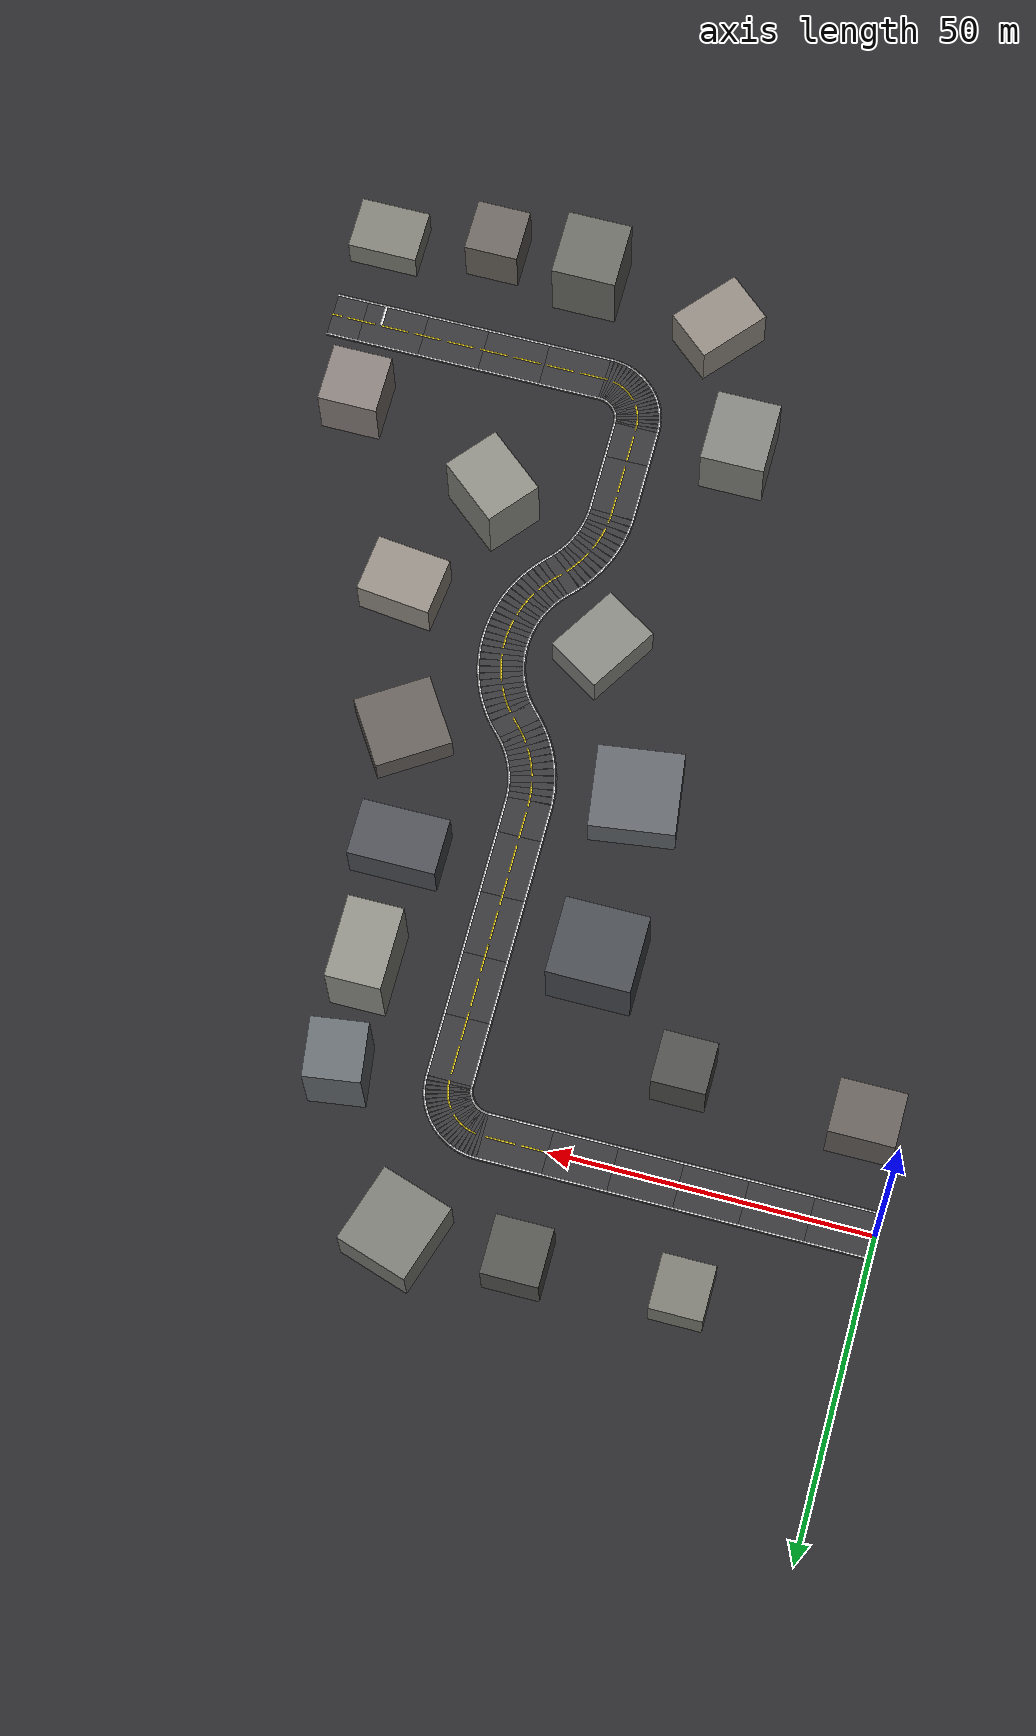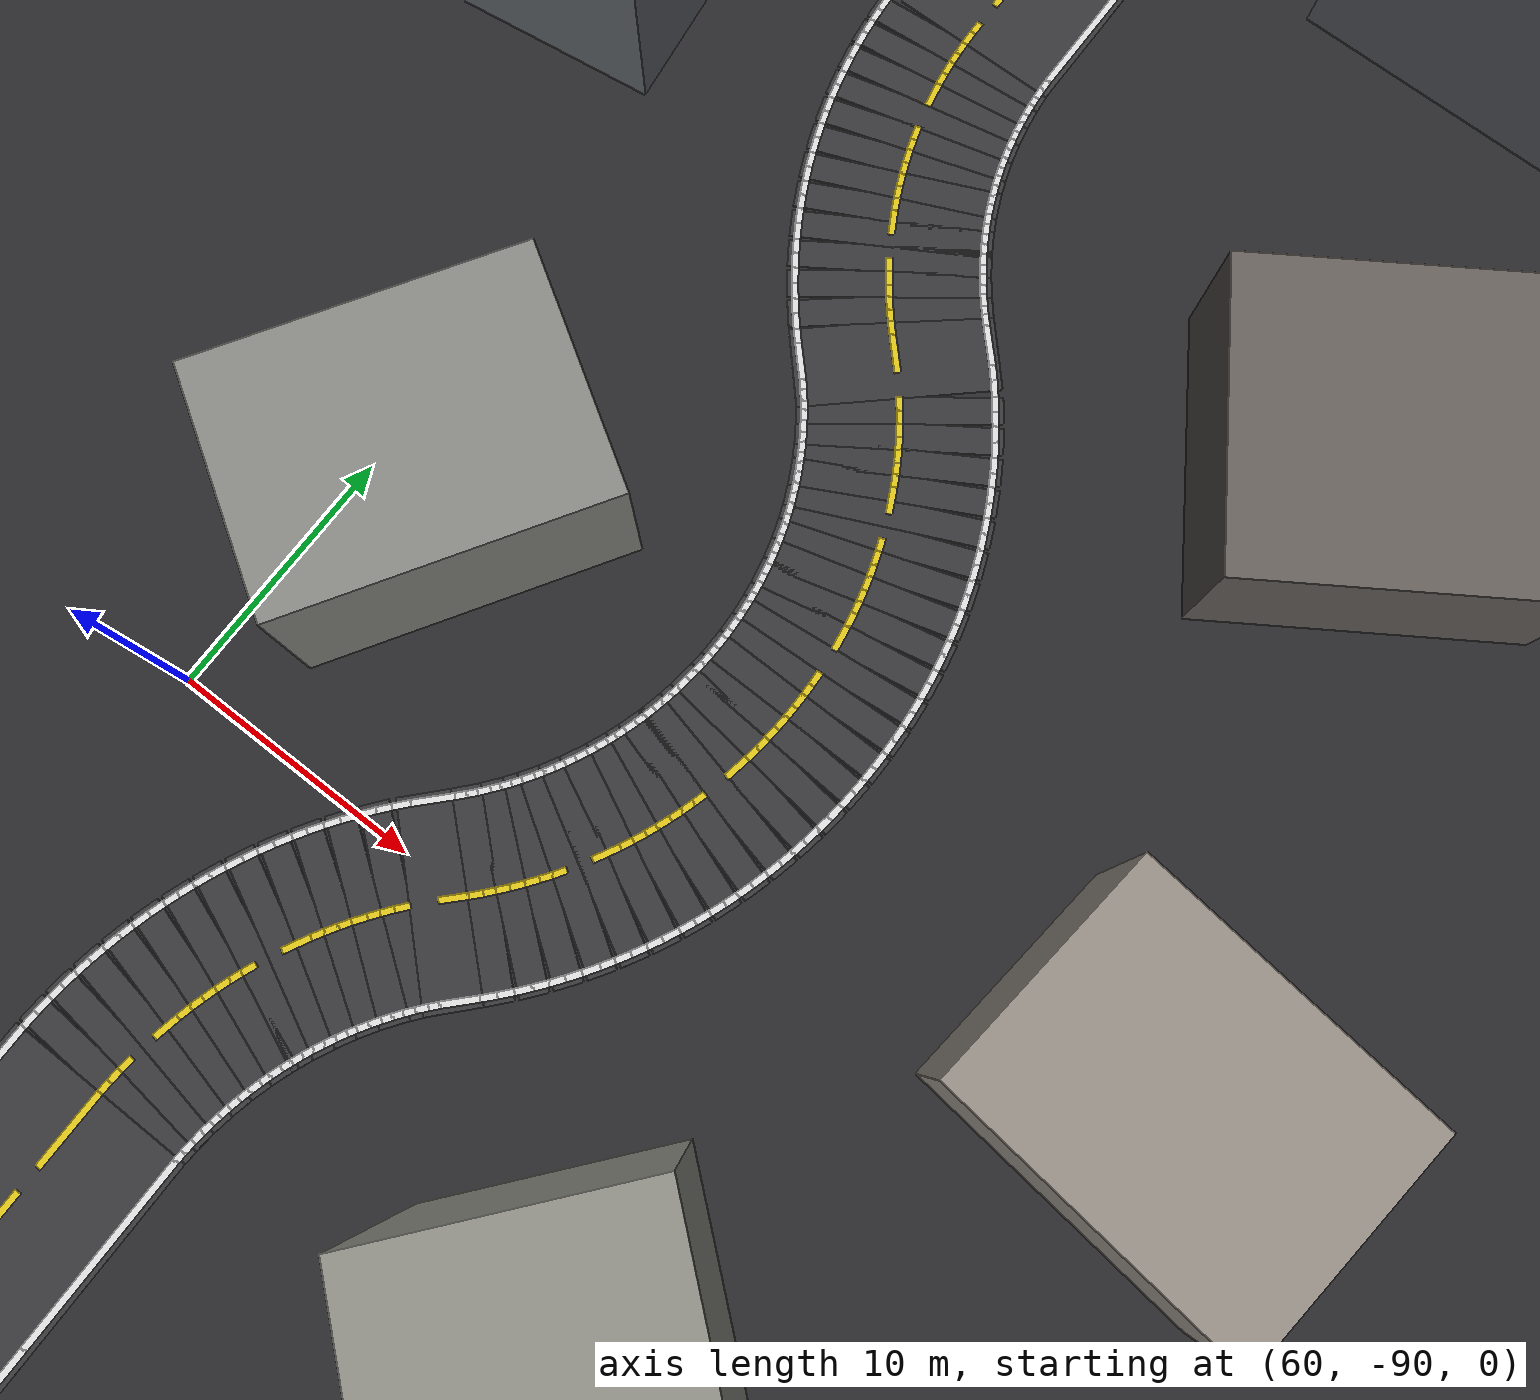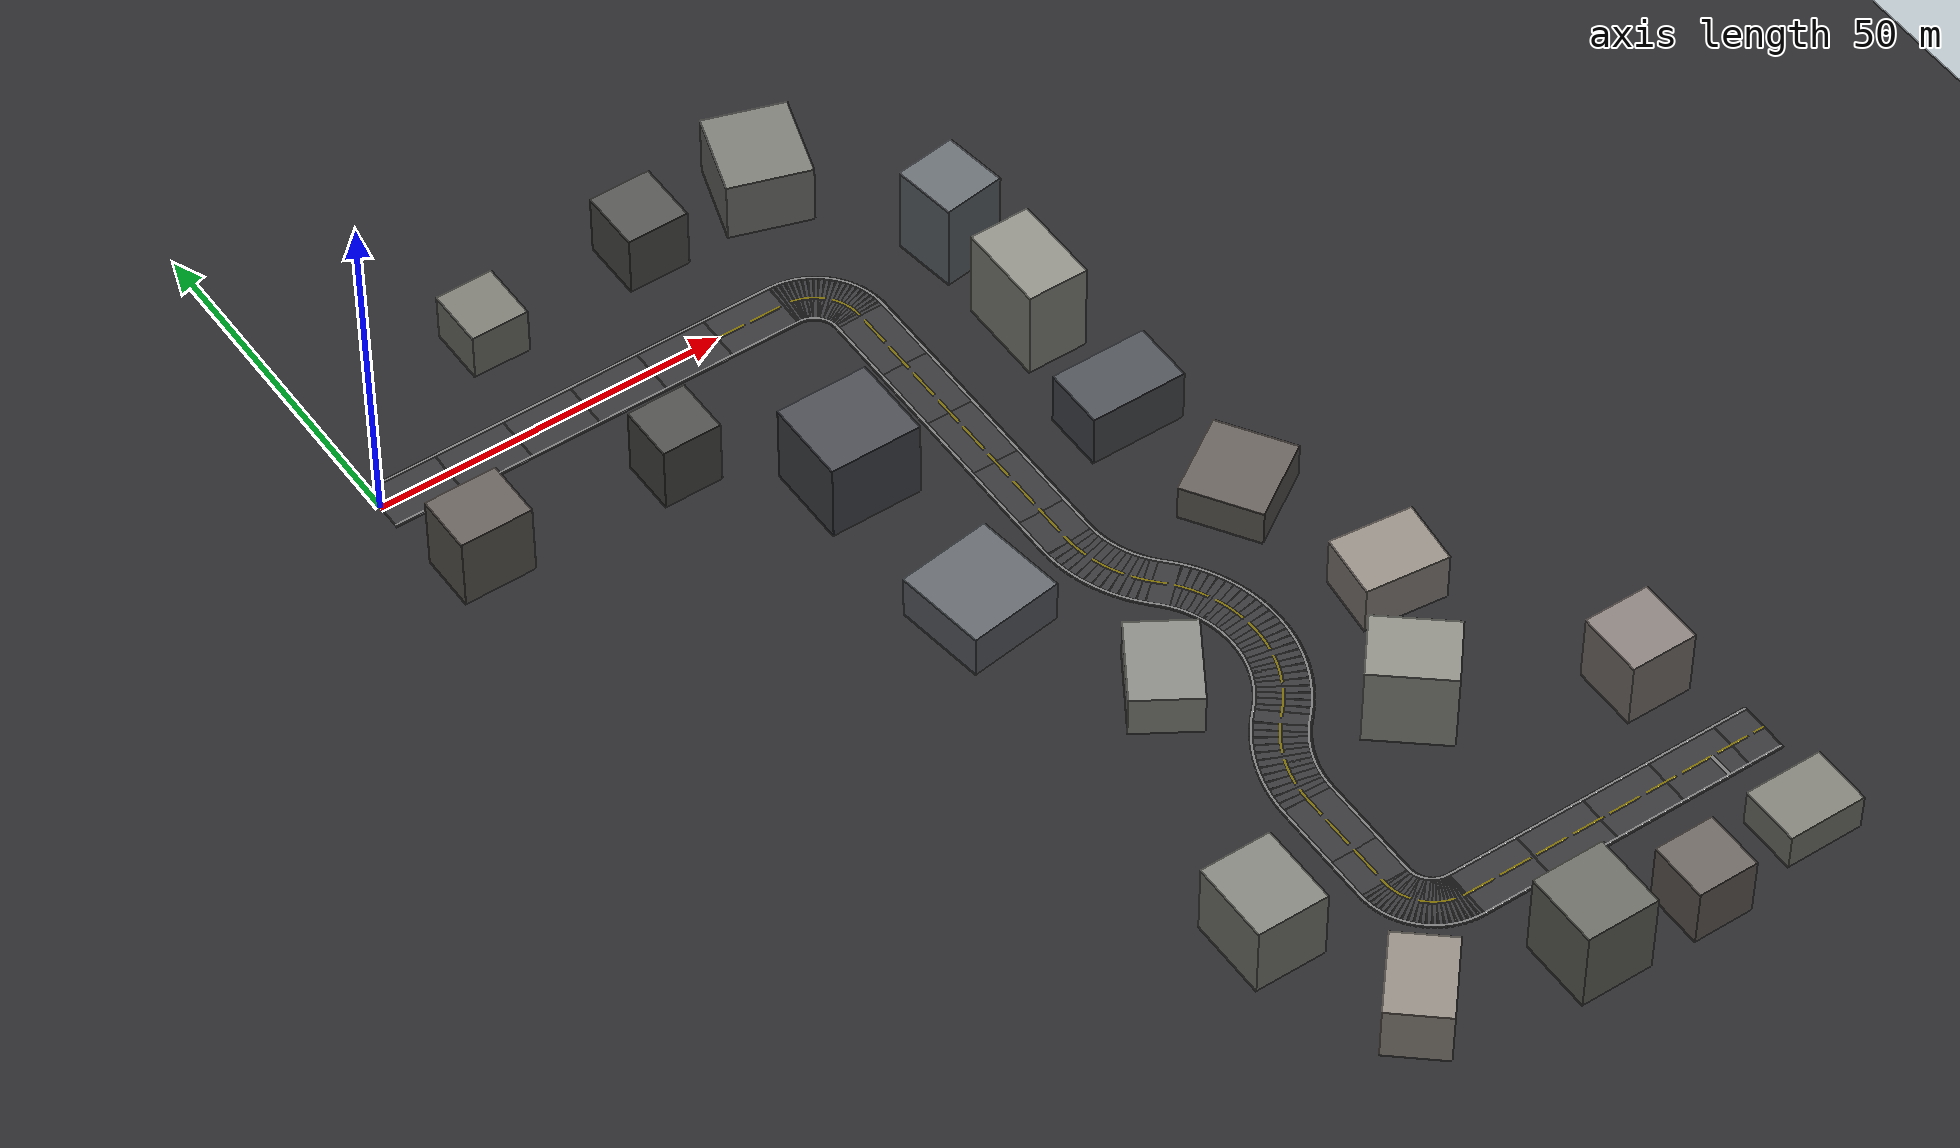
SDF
<sdf version="1.7">
 <world name="urban_tight">
  <physics type="ode"><max_step_size>0.004</max_step_size><real_time_factor>1.0</real_time_factor></physics>
  <plugin filename="libignition-gazebo-physics-system.so" name="ignition::gazebo::systems::Physics"/>
  <plugin filename="libignition-gazebo-user-commands-system.so" name="ignition::gazebo::systems::UserCommands"/>
  <plugin filename="libignition-gazebo-scene-broadcaster-system.so" name="ignition::gazebo::systems::SceneBroadcaster"/>
  <plugin filename="libignition-gazebo-sensors-system.so" name="ignition::gazebo::systems::Sensors">
   <render_engine>ogre2</render_engine>
  </plugin>
  <plugin filename="libignition-gazebo-imu-system.so" name="ignition::gazebo::systems::Imu"/>
  <scene><ambient>0.4 0.4 0.4 1</ambient><background>0.55 0.7 0.9 1</background><shadows>false</shadows></scene>
  <light type="directional" name="sun">
   <cast_shadows>false</cast_shadows>
   <pose>0 0 30 0 0 0</pose>
   <diffuse>0.9 0.9 0.9 1</diffuse>
   <specular>0.2 0.2 0.2 1</specular>
   <direction>-0.3 0.2 -0.9</direction>
  </light>
  <model name="ground">
   <static>true</static>
   <pose>59.5 -62.5 0 0 0 0</pose>
   <link name="l">
    <collision name="c"><geometry><plane><normal>0 0 1</normal><size>179 185</size></plane></geometry></collision>
    <visual name="v">
     <geometry><plane><normal>0 0 1</normal><size>179 185</size></plane></geometry>
     <material><ambient>0.16 0.16 0.17 1</ambient><diffuse>0.16 0.16 0.17 1</diffuse></material>
    </visual>
   </link>
  </model>
  <model name="road">
   <static>true</static>
   <link name="l">
    <visual name="asfalt_0001">
     <pose>5.000 0.000 0.003 0 0 0.0000</pose>
     <geometry><box><size>10.060 7.600 0.006</size></box></geometry>
     <material><ambient>0.21 0.21 0.22 1</ambient><diffuse>0.21 0.21 0.22 1</diffuse></material>
    </visual>
    <visual name="asfalt_0002">
     <pose>15.000 0.000 0.003 0 0 0.0000</pose>
     <geometry><box><size>10.060 7.600 0.006</size></box></geometry>
     <material><ambient>0.21 0.21 0.22 1</ambient><diffuse>0.21 0.21 0.22 1</diffuse></material>
    </visual>
    <visual name="asfalt_0003">
     <pose>25.000 0.000 0.003 0 0 0.0000</pose>
     <geometry><box><size>10.060 7.600 0.006</size></box></geometry>
     <material><ambient>0.21 0.21 0.22 1</ambient><diffuse>0.21 0.21 0.22 1</diffuse></material>
    </visual>
    <visual name="asfalt_0004">
     <pose>35.000 0.000 0.003 0 0 0.0000</pose>
     <geometry><box><size>10.060 7.600 0.006</size></box></geometry>
     <material><ambient>0.21 0.21 0.22 1</ambient><diffuse>0.21 0.21 0.22 1</diffuse></material>
    </visual>
    <visual name="asfalt_0005">
     <pose>45.000 0.000 0.003 0 0 0.0000</pose>
     <geometry><box><size>10.060 7.600 0.006</size></box></geometry>
     <material><ambient>0.21 0.21 0.22 1</ambient><diffuse>0.21 0.21 0.22 1</diffuse></material>
    </visual>
    <visual name="asfalt_0006">
     <pose>55.000 0.000 0.003 0 0 0.0000</pose>
     <geometry><box><size>10.060 7.600 0.006</size></box></geometry>
     <material><ambient>0.21 0.21 0.22 1</ambient><diffuse>0.21 0.21 0.22 1</diffuse></material>
    </visual>
    <visual name="asfalt_0007">
     <pose>60.250 -0.009 0.003 0 0 -0.0357</pose>
     <geometry><box><size>0.560 7.600 0.006</size></box></geometry>
     <material><ambient>0.21 0.21 0.22 1</ambient><diffuse>0.21 0.21 0.22 1</diffuse></material>
    </visual>
    <visual name="asfalt_0008">
     <pose>60.748 -0.045 0.003 0 0 -0.1071</pose>
     <geometry><box><size>0.560 7.600 0.006</size></box></geometry>
     <material><ambient>0.21 0.21 0.22 1</ambient><diffuse>0.21 0.21 0.22 1</diffuse></material>
    </visual>
    <visual name="asfalt_0009">
     <pose>61.242 -0.116 0.003 0 0 -0.1785</pose>
     <geometry><box><size>0.560 7.600 0.006</size></box></geometry>
     <material><ambient>0.21 0.21 0.22 1</ambient><diffuse>0.21 0.21 0.22 1</diffuse></material>
    </visual>
    <visual name="asfalt_0010">
     <pose>61.730 -0.222 0.003 0 0 -0.2499</pose>
     <geometry><box><size>0.560 7.600 0.006</size></box></geometry>
     <material><ambient>0.21 0.21 0.22 1</ambient><diffuse>0.21 0.21 0.22 1</diffuse></material>
    </visual>
    <visual name="asfalt_0011">
     <pose>62.209 -0.362 0.003 0 0 -0.3213</pose>
     <geometry><box><size>0.560 7.600 0.006</size></box></geometry>
     <material><ambient>0.21 0.21 0.22 1</ambient><diffuse>0.21 0.21 0.22 1</diffuse></material>
    </visual>
    <visual name="asfalt_0012">
     <pose>62.677 -0.537 0.003 0 0 -0.3927</pose>
     <geometry><box><size>0.560 7.600 0.006</size></box></geometry>
     <material><ambient>0.21 0.21 0.22 1</ambient><diffuse>0.21 0.21 0.22 1</diffuse></material>
    </visual>
    <visual name="asfalt_0013">
     <pose>63.131 -0.744 0.003 0 0 -0.4641</pose>
     <geometry><box><size>0.560 7.600 0.006</size></box></geometry>
     <material><ambient>0.21 0.21 0.22 1</ambient><diffuse>0.21 0.21 0.22 1</diffuse></material>
    </visual>
    <visual name="asfalt_0014">
     <pose>63.570 -0.984 0.003 0 0 -0.5355</pose>
     <geometry><box><size>0.560 7.600 0.006</size></box></geometry>
     <material><ambient>0.21 0.21 0.22 1</ambient><diffuse>0.21 0.21 0.22 1</diffuse></material>
    </visual>
    <visual name="asfalt_0015">
     <pose>63.990 -1.254 0.003 0 0 -0.6069</pose>
     <geometry><box><size>0.560 7.600 0.006</size></box></geometry>
     <material><ambient>0.21 0.21 0.22 1</ambient><diffuse>0.21 0.21 0.22 1</diffuse></material>
    </visual>
    <visual name="asfalt_0016">
     <pose>64.389 -1.553 0.003 0 0 -0.6783</pose>
     <geometry><box><size>0.560 7.600 0.006</size></box></geometry>
     <material><ambient>0.21 0.21 0.22 1</ambient><diffuse>0.21 0.21 0.22 1</diffuse></material>
    </visual>
    <visual name="asfalt_0017">
     <pose>64.767 -1.880 0.003 0 0 -0.7497</pose>
     <geometry><box><size>0.560 7.600 0.006</size></box></geometry>
     <material><ambient>0.21 0.21 0.22 1</ambient><diffuse>0.21 0.21 0.22 1</diffuse></material>
    </visual>
    <visual name="asfalt_0018">
     <pose>65.120 -2.233 0.003 0 0 -0.8211</pose>
     <geometry><box><size>0.560 7.600 0.006</size></box></geometry>
     <material><ambient>0.21 0.21 0.22 1</ambient><diffuse>0.21 0.21 0.22 1</diffuse></material>
    </visual>
    <visual name="asfalt_0019">
     <pose>65.447 -2.611 0.003 0 0 -0.8925</pose>
     <geometry><box><size>0.560 7.600 0.006</size></box></geometry>
     <material><ambient>0.21 0.21 0.22 1</ambient><diffuse>0.21 0.21 0.22 1</diffuse></material>
    </visual>
    <visual name="asfalt_0020">
     <pose>65.746 -3.010 0.003 0 0 -0.9639</pose>
     <geometry><box><size>0.560 7.600 0.006</size></box></geometry>
     <material><ambient>0.21 0.21 0.22 1</ambient><diffuse>0.21 0.21 0.22 1</diffuse></material>
    </visual>
    <visual name="asfalt_0021">
     <pose>66.016 -3.430 0.003 0 0 -1.0353</pose>
     <geometry><box><size>0.560 7.600 0.006</size></box></geometry>
     <material><ambient>0.21 0.21 0.22 1</ambient><diffuse>0.21 0.21 0.22 1</diffuse></material>
    </visual>
    <visual name="asfalt_0022">
     <pose>66.256 -3.869 0.003 0 0 -1.1067</pose>
     <geometry><box><size>0.560 7.600 0.006</size></box></geometry>
     <material><ambient>0.21 0.21 0.22 1</ambient><diffuse>0.21 0.21 0.22 1</diffuse></material>
    </visual>
    <visual name="asfalt_0023">
     <pose>66.463 -4.323 0.003 0 0 -1.1781</pose>
     <geometry><box><size>0.560 7.600 0.006</size></box></geometry>
     <material><ambient>0.21 0.21 0.22 1</ambient><diffuse>0.21 0.21 0.22 1</diffuse></material>
    </visual>
    <visual name="asfalt_0024">
     <pose>66.638 -4.791 0.003 0 0 -1.2495</pose>
     <geometry><box><size>0.560 7.600 0.006</size></box></geometry>
     <material><ambient>0.21 0.21 0.22 1</ambient><diffuse>0.21 0.21 0.22 1</diffuse></material>
    </visual>
    <visual name="asfalt_0025">
     <pose>66.778 -5.270 0.003 0 0 -1.3209</pose>
     <geometry><box><size>0.560 7.600 0.006</size></box></geometry>
     <material><ambient>0.21 0.21 0.22 1</ambient><diffuse>0.21 0.21 0.22 1</diffuse></material>
    </visual>
    <visual name="asfalt_0026">
     <pose>66.884 -5.758 0.003 0 0 -1.3923</pose>
     <geometry><box><size>0.560 7.600 0.006</size></box></geometry>
     <material><ambient>0.21 0.21 0.22 1</ambient><diffuse>0.21 0.21 0.22 1</diffuse></material>
    </visual>
    <visual name="asfalt_0027">
     <pose>66.955 -6.252 0.003 0 0 -1.4637</pose>
     <geometry><box><size>0.560 7.600 0.006</size></box></geometry>
     <material><ambient>0.21 0.21 0.22 1</ambient><diffuse>0.21 0.21 0.22 1</diffuse></material>
    </visual>
    <visual name="asfalt_0028">
     <pose>66.991 -6.750 0.003 0 0 -1.5351</pose>
     <geometry><box><size>0.560 7.600 0.006</size></box></geometry>
     <material><ambient>0.21 0.21 0.22 1</ambient><diffuse>0.21 0.21 0.22 1</diffuse></material>
    </visual>
    <visual name="asfalt_0029">
     <pose>67.000 -12.000 0.003 0 0 -1.5708</pose>
     <geometry><box><size>10.060 7.600 0.006</size></box></geometry>
     <material><ambient>0.21 0.21 0.22 1</ambient><diffuse>0.21 0.21 0.22 1</diffuse></material>
    </visual>
    <visual name="asfalt_0030">
     <pose>67.000 -22.000 0.003 0 0 -1.5708</pose>
     <geometry><box><size>10.060 7.600 0.006</size></box></geometry>
     <material><ambient>0.21 0.21 0.22 1</ambient><diffuse>0.21 0.21 0.22 1</diffuse></material>
    </visual>
    <visual name="asfalt_0031">
     <pose>67.000 -32.000 0.003 0 0 -1.5708</pose>
     <geometry><box><size>10.060 7.600 0.006</size></box></geometry>
     <material><ambient>0.21 0.21 0.22 1</ambient><diffuse>0.21 0.21 0.22 1</diffuse></material>
    </visual>
    <visual name="asfalt_0032">
     <pose>67.000 -42.000 0.003 0 0 -1.5708</pose>
     <geometry><box><size>10.060 7.600 0.006</size></box></geometry>
     <material><ambient>0.21 0.21 0.22 1</ambient><diffuse>0.21 0.21 0.22 1</diffuse></material>
    </visual>
    <visual name="asfalt_0033">
     <pose>67.014 -50.005 0.003 0 0 -1.5661</pose>
     <geometry><box><size>6.069 7.600 0.006</size></box></geometry>
     <material><ambient>0.21 0.21 0.22 1</ambient><diffuse>0.21 0.21 0.22 1</diffuse></material>
    </visual>
    <visual name="asfalt_0034">
     <pose>67.071 -53.512 0.003 0 0 -1.4866</pose>
     <geometry><box><size>1.070 7.600 0.006</size></box></geometry>
     <material><ambient>0.21 0.21 0.22 1</ambient><diffuse>0.21 0.21 0.22 1</diffuse></material>
    </visual>
    <visual name="asfalt_0035">
     <pose>67.184 -54.515 0.003 0 0 -1.4305</pose>
     <geometry><box><size>1.070 7.600 0.006</size></box></geometry>
     <material><ambient>0.21 0.21 0.22 1</ambient><diffuse>0.21 0.21 0.22 1</diffuse></material>
    </visual>
    <visual name="asfalt_0036">
     <pose>67.353 -55.510 0.003 0 0 -1.3744</pose>
     <geometry><box><size>1.070 7.600 0.006</size></box></geometry>
     <material><ambient>0.21 0.21 0.22 1</ambient><diffuse>0.21 0.21 0.22 1</diffuse></material>
    </visual>
    <visual name="asfalt_0037">
     <pose>67.577 -56.494 0.003 0 0 -1.3183</pose>
     <geometry><box><size>1.070 7.600 0.006</size></box></geometry>
     <material><ambient>0.21 0.21 0.22 1</ambient><diffuse>0.21 0.21 0.22 1</diffuse></material>
    </visual>
    <visual name="asfalt_0038">
     <pose>67.857 -57.464 0.003 0 0 -1.2622</pose>
     <geometry><box><size>1.070 7.600 0.006</size></box></geometry>
     <material><ambient>0.21 0.21 0.22 1</ambient><diffuse>0.21 0.21 0.22 1</diffuse></material>
    </visual>
    <visual name="asfalt_0039">
     <pose>68.190 -58.417 0.003 0 0 -1.2061</pose>
     <geometry><box><size>1.070 7.600 0.006</size></box></geometry>
     <material><ambient>0.21 0.21 0.22 1</ambient><diffuse>0.21 0.21 0.22 1</diffuse></material>
    </visual>
    <visual name="asfalt_0040">
     <pose>68.576 -59.349 0.003 0 0 -1.1500</pose>
     <geometry><box><size>1.070 7.600 0.006</size></box></geometry>
     <material><ambient>0.21 0.21 0.22 1</ambient><diffuse>0.21 0.21 0.22 1</diffuse></material>
    </visual>
    <visual name="asfalt_0041">
     <pose>69.014 -60.258 0.003 0 0 -1.0939</pose>
     <geometry><box><size>1.070 7.600 0.006</size></box></geometry>
     <material><ambient>0.21 0.21 0.22 1</ambient><diffuse>0.21 0.21 0.22 1</diffuse></material>
    </visual>
    <visual name="asfalt_0042">
     <pose>69.502 -61.142 0.003 0 0 -1.0378</pose>
     <geometry><box><size>1.070 7.600 0.006</size></box></geometry>
     <material><ambient>0.21 0.21 0.22 1</ambient><diffuse>0.21 0.21 0.22 1</diffuse></material>
    </visual>
    <visual name="asfalt_0043">
     <pose>70.039 -61.996 0.003 0 0 -0.9817</pose>
     <geometry><box><size>1.070 7.600 0.006</size></box></geometry>
     <material><ambient>0.21 0.21 0.22 1</ambient><diffuse>0.21 0.21 0.22 1</diffuse></material>
    </visual>
    <visual name="asfalt_0044">
     <pose>70.623 -62.819 0.003 0 0 -0.9256</pose>
     <geometry><box><size>1.070 7.600 0.006</size></box></geometry>
     <material><ambient>0.21 0.21 0.22 1</ambient><diffuse>0.21 0.21 0.22 1</diffuse></material>
    </visual>
    <visual name="asfalt_0045">
     <pose>71.253 -63.609 0.003 0 0 -0.8695</pose>
     <geometry><box><size>1.070 7.600 0.006</size></box></geometry>
     <material><ambient>0.21 0.21 0.22 1</ambient><diffuse>0.21 0.21 0.22 1</diffuse></material>
    </visual>
    <visual name="asfalt_0046">
     <pose>72.587 -65.100 0.003 0 0 -0.8314</pose>
     <geometry><box><size>3.053 7.600 0.006</size></box></geometry>
     <material><ambient>0.21 0.21 0.22 1</ambient><diffuse>0.21 0.21 0.22 1</diffuse></material>
    </visual>
    <visual name="asfalt_0047">
     <pose>73.894 -66.601 0.003 0 0 -0.9232</pose>
     <geometry><box><size>1.052 7.600 0.006</size></box></geometry>
     <material><ambient>0.21 0.21 0.22 1</ambient><diffuse>0.21 0.21 0.22 1</diffuse></material>
    </visual>
    <visual name="asfalt_0048">
     <pose>74.470 -67.408 0.003 0 0 -0.9783</pose>
     <geometry><box><size>1.052 7.600 0.006</size></box></geometry>
     <material><ambient>0.21 0.21 0.22 1</ambient><diffuse>0.21 0.21 0.22 1</diffuse></material>
    </visual>
    <visual name="asfalt_0049">
     <pose>75.001 -68.245 0.003 0 0 -1.0334</pose>
     <geometry><box><size>1.052 7.600 0.006</size></box></geometry>
     <material><ambient>0.21 0.21 0.22 1</ambient><diffuse>0.21 0.21 0.22 1</diffuse></material>
    </visual>
    <visual name="asfalt_0050">
     <pose>75.485 -69.111 0.003 0 0 -1.0885</pose>
     <geometry><box><size>1.052 7.600 0.006</size></box></geometry>
     <material><ambient>0.21 0.21 0.22 1</ambient><diffuse>0.21 0.21 0.22 1</diffuse></material>
    </visual>
    <visual name="asfalt_0051">
     <pose>75.921 -70.002 0.003 0 0 -1.1436</pose>
     <geometry><box><size>1.052 7.600 0.006</size></box></geometry>
     <material><ambient>0.21 0.21 0.22 1</ambient><diffuse>0.21 0.21 0.22 1</diffuse></material>
    </visual>
    <visual name="asfalt_0052">
     <pose>76.306 -70.915 0.003 0 0 -1.1988</pose>
     <geometry><box><size>1.052 7.600 0.006</size></box></geometry>
     <material><ambient>0.21 0.21 0.22 1</ambient><diffuse>0.21 0.21 0.22 1</diffuse></material>
    </visual>
    <visual name="asfalt_0053">
     <pose>76.641 -71.849 0.003 0 0 -1.2539</pose>
     <geometry><box><size>1.052 7.600 0.006</size></box></geometry>
     <material><ambient>0.21 0.21 0.22 1</ambient><diffuse>0.21 0.21 0.22 1</diffuse></material>
    </visual>
    <visual name="asfalt_0054">
     <pose>76.924 -72.799 0.003 0 0 -1.3090</pose>
     <geometry><box><size>1.052 7.600 0.006</size></box></geometry>
     <material><ambient>0.21 0.21 0.22 1</ambient><diffuse>0.21 0.21 0.22 1</diffuse></material>
    </visual>
    <visual name="asfalt_0055">
     <pose>77.154 -73.763 0.003 0 0 -1.3641</pose>
     <geometry><box><size>1.052 7.600 0.006</size></box></geometry>
     <material><ambient>0.21 0.21 0.22 1</ambient><diffuse>0.21 0.21 0.22 1</diffuse></material>
    </visual>
    <visual name="asfalt_0056">
     <pose>77.331 -74.739 0.003 0 0 -1.4192</pose>
     <geometry><box><size>1.052 7.600 0.006</size></box></geometry>
     <material><ambient>0.21 0.21 0.22 1</ambient><diffuse>0.21 0.21 0.22 1</diffuse></material>
    </visual>
    <visual name="asfalt_0057">
     <pose>77.454 -75.723 0.003 0 0 -1.4743</pose>
     <geometry><box><size>1.052 7.600 0.006</size></box></geometry>
     <material><ambient>0.21 0.21 0.22 1</ambient><diffuse>0.21 0.21 0.22 1</diffuse></material>
    </visual>
    <visual name="asfalt_0058">
     <pose>77.522 -76.712 0.003 0 0 -1.5295</pose>
     <geometry><box><size>1.052 7.600 0.006</size></box></geometry>
     <material><ambient>0.21 0.21 0.22 1</ambient><diffuse>0.21 0.21 0.22 1</diffuse></material>
    </visual>
    <visual name="asfalt_0059">
     <pose>77.536 -77.704 0.003 0 0 -1.5846</pose>
     <geometry><box><size>1.052 7.600 0.006</size></box></geometry>
     <material><ambient>0.21 0.21 0.22 1</ambient><diffuse>0.21 0.21 0.22 1</diffuse></material>
    </visual>
    <visual name="asfalt_0060">
     <pose>77.495 -78.694 0.003 0 0 -1.6397</pose>
     <geometry><box><size>1.052 7.600 0.006</size></box></geometry>
     <material><ambient>0.21 0.21 0.22 1</ambient><diffuse>0.21 0.21 0.22 1</diffuse></material>
    </visual>
    <visual name="asfalt_0061">
     <pose>77.399 -79.681 0.003 0 0 -1.6948</pose>
     <geometry><box><size>1.052 7.600 0.006</size></box></geometry>
     <material><ambient>0.21 0.21 0.22 1</ambient><diffuse>0.21 0.21 0.22 1</diffuse></material>
    </visual>
    <visual name="asfalt_0062">
     <pose>77.249 -80.662 0.003 0 0 -1.7499</pose>
     <geometry><box><size>1.052 7.600 0.006</size></box></geometry>
     <material><ambient>0.21 0.21 0.22 1</ambient><diffuse>0.21 0.21 0.22 1</diffuse></material>
    </visual>
    <visual name="asfalt_0063">
     <pose>77.046 -81.632 0.003 0 0 -1.8050</pose>
     <geometry><box><size>1.052 7.600 0.006</size></box></geometry>
     <material><ambient>0.21 0.21 0.22 1</ambient><diffuse>0.21 0.21 0.22 1</diffuse></material>
    </visual>
    <visual name="asfalt_0064">
     <pose>76.789 -82.590 0.003 0 0 -1.8602</pose>
     <geometry><box><size>1.052 7.600 0.006</size></box></geometry>
     <material><ambient>0.21 0.21 0.22 1</ambient><diffuse>0.21 0.21 0.22 1</diffuse></material>
    </visual>
    <visual name="asfalt_0065">
     <pose>76.480 -83.532 0.003 0 0 -1.9153</pose>
     <geometry><box><size>1.052 7.600 0.006</size></box></geometry>
     <material><ambient>0.21 0.21 0.22 1</ambient><diffuse>0.21 0.21 0.22 1</diffuse></material>
    </visual>
    <visual name="asfalt_0066">
     <pose>76.120 -84.456 0.003 0 0 -1.9704</pose>
     <geometry><box><size>1.052 7.600 0.006</size></box></geometry>
     <material><ambient>0.21 0.21 0.22 1</ambient><diffuse>0.21 0.21 0.22 1</diffuse></material>
    </visual>
    <visual name="asfalt_0067">
     <pose>75.709 -85.358 0.003 0 0 -2.0255</pose>
     <geometry><box><size>1.052 7.600 0.006</size></box></geometry>
     <material><ambient>0.21 0.21 0.22 1</ambient><diffuse>0.21 0.21 0.22 1</diffuse></material>
    </visual>
    <visual name="asfalt_0068">
     <pose>75.249 -86.237 0.003 0 0 -2.0806</pose>
     <geometry><box><size>1.052 7.600 0.006</size></box></geometry>
     <material><ambient>0.21 0.21 0.22 1</ambient><diffuse>0.21 0.21 0.22 1</diffuse></material>
    </visual>
    <visual name="asfalt_0069">
     <pose>74.742 -87.089 0.003 0 0 -2.1357</pose>
     <geometry><box><size>1.052 7.600 0.006</size></box></geometry>
     <material><ambient>0.21 0.21 0.22 1</ambient><diffuse>0.21 0.21 0.22 1</diffuse></material>
    </visual>
    <visual name="asfalt_0070">
     <pose>74.188 -87.911 0.003 0 0 -2.1908</pose>
     <geometry><box><size>1.052 7.600 0.006</size></box></geometry>
     <material><ambient>0.21 0.21 0.22 1</ambient><diffuse>0.21 0.21 0.22 1</diffuse></material>
    </visual>
    <visual name="asfalt_0071">
     <pose>73.590 -88.702 0.003 0 0 -2.2460</pose>
     <geometry><box><size>1.052 7.600 0.006</size></box></geometry>
     <material><ambient>0.21 0.21 0.22 1</ambient><diffuse>0.21 0.21 0.22 1</diffuse></material>
    </visual>
    <visual name="asfalt_0072">
     <pose>72.949 -89.459 0.003 0 0 -2.3011</pose>
     <geometry><box><size>1.052 7.600 0.006</size></box></geometry>
     <material><ambient>0.21 0.21 0.22 1</ambient><diffuse>0.21 0.21 0.22 1</diffuse></material>
    </visual>
    <visual name="asfalt_0073">
     <pose>71.933 -90.563 0.003 0 0 -2.3211</pose>
     <geometry><box><size>2.070 7.600 0.006</size></box></geometry>
     <material><ambient>0.21 0.21 0.22 1</ambient><diffuse>0.21 0.21 0.22 1</diffuse></material>
    </visual>
    <visual name="asfalt_0074">
     <pose>70.933 -91.693 0.003 0 0 -2.2440</pose>
     <geometry><box><size>1.070 7.600 0.006</size></box></geometry>
     <material><ambient>0.21 0.21 0.22 1</ambient><diffuse>0.21 0.21 0.22 1</diffuse></material>
    </visual>
    <visual name="asfalt_0075">
     <pose>70.326 -92.500 0.003 0 0 -2.1879</pose>
     <geometry><box><size>1.070 7.600 0.006</size></box></geometry>
     <material><ambient>0.21 0.21 0.22 1</ambient><diffuse>0.21 0.21 0.22 1</diffuse></material>
    </visual>
    <visual name="asfalt_0076">
     <pose>69.765 -93.339 0.003 0 0 -2.1318</pose>
     <geometry><box><size>1.070 7.600 0.006</size></box></geometry>
     <material><ambient>0.21 0.21 0.22 1</ambient><diffuse>0.21 0.21 0.22 1</diffuse></material>
    </visual>
    <visual name="asfalt_0077">
     <pose>69.252 -94.208 0.003 0 0 -2.0757</pose>
     <geometry><box><size>1.070 7.600 0.006</size></box></geometry>
     <material><ambient>0.21 0.21 0.22 1</ambient><diffuse>0.21 0.21 0.22 1</diffuse></material>
    </visual>
    <visual name="asfalt_0078">
     <pose>68.789 -95.105 0.003 0 0 -2.0196</pose>
     <geometry><box><size>1.070 7.600 0.006</size></box></geometry>
     <material><ambient>0.21 0.21 0.22 1</ambient><diffuse>0.21 0.21 0.22 1</diffuse></material>
    </visual>
    <visual name="asfalt_0079">
     <pose>68.377 -96.026 0.003 0 0 -1.9635</pose>
     <geometry><box><size>1.070 7.600 0.006</size></box></geometry>
     <material><ambient>0.21 0.21 0.22 1</ambient><diffuse>0.21 0.21 0.22 1</diffuse></material>
    </visual>
    <visual name="asfalt_0080">
     <pose>68.017 -96.969 0.003 0 0 -1.9074</pose>
     <geometry><box><size>1.070 7.600 0.006</size></box></geometry>
     <material><ambient>0.21 0.21 0.22 1</ambient><diffuse>0.21 0.21 0.22 1</diffuse></material>
    </visual>
    <visual name="asfalt_0081">
     <pose>67.710 -97.931 0.003 0 0 -1.8513</pose>
     <geometry><box><size>1.070 7.600 0.006</size></box></geometry>
     <material><ambient>0.21 0.21 0.22 1</ambient><diffuse>0.21 0.21 0.22 1</diffuse></material>
    </visual>
    <visual name="asfalt_0082">
     <pose>67.458 -98.908 0.003 0 0 -1.7952</pose>
     <geometry><box><size>1.070 7.600 0.006</size></box></geometry>
     <material><ambient>0.21 0.21 0.22 1</ambient><diffuse>0.21 0.21 0.22 1</diffuse></material>
    </visual>
    <visual name="asfalt_0083">
     <pose>67.261 -99.898 0.003 0 0 -1.7391</pose>
     <geometry><box><size>1.070 7.600 0.006</size></box></geometry>
     <material><ambient>0.21 0.21 0.22 1</ambient><diffuse>0.21 0.21 0.22 1</diffuse></material>
    </visual>
    <visual name="asfalt_0084">
     <pose>67.120 -100.897 0.003 0 0 -1.6830</pose>
     <geometry><box><size>1.070 7.600 0.006</size></box></geometry>
     <material><ambient>0.21 0.21 0.22 1</ambient><diffuse>0.21 0.21 0.22 1</diffuse></material>
    </visual>
    <visual name="asfalt_0085">
     <pose>67.035 -101.903 0.003 0 0 -1.6269</pose>
     <geometry><box><size>1.070 7.600 0.006</size></box></geometry>
     <material><ambient>0.21 0.21 0.22 1</ambient><diffuse>0.21 0.21 0.22 1</diffuse></material>
    </visual>
    <visual name="asfalt_0086">
     <pose>67.004 -107.159 0.003 0 0 -1.5715</pose>
     <geometry><box><size>9.565 7.600 0.006</size></box></geometry>
     <material><ambient>0.21 0.21 0.22 1</ambient><diffuse>0.21 0.21 0.22 1</diffuse></material>
    </visual>
    <visual name="asfalt_0087">
     <pose>67.000 -114.912 0.003 0 0 -1.5708</pose>
     <geometry><box><size>6.060 7.600 0.006</size></box></geometry>
     <material><ambient>0.21 0.21 0.22 1</ambient><diffuse>0.21 0.21 0.22 1</diffuse></material>
    </visual>
    <visual name="asfalt_0088">
     <pose>67.009 -118.161 0.003 0 0 -1.5351</pose>
     <geometry><box><size>0.560 7.600 0.006</size></box></geometry>
     <material><ambient>0.21 0.21 0.22 1</ambient><diffuse>0.21 0.21 0.22 1</diffuse></material>
    </visual>
    <visual name="asfalt_0089">
     <pose>67.045 -118.659 0.003 0 0 -1.4637</pose>
     <geometry><box><size>0.560 7.600 0.006</size></box></geometry>
     <material><ambient>0.21 0.21 0.22 1</ambient><diffuse>0.21 0.21 0.22 1</diffuse></material>
    </visual>
    <visual name="asfalt_0090">
     <pose>67.116 -119.154 0.003 0 0 -1.3923</pose>
     <geometry><box><size>0.560 7.600 0.006</size></box></geometry>
     <material><ambient>0.21 0.21 0.22 1</ambient><diffuse>0.21 0.21 0.22 1</diffuse></material>
    </visual>
    <visual name="asfalt_0091">
     <pose>67.222 -119.642 0.003 0 0 -1.3209</pose>
     <geometry><box><size>0.560 7.600 0.006</size></box></geometry>
     <material><ambient>0.21 0.21 0.22 1</ambient><diffuse>0.21 0.21 0.22 1</diffuse></material>
    </visual>
    <visual name="asfalt_0092">
     <pose>67.362 -120.121 0.003 0 0 -1.2495</pose>
     <geometry><box><size>0.560 7.600 0.006</size></box></geometry>
     <material><ambient>0.21 0.21 0.22 1</ambient><diffuse>0.21 0.21 0.22 1</diffuse></material>
    </visual>
    <visual name="asfalt_0093">
     <pose>67.537 -120.589 0.003 0 0 -1.1781</pose>
     <geometry><box><size>0.560 7.600 0.006</size></box></geometry>
     <material><ambient>0.21 0.21 0.22 1</ambient><diffuse>0.21 0.21 0.22 1</diffuse></material>
    </visual>
    <visual name="asfalt_0094">
     <pose>67.744 -121.043 0.003 0 0 -1.1067</pose>
     <geometry><box><size>0.560 7.600 0.006</size></box></geometry>
     <material><ambient>0.21 0.21 0.22 1</ambient><diffuse>0.21 0.21 0.22 1</diffuse></material>
    </visual>
    <visual name="asfalt_0095">
     <pose>67.984 -121.481 0.003 0 0 -1.0353</pose>
     <geometry><box><size>0.560 7.600 0.006</size></box></geometry>
     <material><ambient>0.21 0.21 0.22 1</ambient><diffuse>0.21 0.21 0.22 1</diffuse></material>
    </visual>
    <visual name="asfalt_0096">
     <pose>68.254 -121.901 0.003 0 0 -0.9639</pose>
     <geometry><box><size>0.560 7.600 0.006</size></box></geometry>
     <material><ambient>0.21 0.21 0.22 1</ambient><diffuse>0.21 0.21 0.22 1</diffuse></material>
    </visual>
    <visual name="asfalt_0097">
     <pose>68.553 -122.301 0.003 0 0 -0.8925</pose>
     <geometry><box><size>0.560 7.600 0.006</size></box></geometry>
     <material><ambient>0.21 0.21 0.22 1</ambient><diffuse>0.21 0.21 0.22 1</diffuse></material>
    </visual>
    <visual name="asfalt_0098">
     <pose>68.880 -122.679 0.003 0 0 -0.8211</pose>
     <geometry><box><size>0.560 7.600 0.006</size></box></geometry>
     <material><ambient>0.21 0.21 0.22 1</ambient><diffuse>0.21 0.21 0.22 1</diffuse></material>
    </visual>
    <visual name="asfalt_0099">
     <pose>69.233 -123.032 0.003 0 0 -0.7497</pose>
     <geometry><box><size>0.560 7.600 0.006</size></box></geometry>
     <material><ambient>0.21 0.21 0.22 1</ambient><diffuse>0.21 0.21 0.22 1</diffuse></material>
    </visual>
    <visual name="asfalt_0100">
     <pose>69.611 -123.359 0.003 0 0 -0.6783</pose>
     <geometry><box><size>0.560 7.600 0.006</size></box></geometry>
     <material><ambient>0.21 0.21 0.22 1</ambient><diffuse>0.21 0.21 0.22 1</diffuse></material>
    </visual>
    <visual name="asfalt_0101">
     <pose>70.010 -123.658 0.003 0 0 -0.6069</pose>
     <geometry><box><size>0.560 7.600 0.006</size></box></geometry>
     <material><ambient>0.21 0.21 0.22 1</ambient><diffuse>0.21 0.21 0.22 1</diffuse></material>
    </visual>
    <visual name="asfalt_0102">
     <pose>70.430 -123.928 0.003 0 0 -0.5355</pose>
     <geometry><box><size>0.560 7.600 0.006</size></box></geometry>
     <material><ambient>0.21 0.21 0.22 1</ambient><diffuse>0.21 0.21 0.22 1</diffuse></material>
    </visual>
    <visual name="asfalt_0103">
     <pose>70.869 -124.167 0.003 0 0 -0.4641</pose>
     <geometry><box><size>0.560 7.600 0.006</size></box></geometry>
     <material><ambient>0.21 0.21 0.22 1</ambient><diffuse>0.21 0.21 0.22 1</diffuse></material>
    </visual>
    <visual name="asfalt_0104">
     <pose>71.323 -124.375 0.003 0 0 -0.3927</pose>
     <geometry><box><size>0.560 7.600 0.006</size></box></geometry>
     <material><ambient>0.21 0.21 0.22 1</ambient><diffuse>0.21 0.21 0.22 1</diffuse></material>
    </visual>
    <visual name="asfalt_0105">
     <pose>71.791 -124.549 0.003 0 0 -0.3213</pose>
     <geometry><box><size>0.560 7.600 0.006</size></box></geometry>
     <material><ambient>0.21 0.21 0.22 1</ambient><diffuse>0.21 0.21 0.22 1</diffuse></material>
    </visual>
    <visual name="asfalt_0106">
     <pose>72.270 -124.690 0.003 0 0 -0.2499</pose>
     <geometry><box><size>0.560 7.600 0.006</size></box></geometry>
     <material><ambient>0.21 0.21 0.22 1</ambient><diffuse>0.21 0.21 0.22 1</diffuse></material>
    </visual>
    <visual name="asfalt_0107">
     <pose>72.758 -124.796 0.003 0 0 -0.1785</pose>
     <geometry><box><size>0.560 7.600 0.006</size></box></geometry>
     <material><ambient>0.21 0.21 0.22 1</ambient><diffuse>0.21 0.21 0.22 1</diffuse></material>
    </visual>
    <visual name="asfalt_0108">
     <pose>73.252 -124.867 0.003 0 0 -0.1071</pose>
     <geometry><box><size>0.560 7.600 0.006</size></box></geometry>
     <material><ambient>0.21 0.21 0.22 1</ambient><diffuse>0.21 0.21 0.22 1</diffuse></material>
    </visual>
    <visual name="asfalt_0109">
     <pose>73.750 -124.903 0.003 0 0 -0.0357</pose>
     <geometry><box><size>0.560 7.600 0.006</size></box></geometry>
     <material><ambient>0.21 0.21 0.22 1</ambient><diffuse>0.21 0.21 0.22 1</diffuse></material>
    </visual>
    <visual name="asfalt_0110">
     <pose>79.000 -124.912 0.003 0 0 0.0000</pose>
     <geometry><box><size>10.060 7.600 0.006</size></box></geometry>
     <material><ambient>0.21 0.21 0.22 1</ambient><diffuse>0.21 0.21 0.22 1</diffuse></material>
    </visual>
    <visual name="asfalt_0111">
     <pose>89.000 -124.912 0.003 0 0 0.0000</pose>
     <geometry><box><size>10.060 7.600 0.006</size></box></geometry>
     <material><ambient>0.21 0.21 0.22 1</ambient><diffuse>0.21 0.21 0.22 1</diffuse></material>
    </visual>
    <visual name="asfalt_0112">
     <pose>99.000 -124.912 0.003 0 0 0.0000</pose>
     <geometry><box><size>10.060 7.600 0.006</size></box></geometry>
     <material><ambient>0.21 0.21 0.22 1</ambient><diffuse>0.21 0.21 0.22 1</diffuse></material>
    </visual>
    <visual name="asfalt_0113">
     <pose>109.000 -124.912 0.003 0 0 0.0000</pose>
     <geometry><box><size>10.060 7.600 0.006</size></box></geometry>
     <material><ambient>0.21 0.21 0.22 1</ambient><diffuse>0.21 0.21 0.22 1</diffuse></material>
    </visual>
    <visual name="asfalt_0114">
     <pose>116.500 -124.912 0.003 0 0 0.0000</pose>
     <geometry><box><size>5.060 7.600 0.006</size></box></geometry>
     <material><ambient>0.21 0.21 0.22 1</ambient><diffuse>0.21 0.21 0.22 1</diffuse></material>
    </visual>
    <visual name="edge_l_0001">
     <pose>4.000 3.500 0.010 0 0 0.0000</pose>
     <geometry><box><size>8.060 0.250 0.010</size></box></geometry>
     <material><ambient>0.85 0.85 0.85 1</ambient><diffuse>0.85 0.85 0.85 1</diffuse></material>
    </visual>
    <visual name="edge_l_0002">
     <pose>12.000 3.500 0.010 0 0 0.0000</pose>
     <geometry><box><size>8.060 0.250 0.010</size></box></geometry>
     <material><ambient>0.85 0.85 0.85 1</ambient><diffuse>0.85 0.85 0.85 1</diffuse></material>
    </visual>
    <visual name="edge_l_0003">
     <pose>20.000 3.500 0.010 0 0 0.0000</pose>
     <geometry><box><size>8.060 0.250 0.010</size></box></geometry>
     <material><ambient>0.85 0.85 0.85 1</ambient><diffuse>0.85 0.85 0.85 1</diffuse></material>
    </visual>
    <visual name="edge_l_0004">
     <pose>28.000 3.500 0.010 0 0 0.0000</pose>
     <geometry><box><size>8.060 0.250 0.010</size></box></geometry>
     <material><ambient>0.85 0.85 0.85 1</ambient><diffuse>0.85 0.85 0.85 1</diffuse></material>
    </visual>
    <visual name="edge_l_0005">
     <pose>36.000 3.500 0.010 0 0 0.0000</pose>
     <geometry><box><size>8.060 0.250 0.010</size></box></geometry>
     <material><ambient>0.85 0.85 0.85 1</ambient><diffuse>0.85 0.85 0.85 1</diffuse></material>
    </visual>
    <visual name="edge_l_0006">
     <pose>44.000 3.500 0.010 0 0 0.0000</pose>
     <geometry><box><size>8.060 0.250 0.010</size></box></geometry>
     <material><ambient>0.85 0.85 0.85 1</ambient><diffuse>0.85 0.85 0.85 1</diffuse></material>
    </visual>
    <visual name="edge_l_0007">
     <pose>52.000 3.500 0.010 0 0 0.0000</pose>
     <geometry><box><size>8.060 0.250 0.010</size></box></geometry>
     <material><ambient>0.85 0.85 0.85 1</ambient><diffuse>0.85 0.85 0.85 1</diffuse></material>
    </visual>
    <visual name="edge_l_0008">
     <pose>58.000 3.500 0.010 0 0 0.0000</pose>
     <geometry><box><size>4.060 0.250 0.010</size></box></geometry>
     <material><ambient>0.85 0.85 0.85 1</ambient><diffuse>0.85 0.85 0.85 1</diffuse></material>
    </visual>
    <visual name="edge_l_0009">
     <pose>60.375 3.487 0.010 0 0 -0.0357</pose>
     <geometry><box><size>0.810 0.250 0.010</size></box></geometry>
     <material><ambient>0.85 0.85 0.85 1</ambient><diffuse>0.85 0.85 0.85 1</diffuse></material>
    </visual>
    <visual name="edge_l_0010">
     <pose>61.122 3.433 0.010 0 0 -0.1071</pose>
     <geometry><box><size>0.810 0.250 0.010</size></box></geometry>
     <material><ambient>0.85 0.85 0.85 1</ambient><diffuse>0.85 0.85 0.85 1</diffuse></material>
    </visual>
    <visual name="edge_l_0011">
     <pose>61.863 3.327 0.010 0 0 -0.1785</pose>
     <geometry><box><size>0.810 0.250 0.010</size></box></geometry>
     <material><ambient>0.85 0.85 0.85 1</ambient><diffuse>0.85 0.85 0.85 1</diffuse></material>
    </visual>
    <visual name="edge_l_0012">
     <pose>62.595 3.167 0.010 0 0 -0.2499</pose>
     <geometry><box><size>0.810 0.250 0.010</size></box></geometry>
     <material><ambient>0.85 0.85 0.85 1</ambient><diffuse>0.85 0.85 0.85 1</diffuse></material>
    </visual>
    <visual name="edge_l_0013">
     <pose>63.314 2.956 0.010 0 0 -0.3213</pose>
     <geometry><box><size>0.810 0.250 0.010</size></box></geometry>
     <material><ambient>0.85 0.85 0.85 1</ambient><diffuse>0.85 0.85 0.85 1</diffuse></material>
    </visual>
    <visual name="edge_l_0014">
     <pose>64.016 2.695 0.010 0 0 -0.3927</pose>
     <geometry><box><size>0.810 0.250 0.010</size></box></geometry>
     <material><ambient>0.85 0.85 0.85 1</ambient><diffuse>0.85 0.85 0.85 1</diffuse></material>
    </visual>
    <visual name="edge_l_0015">
     <pose>64.697 2.383 0.010 0 0 -0.4641</pose>
     <geometry><box><size>0.810 0.250 0.010</size></box></geometry>
     <material><ambient>0.85 0.85 0.85 1</ambient><diffuse>0.85 0.85 0.85 1</diffuse></material>
    </visual>
    <visual name="edge_l_0016">
     <pose>65.354 2.024 0.010 0 0 -0.5355</pose>
     <geometry><box><size>0.810 0.250 0.010</size></box></geometry>
     <material><ambient>0.85 0.85 0.85 1</ambient><diffuse>0.85 0.85 0.85 1</diffuse></material>
    </visual>
    <visual name="edge_l_0017">
     <pose>65.985 1.619 0.010 0 0 -0.6069</pose>
     <geometry><box><size>0.810 0.250 0.010</size></box></geometry>
     <material><ambient>0.85 0.85 0.85 1</ambient><diffuse>0.85 0.85 0.85 1</diffuse></material>
    </visual>
    <visual name="edge_l_0018">
     <pose>66.584 1.171 0.010 0 0 -0.6783</pose>
     <geometry><box><size>0.810 0.250 0.010</size></box></geometry>
     <material><ambient>0.85 0.85 0.85 1</ambient><diffuse>0.85 0.85 0.85 1</diffuse></material>
    </visual>
    <visual name="edge_l_0019">
     <pose>67.150 0.680 0.010 0 0 -0.7497</pose>
     <geometry><box><size>0.810 0.250 0.010</size></box></geometry>
     <material><ambient>0.85 0.85 0.85 1</ambient><diffuse>0.85 0.85 0.85 1</diffuse></material>
    </visual>
    <visual name="edge_l_0020">
     <pose>67.680 0.150 0.010 0 0 -0.8211</pose>
     <geometry><box><size>0.810 0.250 0.010</size></box></geometry>
     <material><ambient>0.85 0.85 0.85 1</ambient><diffuse>0.85 0.85 0.85 1</diffuse></material>
    </visual>
    <visual name="edge_l_0021">
     <pose>68.171 -0.416 0.010 0 0 -0.8925</pose>
     <geometry><box><size>0.810 0.250 0.010</size></box></geometry>
     <material><ambient>0.85 0.85 0.85 1</ambient><diffuse>0.85 0.85 0.85 1</diffuse></material>
    </visual>
    <visual name="edge_l_0022">
     <pose>68.619 -1.015 0.010 0 0 -0.9639</pose>
     <geometry><box><size>0.810 0.250 0.010</size></box></geometry>
     <material><ambient>0.85 0.85 0.85 1</ambient><diffuse>0.85 0.85 0.85 1</diffuse></material>
    </visual>
    <visual name="edge_l_0023">
     <pose>69.024 -1.646 0.010 0 0 -1.0353</pose>
     <geometry><box><size>0.810 0.250 0.010</size></box></geometry>
     <material><ambient>0.85 0.85 0.85 1</ambient><diffuse>0.85 0.85 0.85 1</diffuse></material>
    </visual>
    <visual name="edge_l_0024">
     <pose>69.383 -2.303 0.010 0 0 -1.1067</pose>
     <geometry><box><size>0.810 0.250 0.010</size></box></geometry>
     <material><ambient>0.85 0.85 0.85 1</ambient><diffuse>0.85 0.85 0.85 1</diffuse></material>
    </visual>
    <visual name="edge_l_0025">
     <pose>69.695 -2.984 0.010 0 0 -1.1781</pose>
     <geometry><box><size>0.810 0.250 0.010</size></box></geometry>
     <material><ambient>0.85 0.85 0.85 1</ambient><diffuse>0.85 0.85 0.85 1</diffuse></material>
    </visual>
    <visual name="edge_l_0026">
     <pose>69.956 -3.686 0.010 0 0 -1.2495</pose>
     <geometry><box><size>0.810 0.250 0.010</size></box></geometry>
     <material><ambient>0.85 0.85 0.85 1</ambient><diffuse>0.85 0.85 0.85 1</diffuse></material>
    </visual>
    <visual name="edge_l_0027">
     <pose>70.167 -4.405 0.010 0 0 -1.3209</pose>
     <geometry><box><size>0.810 0.250 0.010</size></box></geometry>
     <material><ambient>0.85 0.85 0.85 1</ambient><diffuse>0.85 0.85 0.85 1</diffuse></material>
    </visual>
    <visual name="edge_l_0028">
     <pose>70.327 -5.137 0.010 0 0 -1.3923</pose>
     <geometry><box><size>0.810 0.250 0.010</size></box></geometry>
     <material><ambient>0.85 0.85 0.85 1</ambient><diffuse>0.85 0.85 0.85 1</diffuse></material>
    </visual>
    <visual name="edge_l_0029">
     <pose>70.433 -5.878 0.010 0 0 -1.4637</pose>
     <geometry><box><size>0.810 0.250 0.010</size></box></geometry>
     <material><ambient>0.85 0.85 0.85 1</ambient><diffuse>0.85 0.85 0.85 1</diffuse></material>
    </visual>
    <visual name="edge_l_0030">
     <pose>70.487 -6.625 0.010 0 0 -1.5351</pose>
     <geometry><box><size>0.810 0.250 0.010</size></box></geometry>
     <material><ambient>0.85 0.85 0.85 1</ambient><diffuse>0.85 0.85 0.85 1</diffuse></material>
    </visual>
    <visual name="edge_l_0031">
     <pose>70.500 -11.000 0.010 0 0 -1.5708</pose>
     <geometry><box><size>8.060 0.250 0.010</size></box></geometry>
     <material><ambient>0.85 0.85 0.85 1</ambient><diffuse>0.85 0.85 0.85 1</diffuse></material>
    </visual>
    <visual name="edge_l_0032">
     <pose>70.500 -19.000 0.010 0 0 -1.5708</pose>
     <geometry><box><size>8.060 0.250 0.010</size></box></geometry>
     <material><ambient>0.85 0.85 0.85 1</ambient><diffuse>0.85 0.85 0.85 1</diffuse></material>
    </visual>
    <visual name="edge_l_0033">
     <pose>70.500 -27.000 0.010 0 0 -1.5708</pose>
     <geometry><box><size>8.060 0.250 0.010</size></box></geometry>
     <material><ambient>0.85 0.85 0.85 1</ambient><diffuse>0.85 0.85 0.85 1</diffuse></material>
    </visual>
    <visual name="edge_l_0034">
     <pose>70.500 -35.000 0.010 0 0 -1.5708</pose>
     <geometry><box><size>8.060 0.250 0.010</size></box></geometry>
     <material><ambient>0.85 0.85 0.85 1</ambient><diffuse>0.85 0.85 0.85 1</diffuse></material>
    </visual>
    <visual name="edge_l_0035">
     <pose>70.500 -43.000 0.010 0 0 -1.5708</pose>
     <geometry><box><size>8.060 0.250 0.010</size></box></geometry>
     <material><ambient>0.85 0.85 0.85 1</ambient><diffuse>0.85 0.85 0.85 1</diffuse></material>
    </visual>
    <visual name="edge_l_0036">
     <pose>70.503 -49.703 0.010 0 0 -1.5697</pose>
     <geometry><box><size>5.467 0.250 0.010</size></box></geometry>
     <material><ambient>0.85 0.85 0.85 1</ambient><diffuse>0.85 0.85 0.85 1</diffuse></material>
    </visual>
    <visual name="edge_l_0037">
     <pose>70.514 -52.610 0.010 0 0 -1.5287</pose>
     <geometry><box><size>0.467 0.250 0.010</size></box></geometry>
     <material><ambient>0.85 0.85 0.85 1</ambient><diffuse>0.85 0.85 0.85 1</diffuse></material>
    </visual>
    <visual name="edge_l_0038">
     <pose>70.537 -53.016 0.010 0 0 -1.5007</pose>
     <geometry><box><size>0.467 0.250 0.010</size></box></geometry>
     <material><ambient>0.85 0.85 0.85 1</ambient><diffuse>0.85 0.85 0.85 1</diffuse></material>
    </visual>
    <visual name="edge_l_0039">
     <pose>70.571 -53.421 0.010 0 0 -1.4726</pose>
     <geometry><box><size>0.467 0.250 0.010</size></box></geometry>
     <material><ambient>0.85 0.85 0.85 1</ambient><diffuse>0.85 0.85 0.85 1</diffuse></material>
    </visual>
    <visual name="edge_l_0040">
     <pose>70.617 -53.825 0.010 0 0 -1.4446</pose>
     <geometry><box><size>0.467 0.250 0.010</size></box></geometry>
     <material><ambient>0.85 0.85 0.85 1</ambient><diffuse>0.85 0.85 0.85 1</diffuse></material>
    </visual>
    <visual name="edge_l_0041">
     <pose>70.674 -54.228 0.010 0 0 -1.4165</pose>
     <geometry><box><size>0.467 0.250 0.010</size></box></geometry>
     <material><ambient>0.85 0.85 0.85 1</ambient><diffuse>0.85 0.85 0.85 1</diffuse></material>
    </visual>
    <visual name="edge_l_0042">
     <pose>70.742 -54.629 0.010 0 0 -1.3885</pose>
     <geometry><box><size>0.467 0.250 0.010</size></box></geometry>
     <material><ambient>0.85 0.85 0.85 1</ambient><diffuse>0.85 0.85 0.85 1</diffuse></material>
    </visual>
    <visual name="edge_l_0043">
     <pose>70.821 -55.028 0.010 0 0 -1.3604</pose>
     <geometry><box><size>0.467 0.250 0.010</size></box></geometry>
     <material><ambient>0.85 0.85 0.85 1</ambient><diffuse>0.85 0.85 0.85 1</diffuse></material>
    </visual>
    <visual name="edge_l_0044">
     <pose>70.912 -55.424 0.010 0 0 -1.3324</pose>
     <geometry><box><size>0.467 0.250 0.010</size></box></geometry>
     <material><ambient>0.85 0.85 0.85 1</ambient><diffuse>0.85 0.85 0.85 1</diffuse></material>
    </visual>
    <visual name="edge_l_0045">
     <pose>71.013 -55.818 0.010 0 0 -1.3043</pose>
     <geometry><box><size>0.467 0.250 0.010</size></box></geometry>
     <material><ambient>0.85 0.85 0.85 1</ambient><diffuse>0.85 0.85 0.85 1</diffuse></material>
    </visual>
    <visual name="edge_l_0046">
     <pose>71.126 -56.209 0.010 0 0 -1.2763</pose>
     <geometry><box><size>0.467 0.250 0.010</size></box></geometry>
     <material><ambient>0.85 0.85 0.85 1</ambient><diffuse>0.85 0.85 0.85 1</diffuse></material>
    </visual>
    <visual name="edge_l_0047">
     <pose>71.249 -56.596 0.010 0 0 -1.2482</pose>
     <geometry><box><size>0.467 0.250 0.010</size></box></geometry>
     <material><ambient>0.85 0.85 0.85 1</ambient><diffuse>0.85 0.85 0.85 1</diffuse></material>
    </visual>
    <visual name="edge_l_0048">
     <pose>71.384 -56.980 0.010 0 0 -1.2202</pose>
     <geometry><box><size>0.467 0.250 0.010</size></box></geometry>
     <material><ambient>0.85 0.85 0.85 1</ambient><diffuse>0.85 0.85 0.85 1</diffuse></material>
    </visual>
    <visual name="edge_l_0049">
     <pose>71.529 -57.360 0.010 0 0 -1.1921</pose>
     <geometry><box><size>0.467 0.250 0.010</size></box></geometry>
     <material><ambient>0.85 0.85 0.85 1</ambient><diffuse>0.85 0.85 0.85 1</diffuse></material>
    </visual>
    <visual name="edge_l_0050">
     <pose>71.684 -57.736 0.010 0 0 -1.1641</pose>
     <geometry><box><size>0.467 0.250 0.010</size></box></geometry>
     <material><ambient>0.85 0.85 0.85 1</ambient><diffuse>0.85 0.85 0.85 1</diffuse></material>
    </visual>
    <visual name="edge_l_0051">
     <pose>71.850 -58.107 0.010 0 0 -1.1360</pose>
     <geometry><box><size>0.467 0.250 0.010</size></box></geometry>
     <material><ambient>0.85 0.85 0.85 1</ambient><diffuse>0.85 0.85 0.85 1</diffuse></material>
    </visual>
    <visual name="edge_l_0052">
     <pose>72.027 -58.473 0.010 0 0 -1.1080</pose>
     <geometry><box><size>0.467 0.250 0.010</size></box></geometry>
     <material><ambient>0.85 0.85 0.85 1</ambient><diffuse>0.85 0.85 0.85 1</diffuse></material>
    </visual>
    <visual name="edge_l_0053">
     <pose>72.213 -58.835 0.010 0 0 -1.0799</pose>
     <geometry><box><size>0.467 0.250 0.010</size></box></geometry>
     <material><ambient>0.85 0.85 0.85 1</ambient><diffuse>0.85 0.85 0.85 1</diffuse></material>
    </visual>
    <visual name="edge_l_0054">
     <pose>72.410 -59.191 0.010 0 0 -1.0519</pose>
     <geometry><box><size>0.467 0.250 0.010</size></box></geometry>
     <material><ambient>0.85 0.85 0.85 1</ambient><diffuse>0.85 0.85 0.85 1</diffuse></material>
    </visual>
    <visual name="edge_l_0055">
     <pose>72.617 -59.541 0.010 0 0 -1.0238</pose>
     <geometry><box><size>0.467 0.250 0.010</size></box></geometry>
     <material><ambient>0.85 0.85 0.85 1</ambient><diffuse>0.85 0.85 0.85 1</diffuse></material>
    </visual>
    <visual name="edge_l_0056">
     <pose>72.833 -59.885 0.010 0 0 -0.9958</pose>
     <geometry><box><size>0.467 0.250 0.010</size></box></geometry>
     <material><ambient>0.85 0.85 0.85 1</ambient><diffuse>0.85 0.85 0.85 1</diffuse></material>
    </visual>
    <visual name="edge_l_0057">
     <pose>73.059 -60.223 0.010 0 0 -0.9677</pose>
     <geometry><box><size>0.467 0.250 0.010</size></box></geometry>
     <material><ambient>0.85 0.85 0.85 1</ambient><diffuse>0.85 0.85 0.85 1</diffuse></material>
    </visual>
    <visual name="edge_l_0058">
     <pose>73.294 -60.555 0.010 0 0 -0.9397</pose>
     <geometry><box><size>0.467 0.250 0.010</size></box></geometry>
     <material><ambient>0.85 0.85 0.85 1</ambient><diffuse>0.85 0.85 0.85 1</diffuse></material>
    </visual>
    <visual name="edge_l_0059">
     <pose>73.539 -60.880 0.010 0 0 -0.9116</pose>
     <geometry><box><size>0.467 0.250 0.010</size></box></geometry>
     <material><ambient>0.85 0.85 0.85 1</ambient><diffuse>0.85 0.85 0.85 1</diffuse></material>
    </visual>
    <visual name="edge_l_0060">
     <pose>73.792 -61.198 0.010 0 0 -0.8836</pose>
     <geometry><box><size>0.467 0.250 0.010</size></box></geometry>
     <material><ambient>0.85 0.85 0.85 1</ambient><diffuse>0.85 0.85 0.85 1</diffuse></material>
    </visual>
    <visual name="edge_l_0061">
     <pose>74.055 -61.509 0.010 0 0 -0.8555</pose>
     <geometry><box><size>0.467 0.250 0.010</size></box></geometry>
     <material><ambient>0.85 0.85 0.85 1</ambient><diffuse>0.85 0.85 0.85 1</diffuse></material>
    </visual>
    <visual name="edge_l_0062">
     <pose>74.326 -61.812 0.010 0 0 -0.8275</pose>
     <geometry><box><size>0.467 0.250 0.010</size></box></geometry>
     <material><ambient>0.85 0.85 0.85 1</ambient><diffuse>0.85 0.85 0.85 1</diffuse></material>
    </visual>
    <visual name="edge_l_0063">
     <pose>75.012 -62.538 0.010 0 0 -0.8095</pose>
     <geometry><box><size>1.652 0.250 0.010</size></box></geometry>
     <material><ambient>0.85 0.85 0.85 1</ambient><diffuse>0.85 0.85 0.85 1</diffuse></material>
    </visual>
    <visual name="edge_l_0064">
     <pose>75.756 -63.337 0.010 0 0 -0.8543</pose>
     <geometry><box><size>0.652 0.250 0.010</size></box></geometry>
     <material><ambient>0.85 0.85 0.85 1</ambient><diffuse>0.85 0.85 0.85 1</diffuse></material>
    </visual>
    <visual name="edge_l_0065">
     <pose>76.139 -63.789 0.010 0 0 -0.8819</pose>
     <geometry><box><size>0.652 0.250 0.010</size></box></geometry>
     <material><ambient>0.85 0.85 0.85 1</ambient><diffuse>0.85 0.85 0.85 1</diffuse></material>
    </visual>
    <visual name="edge_l_0066">
     <pose>76.509 -64.252 0.010 0 0 -0.9094</pose>
     <geometry><box><size>0.652 0.250 0.010</size></box></geometry>
     <material><ambient>0.85 0.85 0.85 1</ambient><diffuse>0.85 0.85 0.85 1</diffuse></material>
    </visual>
    <visual name="edge_l_0067">
     <pose>76.866 -64.724 0.010 0 0 -0.9370</pose>
     <geometry><box><size>0.652 0.250 0.010</size></box></geometry>
     <material><ambient>0.85 0.85 0.85 1</ambient><diffuse>0.85 0.85 0.85 1</diffuse></material>
    </visual>
    <visual name="edge_l_0068">
     <pose>77.211 -65.206 0.010 0 0 -0.9645</pose>
     <geometry><box><size>0.652 0.250 0.010</size></box></geometry>
     <material><ambient>0.85 0.85 0.85 1</ambient><diffuse>0.85 0.85 0.85 1</diffuse></material>
    </visual>
    <visual name="edge_l_0069">
     <pose>77.542 -65.698 0.010 0 0 -0.9921</pose>
     <geometry><box><size>0.652 0.250 0.010</size></box></geometry>
     <material><ambient>0.85 0.85 0.85 1</ambient><diffuse>0.85 0.85 0.85 1</diffuse></material>
    </visual>
    <visual name="edge_l_0070">
     <pose>77.859 -66.198 0.010 0 0 -1.0196</pose>
     <geometry><box><size>0.652 0.250 0.010</size></box></geometry>
     <material><ambient>0.85 0.85 0.85 1</ambient><diffuse>0.85 0.85 0.85 1</diffuse></material>
    </visual>
    <visual name="edge_l_0071">
     <pose>78.162 -66.707 0.010 0 0 -1.0472</pose>
     <geometry><box><size>0.652 0.250 0.010</size></box></geometry>
     <material><ambient>0.85 0.85 0.85 1</ambient><diffuse>0.85 0.85 0.85 1</diffuse></material>
    </visual>
    <visual name="edge_l_0072">
     <pose>78.451 -67.224 0.010 0 0 -1.0748</pose>
     <geometry><box><size>0.652 0.250 0.010</size></box></geometry>
     <material><ambient>0.85 0.85 0.85 1</ambient><diffuse>0.85 0.85 0.85 1</diffuse></material>
    </visual>
    <visual name="edge_l_0073">
     <pose>78.726 -67.749 0.010 0 0 -1.1023</pose>
     <geometry><box><size>0.652 0.250 0.010</size></box></geometry>
     <material><ambient>0.85 0.85 0.85 1</ambient><diffuse>0.85 0.85 0.85 1</diffuse></material>
    </visual>
    <visual name="edge_l_0074">
     <pose>78.986 -68.281 0.010 0 0 -1.1299</pose>
     <geometry><box><size>0.652 0.250 0.010</size></box></geometry>
     <material><ambient>0.85 0.85 0.85 1</ambient><diffuse>0.85 0.85 0.85 1</diffuse></material>
    </visual>
    <visual name="edge_l_0075">
     <pose>79.231 -68.820 0.010 0 0 -1.1574</pose>
     <geometry><box><size>0.652 0.250 0.010</size></box></geometry>
     <material><ambient>0.85 0.85 0.85 1</ambient><diffuse>0.85 0.85 0.85 1</diffuse></material>
    </visual>
    <visual name="edge_l_0076">
     <pose>79.462 -69.366 0.010 0 0 -1.1850</pose>
     <geometry><box><size>0.652 0.250 0.010</size></box></geometry>
     <material><ambient>0.85 0.85 0.85 1</ambient><diffuse>0.85 0.85 0.85 1</diffuse></material>
    </visual>
    <visual name="edge_l_0077">
     <pose>79.677 -69.918 0.010 0 0 -1.2125</pose>
     <geometry><box><size>0.652 0.250 0.010</size></box></geometry>
     <material><ambient>0.85 0.85 0.85 1</ambient><diffuse>0.85 0.85 0.85 1</diffuse></material>
    </visual>
    <visual name="edge_l_0078">
     <pose>79.877 -70.475 0.010 0 0 -1.2401</pose>
     <geometry><box><size>0.652 0.250 0.010</size></box></geometry>
     <material><ambient>0.85 0.85 0.85 1</ambient><diffuse>0.85 0.85 0.85 1</diffuse></material>
    </visual>
    <visual name="edge_l_0079">
     <pose>80.062 -71.038 0.010 0 0 -1.2677</pose>
     <geometry><box><size>0.652 0.250 0.010</size></box></geometry>
     <material><ambient>0.85 0.85 0.85 1</ambient><diffuse>0.85 0.85 0.85 1</diffuse></material>
    </visual>
    <visual name="edge_l_0080">
     <pose>80.231 -71.606 0.010 0 0 -1.2952</pose>
     <geometry><box><size>0.652 0.250 0.010</size></box></geometry>
     <material><ambient>0.85 0.85 0.85 1</ambient><diffuse>0.85 0.85 0.85 1</diffuse></material>
    </visual>
    <visual name="edge_l_0081">
     <pose>80.384 -72.178 0.010 0 0 -1.3228</pose>
     <geometry><box><size>0.652 0.250 0.010</size></box></geometry>
     <material><ambient>0.85 0.85 0.85 1</ambient><diffuse>0.85 0.85 0.85 1</diffuse></material>
    </visual>
    <visual name="edge_l_0082">
     <pose>80.522 -72.755 0.010 0 0 -1.3503</pose>
     <geometry><box><size>0.652 0.250 0.010</size></box></geometry>
     <material><ambient>0.85 0.85 0.85 1</ambient><diffuse>0.85 0.85 0.85 1</diffuse></material>
    </visual>
    <visual name="edge_l_0083">
     <pose>80.643 -73.334 0.010 0 0 -1.3779</pose>
     <geometry><box><size>0.652 0.250 0.010</size></box></geometry>
     <material><ambient>0.85 0.85 0.85 1</ambient><diffuse>0.85 0.85 0.85 1</diffuse></material>
    </visual>
    <visual name="edge_l_0084">
     <pose>80.749 -73.917 0.010 0 0 -1.4054</pose>
     <geometry><box><size>0.652 0.250 0.010</size></box></geometry>
     <material><ambient>0.85 0.85 0.85 1</ambient><diffuse>0.85 0.85 0.85 1</diffuse></material>
    </visual>
    <visual name="edge_l_0085">
     <pose>80.838 -74.503 0.010 0 0 -1.4330</pose>
     <geometry><box><size>0.652 0.250 0.010</size></box></geometry>
     <material><ambient>0.85 0.85 0.85 1</ambient><diffuse>0.85 0.85 0.85 1</diffuse></material>
    </visual>
    <visual name="edge_l_0086">
     <pose>80.912 -75.091 0.010 0 0 -1.4606</pose>
     <geometry><box><size>0.652 0.250 0.010</size></box></geometry>
     <material><ambient>0.85 0.85 0.85 1</ambient><diffuse>0.85 0.85 0.85 1</diffuse></material>
    </visual>
    <visual name="edge_l_0087">
     <pose>80.969 -75.681 0.010 0 0 -1.4881</pose>
     <geometry><box><size>0.652 0.250 0.010</size></box></geometry>
     <material><ambient>0.85 0.85 0.85 1</ambient><diffuse>0.85 0.85 0.85 1</diffuse></material>
    </visual>
    <visual name="edge_l_0088">
     <pose>81.009 -76.272 0.010 0 0 -1.5157</pose>
     <geometry><box><size>0.652 0.250 0.010</size></box></geometry>
     <material><ambient>0.85 0.85 0.85 1</ambient><diffuse>0.85 0.85 0.85 1</diffuse></material>
    </visual>
    <visual name="edge_l_0089">
     <pose>81.034 -76.863 0.010 0 0 -1.5432</pose>
     <geometry><box><size>0.652 0.250 0.010</size></box></geometry>
     <material><ambient>0.85 0.85 0.85 1</ambient><diffuse>0.85 0.85 0.85 1</diffuse></material>
    </visual>
    <visual name="edge_l_0090">
     <pose>81.042 -77.456 0.010 0 0 -1.5708</pose>
     <geometry><box><size>0.652 0.250 0.010</size></box></geometry>
     <material><ambient>0.85 0.85 0.85 1</ambient><diffuse>0.85 0.85 0.85 1</diffuse></material>
    </visual>
    <visual name="edge_l_0091">
     <pose>81.034 -78.048 0.010 0 0 -1.5984</pose>
     <geometry><box><size>0.652 0.250 0.010</size></box></geometry>
     <material><ambient>0.85 0.85 0.85 1</ambient><diffuse>0.85 0.85 0.85 1</diffuse></material>
    </visual>
    <visual name="edge_l_0092">
     <pose>81.009 -78.640 0.010 0 0 -1.6259</pose>
     <geometry><box><size>0.652 0.250 0.010</size></box></geometry>
     <material><ambient>0.85 0.85 0.85 1</ambient><diffuse>0.85 0.85 0.85 1</diffuse></material>
    </visual>
    <visual name="edge_l_0093">
     <pose>80.969 -79.231 0.010 0 0 -1.6535</pose>
     <geometry><box><size>0.652 0.250 0.010</size></box></geometry>
     <material><ambient>0.85 0.85 0.85 1</ambient><diffuse>0.85 0.85 0.85 1</diffuse></material>
    </visual>
    <visual name="edge_l_0094">
     <pose>80.912 -79.821 0.010 0 0 -1.6810</pose>
     <geometry><box><size>0.652 0.250 0.010</size></box></geometry>
     <material><ambient>0.85 0.85 0.85 1</ambient><diffuse>0.85 0.85 0.85 1</diffuse></material>
    </visual>
    <visual name="edge_l_0095">
     <pose>80.838 -80.409 0.010 0 0 -1.7086</pose>
     <geometry><box><size>0.652 0.250 0.010</size></box></geometry>
     <material><ambient>0.85 0.85 0.85 1</ambient><diffuse>0.85 0.85 0.85 1</diffuse></material>
    </visual>
    <visual name="edge_l_0096">
     <pose>80.749 -80.994 0.010 0 0 -1.7361</pose>
     <geometry><box><size>0.652 0.250 0.010</size></box></geometry>
     <material><ambient>0.85 0.85 0.85 1</ambient><diffuse>0.85 0.85 0.85 1</diffuse></material>
    </visual>
    <visual name="edge_l_0097">
     <pose>80.643 -81.577 0.010 0 0 -1.7637</pose>
     <geometry><box><size>0.652 0.250 0.010</size></box></geometry>
     <material><ambient>0.85 0.85 0.85 1</ambient><diffuse>0.85 0.85 0.85 1</diffuse></material>
    </visual>
    <visual name="edge_l_0098">
     <pose>80.522 -82.157 0.010 0 0 -1.7913</pose>
     <geometry><box><size>0.652 0.250 0.010</size></box></geometry>
     <material><ambient>0.85 0.85 0.85 1</ambient><diffuse>0.85 0.85 0.85 1</diffuse></material>
    </visual>
    <visual name="edge_l_0099">
     <pose>80.384 -82.733 0.010 0 0 -1.8188</pose>
     <geometry><box><size>0.652 0.250 0.010</size></box></geometry>
     <material><ambient>0.85 0.85 0.85 1</ambient><diffuse>0.85 0.85 0.85 1</diffuse></material>
    </visual>
    <visual name="edge_l_0100">
     <pose>80.231 -83.306 0.010 0 0 -1.8464</pose>
     <geometry><box><size>0.652 0.250 0.010</size></box></geometry>
     <material><ambient>0.85 0.85 0.85 1</ambient><diffuse>0.85 0.85 0.85 1</diffuse></material>
    </visual>
    <visual name="edge_l_0101">
     <pose>80.062 -83.873 0.010 0 0 -1.8739</pose>
     <geometry><box><size>0.652 0.250 0.010</size></box></geometry>
     <material><ambient>0.85 0.85 0.85 1</ambient><diffuse>0.85 0.85 0.85 1</diffuse></material>
    </visual>
    <visual name="edge_l_0102">
     <pose>79.877 -84.436 0.010 0 0 -1.9015</pose>
     <geometry><box><size>0.652 0.250 0.010</size></box></geometry>
     <material><ambient>0.85 0.85 0.85 1</ambient><diffuse>0.85 0.85 0.85 1</diffuse></material>
    </visual>
    <visual name="edge_l_0103">
     <pose>79.677 -84.994 0.010 0 0 -1.9290</pose>
     <geometry><box><size>0.652 0.250 0.010</size></box></geometry>
     <material><ambient>0.85 0.85 0.85 1</ambient><diffuse>0.85 0.85 0.85 1</diffuse></material>
    </visual>
    <visual name="edge_l_0104">
     <pose>79.462 -85.546 0.010 0 0 -1.9566</pose>
     <geometry><box><size>0.652 0.250 0.010</size></box></geometry>
     <material><ambient>0.85 0.85 0.85 1</ambient><diffuse>0.85 0.85 0.85 1</diffuse></material>
    </visual>
    <visual name="edge_l_0105">
     <pose>79.231 -86.091 0.010 0 0 -1.9842</pose>
     <geometry><box><size>0.652 0.250 0.010</size></box></geometry>
     <material><ambient>0.85 0.85 0.85 1</ambient><diffuse>0.85 0.85 0.85 1</diffuse></material>
    </visual>
    <visual name="edge_l_0106">
     <pose>78.986 -86.631 0.010 0 0 -2.0117</pose>
     <geometry><box><size>0.652 0.250 0.010</size></box></geometry>
     <material><ambient>0.85 0.85 0.85 1</ambient><diffuse>0.85 0.85 0.85 1</diffuse></material>
    </visual>
    <visual name="edge_l_0107">
     <pose>78.726 -87.163 0.010 0 0 -2.0393</pose>
     <geometry><box><size>0.652 0.250 0.010</size></box></geometry>
     <material><ambient>0.85 0.85 0.85 1</ambient><diffuse>0.85 0.85 0.85 1</diffuse></material>
    </visual>
    <visual name="edge_l_0108">
     <pose>78.451 -87.688 0.010 0 0 -2.0668</pose>
     <geometry><box><size>0.652 0.250 0.010</size></box></geometry>
     <material><ambient>0.85 0.85 0.85 1</ambient><diffuse>0.85 0.85 0.85 1</diffuse></material>
    </visual>
    <visual name="edge_l_0109">
     <pose>78.162 -88.205 0.010 0 0 -2.0944</pose>
     <geometry><box><size>0.652 0.250 0.010</size></box></geometry>
     <material><ambient>0.85 0.85 0.85 1</ambient><diffuse>0.85 0.85 0.85 1</diffuse></material>
    </visual>
    <visual name="edge_l_0110">
     <pose>77.859 -88.714 0.010 0 0 -2.1220</pose>
     <geometry><box><size>0.652 0.250 0.010</size></box></geometry>
     <material><ambient>0.85 0.85 0.85 1</ambient><diffuse>0.85 0.85 0.85 1</diffuse></material>
    </visual>
    <visual name="edge_l_0111">
     <pose>77.542 -89.214 0.010 0 0 -2.1495</pose>
     <geometry><box><size>0.652 0.250 0.010</size></box></geometry>
     <material><ambient>0.85 0.85 0.85 1</ambient><diffuse>0.85 0.85 0.85 1</diffuse></material>
    </visual>
    <visual name="edge_l_0112">
     <pose>77.211 -89.706 0.010 0 0 -2.1771</pose>
     <geometry><box><size>0.652 0.250 0.010</size></box></geometry>
     <material><ambient>0.85 0.85 0.85 1</ambient><diffuse>0.85 0.85 0.85 1</diffuse></material>
    </visual>
    <visual name="edge_l_0113">
     <pose>76.866 -90.188 0.010 0 0 -2.2046</pose>
     <geometry><box><size>0.652 0.250 0.010</size></box></geometry>
     <material><ambient>0.85 0.85 0.85 1</ambient><diffuse>0.85 0.85 0.85 1</diffuse></material>
    </visual>
    <visual name="edge_l_0114">
     <pose>76.509 -90.660 0.010 0 0 -2.2322</pose>
     <geometry><box><size>0.652 0.250 0.010</size></box></geometry>
     <material><ambient>0.85 0.85 0.85 1</ambient><diffuse>0.85 0.85 0.85 1</diffuse></material>
    </visual>
    <visual name="edge_l_0115">
     <pose>76.139 -91.123 0.010 0 0 -2.2597</pose>
     <geometry><box><size>0.652 0.250 0.010</size></box></geometry>
     <material><ambient>0.85 0.85 0.85 1</ambient><diffuse>0.85 0.85 0.85 1</diffuse></material>
    </visual>
    <visual name="edge_l_0116">
     <pose>75.756 -91.575 0.010 0 0 -2.2873</pose>
     <geometry><box><size>0.652 0.250 0.010</size></box></geometry>
     <material><ambient>0.85 0.85 0.85 1</ambient><diffuse>0.85 0.85 0.85 1</diffuse></material>
    </visual>
    <visual name="edge_l_0117">
     <pose>75.361 -92.016 0.010 0 0 -2.3149</pose>
     <geometry><box><size>0.652 0.250 0.010</size></box></geometry>
     <material><ambient>0.85 0.85 0.85 1</ambient><diffuse>0.85 0.85 0.85 1</diffuse></material>
    </visual>
    <visual name="edge_l_0118">
     <pose>74.674 -92.742 0.010 0 0 -2.3342</pose>
     <geometry><box><size>1.466 0.250 0.010</size></box></geometry>
     <material><ambient>0.85 0.85 0.85 1</ambient><diffuse>0.85 0.85 0.85 1</diffuse></material>
    </visual>
    <visual name="edge_l_0119">
     <pose>74.055 -93.403 0.010 0 0 -2.2861</pose>
     <geometry><box><size>0.467 0.250 0.010</size></box></geometry>
     <material><ambient>0.85 0.85 0.85 1</ambient><diffuse>0.85 0.85 0.85 1</diffuse></material>
    </visual>
    <visual name="edge_l_0120">
     <pose>73.792 -93.714 0.010 0 0 -2.2580</pose>
     <geometry><box><size>0.467 0.250 0.010</size></box></geometry>
     <material><ambient>0.85 0.85 0.85 1</ambient><diffuse>0.85 0.85 0.85 1</diffuse></material>
    </visual>
    <visual name="edge_l_0121">
     <pose>73.539 -94.032 0.010 0 0 -2.2300</pose>
     <geometry><box><size>0.467 0.250 0.010</size></box></geometry>
     <material><ambient>0.85 0.85 0.85 1</ambient><diffuse>0.85 0.85 0.85 1</diffuse></material>
    </visual>
    <visual name="edge_l_0122">
     <pose>73.294 -94.357 0.010 0 0 -2.2019</pose>
     <geometry><box><size>0.467 0.250 0.010</size></box></geometry>
     <material><ambient>0.85 0.85 0.85 1</ambient><diffuse>0.85 0.85 0.85 1</diffuse></material>
    </visual>
    <visual name="edge_l_0123">
     <pose>73.059 -94.688 0.010 0 0 -2.1739</pose>
     <geometry><box><size>0.467 0.250 0.010</size></box></geometry>
     <material><ambient>0.85 0.85 0.85 1</ambient><diffuse>0.85 0.85 0.85 1</diffuse></material>
    </visual>
    <visual name="edge_l_0124">
     <pose>72.833 -95.027 0.010 0 0 -2.1458</pose>
     <geometry><box><size>0.467 0.250 0.010</size></box></geometry>
     <material><ambient>0.85 0.85 0.85 1</ambient><diffuse>0.85 0.85 0.85 1</diffuse></material>
    </visual>
    <visual name="edge_l_0125">
     <pose>72.617 -95.371 0.010 0 0 -2.1178</pose>
     <geometry><box><size>0.467 0.250 0.010</size></box></geometry>
     <material><ambient>0.85 0.85 0.85 1</ambient><diffuse>0.85 0.85 0.85 1</diffuse></material>
    </visual>
    <visual name="edge_l_0126">
     <pose>72.410 -95.721 0.010 0 0 -2.0897</pose>
     <geometry><box><size>0.467 0.250 0.010</size></box></geometry>
     <material><ambient>0.85 0.85 0.85 1</ambient><diffuse>0.85 0.85 0.85 1</diffuse></material>
    </visual>
    <visual name="edge_l_0127">
     <pose>72.213 -96.077 0.010 0 0 -2.0617</pose>
     <geometry><box><size>0.467 0.250 0.010</size></box></geometry>
     <material><ambient>0.85 0.85 0.85 1</ambient><diffuse>0.85 0.85 0.85 1</diffuse></material>
    </visual>
    <visual name="edge_l_0128">
     <pose>72.027 -96.438 0.010 0 0 -2.0336</pose>
     <geometry><box><size>0.467 0.250 0.010</size></box></geometry>
     <material><ambient>0.85 0.85 0.85 1</ambient><diffuse>0.85 0.85 0.85 1</diffuse></material>
    </visual>
    <visual name="edge_l_0129">
     <pose>71.850 -96.805 0.010 0 0 -2.0056</pose>
     <geometry><box><size>0.467 0.250 0.010</size></box></geometry>
     <material><ambient>0.85 0.85 0.85 1</ambient><diffuse>0.85 0.85 0.85 1</diffuse></material>
    </visual>
    <visual name="edge_l_0130">
     <pose>71.684 -97.176 0.010 0 0 -1.9775</pose>
     <geometry><box><size>0.467 0.250 0.010</size></box></geometry>
     <material><ambient>0.85 0.85 0.85 1</ambient><diffuse>0.85 0.85 0.85 1</diffuse></material>
    </visual>
    <visual name="edge_l_0131">
     <pose>71.529 -97.552 0.010 0 0 -1.9495</pose>
     <geometry><box><size>0.467 0.250 0.010</size></box></geometry>
     <material><ambient>0.85 0.85 0.85 1</ambient><diffuse>0.85 0.85 0.85 1</diffuse></material>
    </visual>
    <visual name="edge_l_0132">
     <pose>71.384 -97.932 0.010 0 0 -1.9214</pose>
     <geometry><box><size>0.467 0.250 0.010</size></box></geometry>
     <material><ambient>0.85 0.85 0.85 1</ambient><diffuse>0.85 0.85 0.85 1</diffuse></material>
    </visual>
    <visual name="edge_l_0133">
     <pose>71.249 -98.316 0.010 0 0 -1.8934</pose>
     <geometry><box><size>0.467 0.250 0.010</size></box></geometry>
     <material><ambient>0.85 0.85 0.85 1</ambient><diffuse>0.85 0.85 0.85 1</diffuse></material>
    </visual>
    <visual name="edge_l_0134">
     <pose>71.126 -98.703 0.010 0 0 -1.8653</pose>
     <geometry><box><size>0.467 0.250 0.010</size></box></geometry>
     <material><ambient>0.85 0.85 0.85 1</ambient><diffuse>0.85 0.85 0.85 1</diffuse></material>
    </visual>
    <visual name="edge_l_0135">
     <pose>71.013 -99.094 0.010 0 0 -1.8373</pose>
     <geometry><box><size>0.467 0.250 0.010</size></box></geometry>
     <material><ambient>0.85 0.85 0.85 1</ambient><diffuse>0.85 0.85 0.85 1</diffuse></material>
    </visual>
    <visual name="edge_l_0136">
     <pose>70.912 -99.488 0.010 0 0 -1.8092</pose>
     <geometry><box><size>0.467 0.250 0.010</size></box></geometry>
     <material><ambient>0.85 0.85 0.85 1</ambient><diffuse>0.85 0.85 0.85 1</diffuse></material>
    </visual>
    <visual name="edge_l_0137">
     <pose>70.821 -99.884 0.010 0 0 -1.7812</pose>
     <geometry><box><size>0.467 0.250 0.010</size></box></geometry>
     <material><ambient>0.85 0.85 0.85 1</ambient><diffuse>0.85 0.85 0.85 1</diffuse></material>
    </visual>
    <visual name="edge_l_0138">
     <pose>70.742 -100.283 0.010 0 0 -1.7531</pose>
     <geometry><box><size>0.467 0.250 0.010</size></box></geometry>
     <material><ambient>0.85 0.85 0.85 1</ambient><diffuse>0.85 0.85 0.85 1</diffuse></material>
    </visual>
    <visual name="edge_l_0139">
     <pose>70.674 -100.684 0.010 0 0 -1.7251</pose>
     <geometry><box><size>0.467 0.250 0.010</size></box></geometry>
     <material><ambient>0.85 0.85 0.85 1</ambient><diffuse>0.85 0.85 0.85 1</diffuse></material>
    </visual>
    <visual name="edge_l_0140">
     <pose>70.617 -101.086 0.010 0 0 -1.6970</pose>
     <geometry><box><size>0.467 0.250 0.010</size></box></geometry>
     <material><ambient>0.85 0.85 0.85 1</ambient><diffuse>0.85 0.85 0.85 1</diffuse></material>
    </visual>
    <visual name="edge_l_0141">
     <pose>70.571 -101.491 0.010 0 0 -1.6690</pose>
     <geometry><box><size>0.467 0.250 0.010</size></box></geometry>
     <material><ambient>0.85 0.85 0.85 1</ambient><diffuse>0.85 0.85 0.85 1</diffuse></material>
    </visual>
    <visual name="edge_l_0142">
     <pose>70.537 -101.896 0.010 0 0 -1.6409</pose>
     <geometry><box><size>0.467 0.250 0.010</size></box></geometry>
     <material><ambient>0.85 0.85 0.85 1</ambient><diffuse>0.85 0.85 0.85 1</diffuse></material>
    </visual>
    <visual name="edge_l_0143">
     <pose>70.514 -102.302 0.010 0 0 -1.6129</pose>
     <geometry><box><size>0.467 0.250 0.010</size></box></geometry>
     <material><ambient>0.85 0.85 0.85 1</ambient><diffuse>0.85 0.85 0.85 1</diffuse></material>
    </visual>
    <visual name="edge_l_0144">
     <pose>70.503 -106.208 0.010 0 0 -1.5716</pose>
     <geometry><box><size>7.467 0.250 0.010</size></box></geometry>
     <material><ambient>0.85 0.85 0.85 1</ambient><diffuse>0.85 0.85 0.85 1</diffuse></material>
    </visual>
    <visual name="edge_l_0145">
     <pose>70.500 -113.912 0.010 0 0 -1.5708</pose>
     <geometry><box><size>8.060 0.250 0.010</size></box></geometry>
     <material><ambient>0.85 0.85 0.85 1</ambient><diffuse>0.85 0.85 0.85 1</diffuse></material>
    </visual>
    <visual name="edge_l_0146">
     <pose>70.504 -118.037 0.010 0 0 -1.5351</pose>
     <geometry><box><size>0.310 0.250 0.010</size></box></geometry>
     <material><ambient>0.85 0.85 0.85 1</ambient><diffuse>0.85 0.85 0.85 1</diffuse></material>
    </visual>
    <visual name="edge_l_0147">
     <pose>70.522 -118.286 0.010 0 0 -1.4637</pose>
     <geometry><box><size>0.310 0.250 0.010</size></box></geometry>
     <material><ambient>0.85 0.85 0.85 1</ambient><diffuse>0.85 0.85 0.85 1</diffuse></material>
    </visual>
    <visual name="edge_l_0148">
     <pose>70.558 -118.533 0.010 0 0 -1.3923</pose>
     <geometry><box><size>0.310 0.250 0.010</size></box></geometry>
     <material><ambient>0.85 0.85 0.85 1</ambient><diffuse>0.85 0.85 0.85 1</diffuse></material>
    </visual>
    <visual name="edge_l_0149">
     <pose>70.611 -118.777 0.010 0 0 -1.3209</pose>
     <geometry><box><size>0.310 0.250 0.010</size></box></geometry>
     <material><ambient>0.85 0.85 0.85 1</ambient><diffuse>0.85 0.85 0.85 1</diffuse></material>
    </visual>
    <visual name="edge_l_0150">
     <pose>70.681 -119.016 0.010 0 0 -1.2495</pose>
     <geometry><box><size>0.310 0.250 0.010</size></box></geometry>
     <material><ambient>0.85 0.85 0.85 1</ambient><diffuse>0.85 0.85 0.85 1</diffuse></material>
    </visual>
    <visual name="edge_l_0151">
     <pose>70.768 -119.250 0.010 0 0 -1.1781</pose>
     <geometry><box><size>0.310 0.250 0.010</size></box></geometry>
     <material><ambient>0.85 0.85 0.85 1</ambient><diffuse>0.85 0.85 0.85 1</diffuse></material>
    </visual>
    <visual name="edge_l_0152">
     <pose>70.872 -119.477 0.010 0 0 -1.1067</pose>
     <geometry><box><size>0.310 0.250 0.010</size></box></geometry>
     <material><ambient>0.85 0.85 0.85 1</ambient><diffuse>0.85 0.85 0.85 1</diffuse></material>
    </visual>
    <visual name="edge_l_0153">
     <pose>70.992 -119.696 0.010 0 0 -1.0353</pose>
     <geometry><box><size>0.310 0.250 0.010</size></box></geometry>
     <material><ambient>0.85 0.85 0.85 1</ambient><diffuse>0.85 0.85 0.85 1</diffuse></material>
    </visual>
    <visual name="edge_l_0154">
     <pose>71.127 -119.907 0.010 0 0 -0.9639</pose>
     <geometry><box><size>0.310 0.250 0.010</size></box></geometry>
     <material><ambient>0.85 0.85 0.85 1</ambient><diffuse>0.85 0.85 0.85 1</diffuse></material>
    </visual>
    <visual name="edge_l_0155">
     <pose>71.276 -120.106 0.010 0 0 -0.8925</pose>
     <geometry><box><size>0.310 0.250 0.010</size></box></geometry>
     <material><ambient>0.85 0.85 0.85 1</ambient><diffuse>0.85 0.85 0.85 1</diffuse></material>
    </visual>
    <visual name="edge_l_0156">
     <pose>71.440 -120.295 0.010 0 0 -0.8211</pose>
     <geometry><box><size>0.310 0.250 0.010</size></box></geometry>
     <material><ambient>0.85 0.85 0.85 1</ambient><diffuse>0.85 0.85 0.85 1</diffuse></material>
    </visual>
    <visual name="edge_l_0157">
     <pose>71.617 -120.472 0.010 0 0 -0.7497</pose>
     <geometry><box><size>0.310 0.250 0.010</size></box></geometry>
     <material><ambient>0.85 0.85 0.85 1</ambient><diffuse>0.85 0.85 0.85 1</diffuse></material>
    </visual>
    <visual name="edge_l_0158">
     <pose>71.805 -120.635 0.010 0 0 -0.6783</pose>
     <geometry><box><size>0.310 0.250 0.010</size></box></geometry>
     <material><ambient>0.85 0.85 0.85 1</ambient><diffuse>0.85 0.85 0.85 1</diffuse></material>
    </visual>
    <visual name="edge_l_0159">
     <pose>72.005 -120.785 0.010 0 0 -0.6069</pose>
     <geometry><box><size>0.310 0.250 0.010</size></box></geometry>
     <material><ambient>0.85 0.85 0.85 1</ambient><diffuse>0.85 0.85 0.85 1</diffuse></material>
    </visual>
    <visual name="edge_l_0160">
     <pose>72.215 -120.920 0.010 0 0 -0.5355</pose>
     <geometry><box><size>0.310 0.250 0.010</size></box></geometry>
     <material><ambient>0.85 0.85 0.85 1</ambient><diffuse>0.85 0.85 0.85 1</diffuse></material>
    </visual>
    <visual name="edge_l_0161">
     <pose>72.434 -121.039 0.010 0 0 -0.4641</pose>
     <geometry><box><size>0.310 0.250 0.010</size></box></geometry>
     <material><ambient>0.85 0.85 0.85 1</ambient><diffuse>0.85 0.85 0.85 1</diffuse></material>
    </visual>
    <visual name="edge_l_0162">
     <pose>72.661 -121.143 0.010 0 0 -0.3927</pose>
     <geometry><box><size>0.310 0.250 0.010</size></box></geometry>
     <material><ambient>0.85 0.85 0.85 1</ambient><diffuse>0.85 0.85 0.85 1</diffuse></material>
    </visual>
    <visual name="edge_l_0163">
     <pose>72.895 -121.230 0.010 0 0 -0.3213</pose>
     <geometry><box><size>0.310 0.250 0.010</size></box></geometry>
     <material><ambient>0.85 0.85 0.85 1</ambient><diffuse>0.85 0.85 0.85 1</diffuse></material>
    </visual>
    <visual name="edge_l_0164">
     <pose>73.135 -121.301 0.010 0 0 -0.2499</pose>
     <geometry><box><size>0.310 0.250 0.010</size></box></geometry>
     <material><ambient>0.85 0.85 0.85 1</ambient><diffuse>0.85 0.85 0.85 1</diffuse></material>
    </visual>
    <visual name="edge_l_0165">
     <pose>73.379 -121.354 0.010 0 0 -0.1785</pose>
     <geometry><box><size>0.310 0.250 0.010</size></box></geometry>
     <material><ambient>0.85 0.85 0.85 1</ambient><diffuse>0.85 0.85 0.85 1</diffuse></material>
    </visual>
    <visual name="edge_l_0166">
     <pose>73.626 -121.389 0.010 0 0 -0.1071</pose>
     <geometry><box><size>0.310 0.250 0.010</size></box></geometry>
     <material><ambient>0.85 0.85 0.85 1</ambient><diffuse>0.85 0.85 0.85 1</diffuse></material>
    </visual>
    <visual name="edge_l_0167">
     <pose>73.875 -121.407 0.010 0 0 -0.0357</pose>
     <geometry><box><size>0.310 0.250 0.010</size></box></geometry>
     <material><ambient>0.85 0.85 0.85 1</ambient><diffuse>0.85 0.85 0.85 1</diffuse></material>
    </visual>
    <visual name="edge_l_0168">
     <pose>78.000 -121.412 0.010 0 0 0.0000</pose>
     <geometry><box><size>8.060 0.250 0.010</size></box></geometry>
     <material><ambient>0.85 0.85 0.85 1</ambient><diffuse>0.85 0.85 0.85 1</diffuse></material>
    </visual>
    <visual name="edge_l_0169">
     <pose>86.000 -121.412 0.010 0 0 0.0000</pose>
     <geometry><box><size>8.060 0.250 0.010</size></box></geometry>
     <material><ambient>0.85 0.85 0.85 1</ambient><diffuse>0.85 0.85 0.85 1</diffuse></material>
    </visual>
    <visual name="edge_l_0170">
     <pose>94.000 -121.412 0.010 0 0 0.0000</pose>
     <geometry><box><size>8.060 0.250 0.010</size></box></geometry>
     <material><ambient>0.85 0.85 0.85 1</ambient><diffuse>0.85 0.85 0.85 1</diffuse></material>
    </visual>
    <visual name="edge_l_0171">
     <pose>102.000 -121.412 0.010 0 0 0.0000</pose>
     <geometry><box><size>8.060 0.250 0.010</size></box></geometry>
     <material><ambient>0.85 0.85 0.85 1</ambient><diffuse>0.85 0.85 0.85 1</diffuse></material>
    </visual>
    <visual name="edge_l_0172">
     <pose>110.000 -121.412 0.010 0 0 0.0000</pose>
     <geometry><box><size>8.060 0.250 0.010</size></box></geometry>
     <material><ambient>0.85 0.85 0.85 1</ambient><diffuse>0.85 0.85 0.85 1</diffuse></material>
    </visual>
    <visual name="edge_l_0173">
     <pose>116.500 -121.412 0.010 0 0 0.0000</pose>
     <geometry><box><size>5.060 0.250 0.010</size></box></geometry>
     <material><ambient>0.85 0.85 0.85 1</ambient><diffuse>0.85 0.85 0.85 1</diffuse></material>
    </visual>
    <visual name="edge_r_0001">
     <pose>4.000 -3.500 0.010 0 0 0.0000</pose>
     <geometry><box><size>8.060 0.250 0.010</size></box></geometry>
     <material><ambient>0.85 0.85 0.85 1</ambient><diffuse>0.85 0.85 0.85 1</diffuse></material>
    </visual>
    <visual name="edge_r_0002">
     <pose>12.000 -3.500 0.010 0 0 0.0000</pose>
     <geometry><box><size>8.060 0.250 0.010</size></box></geometry>
     <material><ambient>0.85 0.85 0.85 1</ambient><diffuse>0.85 0.85 0.85 1</diffuse></material>
    </visual>
    <visual name="edge_r_0003">
     <pose>20.000 -3.500 0.010 0 0 0.0000</pose>
     <geometry><box><size>8.060 0.250 0.010</size></box></geometry>
     <material><ambient>0.85 0.85 0.85 1</ambient><diffuse>0.85 0.85 0.85 1</diffuse></material>
    </visual>
    <visual name="edge_r_0004">
     <pose>28.000 -3.500 0.010 0 0 0.0000</pose>
     <geometry><box><size>8.060 0.250 0.010</size></box></geometry>
     <material><ambient>0.85 0.85 0.85 1</ambient><diffuse>0.85 0.85 0.85 1</diffuse></material>
    </visual>
    <visual name="edge_r_0005">
     <pose>36.000 -3.500 0.010 0 0 0.0000</pose>
     <geometry><box><size>8.060 0.250 0.010</size></box></geometry>
     <material><ambient>0.85 0.85 0.85 1</ambient><diffuse>0.85 0.85 0.85 1</diffuse></material>
    </visual>
    <visual name="edge_r_0006">
     <pose>44.000 -3.500 0.010 0 0 0.0000</pose>
     <geometry><box><size>8.060 0.250 0.010</size></box></geometry>
     <material><ambient>0.85 0.85 0.85 1</ambient><diffuse>0.85 0.85 0.85 1</diffuse></material>
    </visual>
    <visual name="edge_r_0007">
     <pose>52.000 -3.500 0.010 0 0 0.0000</pose>
     <geometry><box><size>8.060 0.250 0.010</size></box></geometry>
     <material><ambient>0.85 0.85 0.85 1</ambient><diffuse>0.85 0.85 0.85 1</diffuse></material>
    </visual>
    <visual name="edge_r_0008">
     <pose>58.000 -3.500 0.010 0 0 0.0000</pose>
     <geometry><box><size>4.060 0.250 0.010</size></box></geometry>
     <material><ambient>0.85 0.85 0.85 1</ambient><diffuse>0.85 0.85 0.85 1</diffuse></material>
    </visual>
    <visual name="edge_r_0009">
     <pose>60.125 -3.504 0.010 0 0 -0.0357</pose>
     <geometry><box><size>0.310 0.250 0.010</size></box></geometry>
     <material><ambient>0.85 0.85 0.85 1</ambient><diffuse>0.85 0.85 0.85 1</diffuse></material>
    </visual>
    <visual name="edge_r_0010">
     <pose>60.374 -3.522 0.010 0 0 -0.1071</pose>
     <geometry><box><size>0.310 0.250 0.010</size></box></geometry>
     <material><ambient>0.85 0.85 0.85 1</ambient><diffuse>0.85 0.85 0.85 1</diffuse></material>
    </visual>
    <visual name="edge_r_0011">
     <pose>60.621 -3.558 0.010 0 0 -0.1785</pose>
     <geometry><box><size>0.310 0.250 0.010</size></box></geometry>
     <material><ambient>0.85 0.85 0.85 1</ambient><diffuse>0.85 0.85 0.85 1</diffuse></material>
    </visual>
    <visual name="edge_r_0012">
     <pose>60.865 -3.611 0.010 0 0 -0.2499</pose>
     <geometry><box><size>0.310 0.250 0.010</size></box></geometry>
     <material><ambient>0.85 0.85 0.85 1</ambient><diffuse>0.85 0.85 0.85 1</diffuse></material>
    </visual>
    <visual name="edge_r_0013">
     <pose>61.105 -3.681 0.010 0 0 -0.3213</pose>
     <geometry><box><size>0.310 0.250 0.010</size></box></geometry>
     <material><ambient>0.85 0.85 0.85 1</ambient><diffuse>0.85 0.85 0.85 1</diffuse></material>
    </visual>
    <visual name="edge_r_0014">
     <pose>61.339 -3.768 0.010 0 0 -0.3927</pose>
     <geometry><box><size>0.310 0.250 0.010</size></box></geometry>
     <material><ambient>0.85 0.85 0.85 1</ambient><diffuse>0.85 0.85 0.85 1</diffuse></material>
    </visual>
    <visual name="edge_r_0015">
     <pose>61.566 -3.872 0.010 0 0 -0.4641</pose>
     <geometry><box><size>0.310 0.250 0.010</size></box></geometry>
     <material><ambient>0.85 0.85 0.85 1</ambient><diffuse>0.85 0.85 0.85 1</diffuse></material>
    </visual>
    <visual name="edge_r_0016">
     <pose>61.785 -3.992 0.010 0 0 -0.5355</pose>
     <geometry><box><size>0.310 0.250 0.010</size></box></geometry>
     <material><ambient>0.85 0.85 0.85 1</ambient><diffuse>0.85 0.85 0.85 1</diffuse></material>
    </visual>
    <visual name="edge_r_0017">
     <pose>61.995 -4.127 0.010 0 0 -0.6069</pose>
     <geometry><box><size>0.310 0.250 0.010</size></box></geometry>
     <material><ambient>0.85 0.85 0.85 1</ambient><diffuse>0.85 0.85 0.85 1</diffuse></material>
    </visual>
    <visual name="edge_r_0018">
     <pose>62.195 -4.276 0.010 0 0 -0.6783</pose>
     <geometry><box><size>0.310 0.250 0.010</size></box></geometry>
     <material><ambient>0.85 0.85 0.85 1</ambient><diffuse>0.85 0.85 0.85 1</diffuse></material>
    </visual>
    <visual name="edge_r_0019">
     <pose>62.383 -4.440 0.010 0 0 -0.7497</pose>
     <geometry><box><size>0.310 0.250 0.010</size></box></geometry>
     <material><ambient>0.85 0.85 0.85 1</ambient><diffuse>0.85 0.85 0.85 1</diffuse></material>
    </visual>
    <visual name="edge_r_0020">
     <pose>62.560 -4.617 0.010 0 0 -0.8211</pose>
     <geometry><box><size>0.310 0.250 0.010</size></box></geometry>
     <material><ambient>0.85 0.85 0.85 1</ambient><diffuse>0.85 0.85 0.85 1</diffuse></material>
    </visual>
    <visual name="edge_r_0021">
     <pose>62.724 -4.805 0.010 0 0 -0.8925</pose>
     <geometry><box><size>0.310 0.250 0.010</size></box></geometry>
     <material><ambient>0.85 0.85 0.85 1</ambient><diffuse>0.85 0.85 0.85 1</diffuse></material>
    </visual>
    <visual name="edge_r_0022">
     <pose>62.873 -5.005 0.010 0 0 -0.9639</pose>
     <geometry><box><size>0.310 0.250 0.010</size></box></geometry>
     <material><ambient>0.85 0.85 0.85 1</ambient><diffuse>0.85 0.85 0.85 1</diffuse></material>
    </visual>
    <visual name="edge_r_0023">
     <pose>63.008 -5.215 0.010 0 0 -1.0353</pose>
     <geometry><box><size>0.310 0.250 0.010</size></box></geometry>
     <material><ambient>0.85 0.85 0.85 1</ambient><diffuse>0.85 0.85 0.85 1</diffuse></material>
    </visual>
    <visual name="edge_r_0024">
     <pose>63.128 -5.434 0.010 0 0 -1.1067</pose>
     <geometry><box><size>0.310 0.250 0.010</size></box></geometry>
     <material><ambient>0.85 0.85 0.85 1</ambient><diffuse>0.85 0.85 0.85 1</diffuse></material>
    </visual>
    <visual name="edge_r_0025">
     <pose>63.232 -5.661 0.010 0 0 -1.1781</pose>
     <geometry><box><size>0.310 0.250 0.010</size></box></geometry>
     <material><ambient>0.85 0.85 0.85 1</ambient><diffuse>0.85 0.85 0.85 1</diffuse></material>
    </visual>
    <visual name="edge_r_0026">
     <pose>63.319 -5.895 0.010 0 0 -1.2495</pose>
     <geometry><box><size>0.310 0.250 0.010</size></box></geometry>
     <material><ambient>0.85 0.85 0.85 1</ambient><diffuse>0.85 0.85 0.85 1</diffuse></material>
    </visual>
    <visual name="edge_r_0027">
     <pose>63.389 -6.135 0.010 0 0 -1.3209</pose>
     <geometry><box><size>0.310 0.250 0.010</size></box></geometry>
     <material><ambient>0.85 0.85 0.85 1</ambient><diffuse>0.85 0.85 0.85 1</diffuse></material>
    </visual>
    <visual name="edge_r_0028">
     <pose>63.442 -6.379 0.010 0 0 -1.3923</pose>
     <geometry><box><size>0.310 0.250 0.010</size></box></geometry>
     <material><ambient>0.85 0.85 0.85 1</ambient><diffuse>0.85 0.85 0.85 1</diffuse></material>
    </visual>
    <visual name="edge_r_0029">
     <pose>63.478 -6.626 0.010 0 0 -1.4637</pose>
     <geometry><box><size>0.310 0.250 0.010</size></box></geometry>
     <material><ambient>0.85 0.85 0.85 1</ambient><diffuse>0.85 0.85 0.85 1</diffuse></material>
    </visual>
    <visual name="edge_r_0030">
     <pose>63.496 -6.875 0.010 0 0 -1.5351</pose>
     <geometry><box><size>0.310 0.250 0.010</size></box></geometry>
     <material><ambient>0.85 0.85 0.85 1</ambient><diffuse>0.85 0.85 0.85 1</diffuse></material>
    </visual>
    <visual name="edge_r_0031">
     <pose>63.500 -11.000 0.010 0 0 -1.5708</pose>
     <geometry><box><size>8.060 0.250 0.010</size></box></geometry>
     <material><ambient>0.85 0.85 0.85 1</ambient><diffuse>0.85 0.85 0.85 1</diffuse></material>
    </visual>
    <visual name="edge_r_0032">
     <pose>63.500 -19.000 0.010 0 0 -1.5708</pose>
     <geometry><box><size>8.060 0.250 0.010</size></box></geometry>
     <material><ambient>0.85 0.85 0.85 1</ambient><diffuse>0.85 0.85 0.85 1</diffuse></material>
    </visual>
    <visual name="edge_r_0033">
     <pose>63.500 -27.000 0.010 0 0 -1.5708</pose>
     <geometry><box><size>8.060 0.250 0.010</size></box></geometry>
     <material><ambient>0.85 0.85 0.85 1</ambient><diffuse>0.85 0.85 0.85 1</diffuse></material>
    </visual>
    <visual name="edge_r_0034">
     <pose>63.500 -35.000 0.010 0 0 -1.5708</pose>
     <geometry><box><size>8.060 0.250 0.010</size></box></geometry>
     <material><ambient>0.85 0.85 0.85 1</ambient><diffuse>0.85 0.85 0.85 1</diffuse></material>
    </visual>
    <visual name="edge_r_0035">
     <pose>63.500 -43.000 0.010 0 0 -1.5708</pose>
     <geometry><box><size>8.060 0.250 0.010</size></box></geometry>
     <material><ambient>0.85 0.85 0.85 1</ambient><diffuse>0.85 0.85 0.85 1</diffuse></material>
    </visual>
    <visual name="edge_r_0036">
     <pose>63.504 -49.801 0.010 0 0 -1.5693</pose>
     <geometry><box><size>5.663 0.250 0.010</size></box></geometry>
     <material><ambient>0.85 0.85 0.85 1</ambient><diffuse>0.85 0.85 0.85 1</diffuse></material>
    </visual>
    <visual name="edge_r_0037">
     <pose>63.521 -52.904 0.010 0 0 -1.5287</pose>
     <geometry><box><size>0.663 0.250 0.010</size></box></geometry>
     <material><ambient>0.85 0.85 0.85 1</ambient><diffuse>0.85 0.85 0.85 1</diffuse></material>
    </visual>
    <visual name="edge_r_0038">
     <pose>63.555 -53.506 0.010 0 0 -1.5007</pose>
     <geometry><box><size>0.663 0.250 0.010</size></box></geometry>
     <material><ambient>0.85 0.85 0.85 1</ambient><diffuse>0.85 0.85 0.85 1</diffuse></material>
    </visual>
    <visual name="edge_r_0039">
     <pose>63.606 -54.107 0.010 0 0 -1.4726</pose>
     <geometry><box><size>0.663 0.250 0.010</size></box></geometry>
     <material><ambient>0.85 0.85 0.85 1</ambient><diffuse>0.85 0.85 0.85 1</diffuse></material>
    </visual>
    <visual name="edge_r_0040">
     <pose>63.673 -54.706 0.010 0 0 -1.4446</pose>
     <geometry><box><size>0.663 0.250 0.010</size></box></geometry>
     <material><ambient>0.85 0.85 0.85 1</ambient><diffuse>0.85 0.85 0.85 1</diffuse></material>
    </visual>
    <visual name="edge_r_0041">
     <pose>63.757 -55.303 0.010 0 0 -1.4165</pose>
     <geometry><box><size>0.663 0.250 0.010</size></box></geometry>
     <material><ambient>0.85 0.85 0.85 1</ambient><diffuse>0.85 0.85 0.85 1</diffuse></material>
    </visual>
    <visual name="edge_r_0042">
     <pose>63.858 -55.898 0.010 0 0 -1.3885</pose>
     <geometry><box><size>0.663 0.250 0.010</size></box></geometry>
     <material><ambient>0.85 0.85 0.85 1</ambient><diffuse>0.85 0.85 0.85 1</diffuse></material>
    </visual>
    <visual name="edge_r_0043">
     <pose>63.976 -56.489 0.010 0 0 -1.3604</pose>
     <geometry><box><size>0.663 0.250 0.010</size></box></geometry>
     <material><ambient>0.85 0.85 0.85 1</ambient><diffuse>0.85 0.85 0.85 1</diffuse></material>
    </visual>
    <visual name="edge_r_0044">
     <pose>64.110 -57.077 0.010 0 0 -1.3324</pose>
     <geometry><box><size>0.663 0.250 0.010</size></box></geometry>
     <material><ambient>0.85 0.85 0.85 1</ambient><diffuse>0.85 0.85 0.85 1</diffuse></material>
    </visual>
    <visual name="edge_r_0045">
     <pose>64.261 -57.661 0.010 0 0 -1.3043</pose>
     <geometry><box><size>0.663 0.250 0.010</size></box></geometry>
     <material><ambient>0.85 0.85 0.85 1</ambient><diffuse>0.85 0.85 0.85 1</diffuse></material>
    </visual>
    <visual name="edge_r_0046">
     <pose>64.428 -58.241 0.010 0 0 -1.2763</pose>
     <geometry><box><size>0.663 0.250 0.010</size></box></geometry>
     <material><ambient>0.85 0.85 0.85 1</ambient><diffuse>0.85 0.85 0.85 1</diffuse></material>
    </visual>
    <visual name="edge_r_0047">
     <pose>64.611 -58.815 0.010 0 0 -1.2482</pose>
     <geometry><box><size>0.663 0.250 0.010</size></box></geometry>
     <material><ambient>0.85 0.85 0.85 1</ambient><diffuse>0.85 0.85 0.85 1</diffuse></material>
    </visual>
    <visual name="edge_r_0048">
     <pose>64.810 -59.384 0.010 0 0 -1.2202</pose>
     <geometry><box><size>0.663 0.250 0.010</size></box></geometry>
     <material><ambient>0.85 0.85 0.85 1</ambient><diffuse>0.85 0.85 0.85 1</diffuse></material>
    </visual>
    <visual name="edge_r_0049">
     <pose>65.025 -59.948 0.010 0 0 -1.1921</pose>
     <geometry><box><size>0.663 0.250 0.010</size></box></geometry>
     <material><ambient>0.85 0.85 0.85 1</ambient><diffuse>0.85 0.85 0.85 1</diffuse></material>
    </visual>
    <visual name="edge_r_0050">
     <pose>65.256 -60.505 0.010 0 0 -1.1641</pose>
     <geometry><box><size>0.663 0.250 0.010</size></box></geometry>
     <material><ambient>0.85 0.85 0.85 1</ambient><diffuse>0.85 0.85 0.85 1</diffuse></material>
    </visual>
    <visual name="edge_r_0051">
     <pose>65.502 -61.055 0.010 0 0 -1.1360</pose>
     <geometry><box><size>0.663 0.250 0.010</size></box></geometry>
     <material><ambient>0.85 0.85 0.85 1</ambient><diffuse>0.85 0.85 0.85 1</diffuse></material>
    </visual>
    <visual name="edge_r_0052">
     <pose>65.764 -61.598 0.010 0 0 -1.1080</pose>
     <geometry><box><size>0.663 0.250 0.010</size></box></geometry>
     <material><ambient>0.85 0.85 0.85 1</ambient><diffuse>0.85 0.85 0.85 1</diffuse></material>
    </visual>
    <visual name="edge_r_0053">
     <pose>66.041 -62.134 0.010 0 0 -1.0799</pose>
     <geometry><box><size>0.663 0.250 0.010</size></box></geometry>
     <material><ambient>0.85 0.85 0.85 1</ambient><diffuse>0.85 0.85 0.85 1</diffuse></material>
    </visual>
    <visual name="edge_r_0054">
     <pose>66.332 -62.662 0.010 0 0 -1.0519</pose>
     <geometry><box><size>0.663 0.250 0.010</size></box></geometry>
     <material><ambient>0.85 0.85 0.85 1</ambient><diffuse>0.85 0.85 0.85 1</diffuse></material>
    </visual>
    <visual name="edge_r_0055">
     <pose>66.639 -63.181 0.010 0 0 -1.0238</pose>
     <geometry><box><size>0.663 0.250 0.010</size></box></geometry>
     <material><ambient>0.85 0.85 0.85 1</ambient><diffuse>0.85 0.85 0.85 1</diffuse></material>
    </visual>
    <visual name="edge_r_0056">
     <pose>66.959 -63.692 0.010 0 0 -0.9958</pose>
     <geometry><box><size>0.663 0.250 0.010</size></box></geometry>
     <material><ambient>0.85 0.85 0.85 1</ambient><diffuse>0.85 0.85 0.85 1</diffuse></material>
    </visual>
    <visual name="edge_r_0057">
     <pose>67.294 -64.193 0.010 0 0 -0.9677</pose>
     <geometry><box><size>0.663 0.250 0.010</size></box></geometry>
     <material><ambient>0.85 0.85 0.85 1</ambient><diffuse>0.85 0.85 0.85 1</diffuse></material>
    </visual>
    <visual name="edge_r_0058">
     <pose>67.643 -64.685 0.010 0 0 -0.9397</pose>
     <geometry><box><size>0.663 0.250 0.010</size></box></geometry>
     <material><ambient>0.85 0.85 0.85 1</ambient><diffuse>0.85 0.85 0.85 1</diffuse></material>
    </visual>
    <visual name="edge_r_0059">
     <pose>68.006 -65.167 0.010 0 0 -0.9116</pose>
     <geometry><box><size>0.663 0.250 0.010</size></box></geometry>
     <material><ambient>0.85 0.85 0.85 1</ambient><diffuse>0.85 0.85 0.85 1</diffuse></material>
    </visual>
    <visual name="edge_r_0060">
     <pose>68.382 -65.638 0.010 0 0 -0.8836</pose>
     <geometry><box><size>0.663 0.250 0.010</size></box></geometry>
     <material><ambient>0.85 0.85 0.85 1</ambient><diffuse>0.85 0.85 0.85 1</diffuse></material>
    </visual>
    <visual name="edge_r_0061">
     <pose>68.771 -66.099 0.010 0 0 -0.8555</pose>
     <geometry><box><size>0.663 0.250 0.010</size></box></geometry>
     <material><ambient>0.85 0.85 0.85 1</ambient><diffuse>0.85 0.85 0.85 1</diffuse></material>
    </visual>
    <visual name="edge_r_0062">
     <pose>69.173 -66.548 0.010 0 0 -0.8275</pose>
     <geometry><box><size>0.663 0.250 0.010</size></box></geometry>
     <material><ambient>0.85 0.85 0.85 1</ambient><diffuse>0.85 0.85 0.85 1</diffuse></material>
    </visual>
    <visual name="edge_r_0063">
     <pose>69.862 -67.277 0.010 0 0 -0.8071</pose>
     <geometry><box><size>1.462 0.250 0.010</size></box></geometry>
     <material><ambient>0.85 0.85 0.85 1</ambient><diffuse>0.85 0.85 0.85 1</diffuse></material>
    </visual>
    <visual name="edge_r_0064">
     <pose>70.478 -67.934 0.010 0 0 -0.8543</pose>
     <geometry><box><size>0.460 0.250 0.010</size></box></geometry>
     <material><ambient>0.85 0.85 0.85 1</ambient><diffuse>0.85 0.85 0.85 1</diffuse></material>
    </visual>
    <visual name="edge_r_0065">
     <pose>70.736 -68.239 0.010 0 0 -0.8819</pose>
     <geometry><box><size>0.460 0.250 0.010</size></box></geometry>
     <material><ambient>0.85 0.85 0.85 1</ambient><diffuse>0.85 0.85 0.85 1</diffuse></material>
    </visual>
    <visual name="edge_r_0066">
     <pose>70.986 -68.551 0.010 0 0 -0.9094</pose>
     <geometry><box><size>0.460 0.250 0.010</size></box></geometry>
     <material><ambient>0.85 0.85 0.85 1</ambient><diffuse>0.85 0.85 0.85 1</diffuse></material>
    </visual>
    <visual name="edge_r_0067">
     <pose>71.227 -68.869 0.010 0 0 -0.9370</pose>
     <geometry><box><size>0.460 0.250 0.010</size></box></geometry>
     <material><ambient>0.85 0.85 0.85 1</ambient><diffuse>0.85 0.85 0.85 1</diffuse></material>
    </visual>
    <visual name="edge_r_0068">
     <pose>71.459 -69.194 0.010 0 0 -0.9645</pose>
     <geometry><box><size>0.460 0.250 0.010</size></box></geometry>
     <material><ambient>0.85 0.85 0.85 1</ambient><diffuse>0.85 0.85 0.85 1</diffuse></material>
    </visual>
    <visual name="edge_r_0069">
     <pose>71.682 -69.526 0.010 0 0 -0.9921</pose>
     <geometry><box><size>0.460 0.250 0.010</size></box></geometry>
     <material><ambient>0.85 0.85 0.85 1</ambient><diffuse>0.85 0.85 0.85 1</diffuse></material>
    </visual>
    <visual name="edge_r_0070">
     <pose>71.896 -69.863 0.010 0 0 -1.0196</pose>
     <geometry><box><size>0.460 0.250 0.010</size></box></geometry>
     <material><ambient>0.85 0.85 0.85 1</ambient><diffuse>0.85 0.85 0.85 1</diffuse></material>
    </visual>
    <visual name="edge_r_0071">
     <pose>72.100 -70.207 0.010 0 0 -1.0472</pose>
     <geometry><box><size>0.460 0.250 0.010</size></box></geometry>
     <material><ambient>0.85 0.85 0.85 1</ambient><diffuse>0.85 0.85 0.85 1</diffuse></material>
    </visual>
    <visual name="edge_r_0072">
     <pose>72.295 -70.555 0.010 0 0 -1.0748</pose>
     <geometry><box><size>0.460 0.250 0.010</size></box></geometry>
     <material><ambient>0.85 0.85 0.85 1</ambient><diffuse>0.85 0.85 0.85 1</diffuse></material>
    </visual>
    <visual name="edge_r_0073">
     <pose>72.481 -70.909 0.010 0 0 -1.1023</pose>
     <geometry><box><size>0.460 0.250 0.010</size></box></geometry>
     <material><ambient>0.85 0.85 0.85 1</ambient><diffuse>0.85 0.85 0.85 1</diffuse></material>
    </visual>
    <visual name="edge_r_0074">
     <pose>72.656 -71.268 0.010 0 0 -1.1299</pose>
     <geometry><box><size>0.460 0.250 0.010</size></box></geometry>
     <material><ambient>0.85 0.85 0.85 1</ambient><diffuse>0.85 0.85 0.85 1</diffuse></material>
    </visual>
    <visual name="edge_r_0075">
     <pose>72.822 -71.632 0.010 0 0 -1.1574</pose>
     <geometry><box><size>0.460 0.250 0.010</size></box></geometry>
     <material><ambient>0.85 0.85 0.85 1</ambient><diffuse>0.85 0.85 0.85 1</diffuse></material>
    </visual>
    <visual name="edge_r_0076">
     <pose>72.977 -72.000 0.010 0 0 -1.1850</pose>
     <geometry><box><size>0.460 0.250 0.010</size></box></geometry>
     <material><ambient>0.85 0.85 0.85 1</ambient><diffuse>0.85 0.85 0.85 1</diffuse></material>
    </visual>
    <visual name="edge_r_0077">
     <pose>73.122 -72.372 0.010 0 0 -1.2125</pose>
     <geometry><box><size>0.460 0.250 0.010</size></box></geometry>
     <material><ambient>0.85 0.85 0.85 1</ambient><diffuse>0.85 0.85 0.85 1</diffuse></material>
    </visual>
    <visual name="edge_r_0078">
     <pose>73.257 -72.748 0.010 0 0 -1.2401</pose>
     <geometry><box><size>0.460 0.250 0.010</size></box></geometry>
     <material><ambient>0.85 0.85 0.85 1</ambient><diffuse>0.85 0.85 0.85 1</diffuse></material>
    </visual>
    <visual name="edge_r_0079">
     <pose>73.382 -73.128 0.010 0 0 -1.2677</pose>
     <geometry><box><size>0.460 0.250 0.010</size></box></geometry>
     <material><ambient>0.85 0.85 0.85 1</ambient><diffuse>0.85 0.85 0.85 1</diffuse></material>
    </visual>
    <visual name="edge_r_0080">
     <pose>73.496 -73.511 0.010 0 0 -1.2952</pose>
     <geometry><box><size>0.460 0.250 0.010</size></box></geometry>
     <material><ambient>0.85 0.85 0.85 1</ambient><diffuse>0.85 0.85 0.85 1</diffuse></material>
    </visual>
    <visual name="edge_r_0081">
     <pose>73.599 -73.897 0.010 0 0 -1.3228</pose>
     <geometry><box><size>0.460 0.250 0.010</size></box></geometry>
     <material><ambient>0.85 0.85 0.85 1</ambient><diffuse>0.85 0.85 0.85 1</diffuse></material>
    </visual>
    <visual name="edge_r_0082">
     <pose>73.692 -74.285 0.010 0 0 -1.3503</pose>
     <geometry><box><size>0.460 0.250 0.010</size></box></geometry>
     <material><ambient>0.85 0.85 0.85 1</ambient><diffuse>0.85 0.85 0.85 1</diffuse></material>
    </visual>
    <visual name="edge_r_0083">
     <pose>73.774 -74.676 0.010 0 0 -1.3779</pose>
     <geometry><box><size>0.460 0.250 0.010</size></box></geometry>
     <material><ambient>0.85 0.85 0.85 1</ambient><diffuse>0.85 0.85 0.85 1</diffuse></material>
    </visual>
    <visual name="edge_r_0084">
     <pose>73.845 -75.069 0.010 0 0 -1.4054</pose>
     <geometry><box><size>0.460 0.250 0.010</size></box></geometry>
     <material><ambient>0.85 0.85 0.85 1</ambient><diffuse>0.85 0.85 0.85 1</diffuse></material>
    </visual>
    <visual name="edge_r_0085">
     <pose>73.905 -75.464 0.010 0 0 -1.4330</pose>
     <geometry><box><size>0.460 0.250 0.010</size></box></geometry>
     <material><ambient>0.85 0.85 0.85 1</ambient><diffuse>0.85 0.85 0.85 1</diffuse></material>
    </visual>
    <visual name="edge_r_0086">
     <pose>73.955 -75.861 0.010 0 0 -1.4606</pose>
     <geometry><box><size>0.460 0.250 0.010</size></box></geometry>
     <material><ambient>0.85 0.85 0.85 1</ambient><diffuse>0.85 0.85 0.85 1</diffuse></material>
    </visual>
    <visual name="edge_r_0087">
     <pose>73.993 -76.259 0.010 0 0 -1.4881</pose>
     <geometry><box><size>0.460 0.250 0.010</size></box></geometry>
     <material><ambient>0.85 0.85 0.85 1</ambient><diffuse>0.85 0.85 0.85 1</diffuse></material>
    </visual>
    <visual name="edge_r_0088">
     <pose>74.021 -76.657 0.010 0 0 -1.5157</pose>
     <geometry><box><size>0.460 0.250 0.010</size></box></geometry>
     <material><ambient>0.85 0.85 0.85 1</ambient><diffuse>0.85 0.85 0.85 1</diffuse></material>
    </visual>
    <visual name="edge_r_0089">
     <pose>74.037 -77.056 0.010 0 0 -1.5432</pose>
     <geometry><box><size>0.460 0.250 0.010</size></box></geometry>
     <material><ambient>0.85 0.85 0.85 1</ambient><diffuse>0.85 0.85 0.85 1</diffuse></material>
    </visual>
    <visual name="edge_r_0090">
     <pose>74.043 -77.456 0.010 0 0 -1.5708</pose>
     <geometry><box><size>0.460 0.250 0.010</size></box></geometry>
     <material><ambient>0.85 0.85 0.85 1</ambient><diffuse>0.85 0.85 0.85 1</diffuse></material>
    </visual>
    <visual name="edge_r_0091">
     <pose>74.037 -77.855 0.010 0 0 -1.5984</pose>
     <geometry><box><size>0.460 0.250 0.010</size></box></geometry>
     <material><ambient>0.85 0.85 0.85 1</ambient><diffuse>0.85 0.85 0.85 1</diffuse></material>
    </visual>
    <visual name="edge_r_0092">
     <pose>74.021 -78.255 0.010 0 0 -1.6259</pose>
     <geometry><box><size>0.460 0.250 0.010</size></box></geometry>
     <material><ambient>0.85 0.85 0.85 1</ambient><diffuse>0.85 0.85 0.85 1</diffuse></material>
    </visual>
    <visual name="edge_r_0093">
     <pose>73.993 -78.653 0.010 0 0 -1.6535</pose>
     <geometry><box><size>0.460 0.250 0.010</size></box></geometry>
     <material><ambient>0.85 0.85 0.85 1</ambient><diffuse>0.85 0.85 0.85 1</diffuse></material>
    </visual>
    <visual name="edge_r_0094">
     <pose>73.955 -79.051 0.010 0 0 -1.6810</pose>
     <geometry><box><size>0.460 0.250 0.010</size></box></geometry>
     <material><ambient>0.85 0.85 0.85 1</ambient><diffuse>0.85 0.85 0.85 1</diffuse></material>
    </visual>
    <visual name="edge_r_0095">
     <pose>73.905 -79.447 0.010 0 0 -1.7086</pose>
     <geometry><box><size>0.460 0.250 0.010</size></box></geometry>
     <material><ambient>0.85 0.85 0.85 1</ambient><diffuse>0.85 0.85 0.85 1</diffuse></material>
    </visual>
    <visual name="edge_r_0096">
     <pose>73.845 -79.842 0.010 0 0 -1.7361</pose>
     <geometry><box><size>0.460 0.250 0.010</size></box></geometry>
     <material><ambient>0.85 0.85 0.85 1</ambient><diffuse>0.85 0.85 0.85 1</diffuse></material>
    </visual>
    <visual name="edge_r_0097">
     <pose>73.774 -80.235 0.010 0 0 -1.7637</pose>
     <geometry><box><size>0.460 0.250 0.010</size></box></geometry>
     <material><ambient>0.85 0.85 0.85 1</ambient><diffuse>0.85 0.85 0.85 1</diffuse></material>
    </visual>
    <visual name="edge_r_0098">
     <pose>73.692 -80.626 0.010 0 0 -1.7913</pose>
     <geometry><box><size>0.460 0.250 0.010</size></box></geometry>
     <material><ambient>0.85 0.85 0.85 1</ambient><diffuse>0.85 0.85 0.85 1</diffuse></material>
    </visual>
    <visual name="edge_r_0099">
     <pose>73.599 -81.015 0.010 0 0 -1.8188</pose>
     <geometry><box><size>0.460 0.250 0.010</size></box></geometry>
     <material><ambient>0.85 0.85 0.85 1</ambient><diffuse>0.85 0.85 0.85 1</diffuse></material>
    </visual>
    <visual name="edge_r_0100">
     <pose>73.496 -81.401 0.010 0 0 -1.8464</pose>
     <geometry><box><size>0.460 0.250 0.010</size></box></geometry>
     <material><ambient>0.85 0.85 0.85 1</ambient><diffuse>0.85 0.85 0.85 1</diffuse></material>
    </visual>
    <visual name="edge_r_0101">
     <pose>73.382 -81.784 0.010 0 0 -1.8739</pose>
     <geometry><box><size>0.460 0.250 0.010</size></box></geometry>
     <material><ambient>0.85 0.85 0.85 1</ambient><diffuse>0.85 0.85 0.85 1</diffuse></material>
    </visual>
    <visual name="edge_r_0102">
     <pose>73.257 -82.164 0.010 0 0 -1.9015</pose>
     <geometry><box><size>0.460 0.250 0.010</size></box></geometry>
     <material><ambient>0.85 0.85 0.85 1</ambient><diffuse>0.85 0.85 0.85 1</diffuse></material>
    </visual>
    <visual name="edge_r_0103">
     <pose>73.122 -82.540 0.010 0 0 -1.9290</pose>
     <geometry><box><size>0.460 0.250 0.010</size></box></geometry>
     <material><ambient>0.85 0.85 0.85 1</ambient><diffuse>0.85 0.85 0.85 1</diffuse></material>
    </visual>
    <visual name="edge_r_0104">
     <pose>72.977 -82.912 0.010 0 0 -1.9566</pose>
     <geometry><box><size>0.460 0.250 0.010</size></box></geometry>
     <material><ambient>0.85 0.85 0.85 1</ambient><diffuse>0.85 0.85 0.85 1</diffuse></material>
    </visual>
    <visual name="edge_r_0105">
     <pose>72.822 -83.280 0.010 0 0 -1.9842</pose>
     <geometry><box><size>0.460 0.250 0.010</size></box></geometry>
     <material><ambient>0.85 0.85 0.85 1</ambient><diffuse>0.85 0.85 0.85 1</diffuse></material>
    </visual>
    <visual name="edge_r_0106">
     <pose>72.656 -83.644 0.010 0 0 -2.0117</pose>
     <geometry><box><size>0.460 0.250 0.010</size></box></geometry>
     <material><ambient>0.85 0.85 0.85 1</ambient><diffuse>0.85 0.85 0.85 1</diffuse></material>
    </visual>
    <visual name="edge_r_0107">
     <pose>72.481 -84.002 0.010 0 0 -2.0393</pose>
     <geometry><box><size>0.460 0.250 0.010</size></box></geometry>
     <material><ambient>0.85 0.85 0.85 1</ambient><diffuse>0.85 0.85 0.85 1</diffuse></material>
    </visual>
    <visual name="edge_r_0108">
     <pose>72.295 -84.356 0.010 0 0 -2.0668</pose>
     <geometry><box><size>0.460 0.250 0.010</size></box></geometry>
     <material><ambient>0.85 0.85 0.85 1</ambient><diffuse>0.85 0.85 0.85 1</diffuse></material>
    </visual>
    <visual name="edge_r_0109">
     <pose>72.100 -84.705 0.010 0 0 -2.0944</pose>
     <geometry><box><size>0.460 0.250 0.010</size></box></geometry>
     <material><ambient>0.85 0.85 0.85 1</ambient><diffuse>0.85 0.85 0.85 1</diffuse></material>
    </visual>
    <visual name="edge_r_0110">
     <pose>71.896 -85.048 0.010 0 0 -2.1220</pose>
     <geometry><box><size>0.460 0.250 0.010</size></box></geometry>
     <material><ambient>0.85 0.85 0.85 1</ambient><diffuse>0.85 0.85 0.85 1</diffuse></material>
    </visual>
    <visual name="edge_r_0111">
     <pose>71.682 -85.386 0.010 0 0 -2.1495</pose>
     <geometry><box><size>0.460 0.250 0.010</size></box></geometry>
     <material><ambient>0.85 0.85 0.85 1</ambient><diffuse>0.85 0.85 0.85 1</diffuse></material>
    </visual>
    <visual name="edge_r_0112">
     <pose>71.459 -85.717 0.010 0 0 -2.1771</pose>
     <geometry><box><size>0.460 0.250 0.010</size></box></geometry>
     <material><ambient>0.85 0.85 0.85 1</ambient><diffuse>0.85 0.85 0.85 1</diffuse></material>
    </visual>
    <visual name="edge_r_0113">
     <pose>71.227 -86.042 0.010 0 0 -2.2046</pose>
     <geometry><box><size>0.460 0.250 0.010</size></box></geometry>
     <material><ambient>0.85 0.85 0.85 1</ambient><diffuse>0.85 0.85 0.85 1</diffuse></material>
    </visual>
    <visual name="edge_r_0114">
     <pose>70.986 -86.361 0.010 0 0 -2.2322</pose>
     <geometry><box><size>0.460 0.250 0.010</size></box></geometry>
     <material><ambient>0.85 0.85 0.85 1</ambient><diffuse>0.85 0.85 0.85 1</diffuse></material>
    </visual>
    <visual name="edge_r_0115">
     <pose>70.736 -86.673 0.010 0 0 -2.2597</pose>
     <geometry><box><size>0.460 0.250 0.010</size></box></geometry>
     <material><ambient>0.85 0.85 0.85 1</ambient><diffuse>0.85 0.85 0.85 1</diffuse></material>
    </visual>
    <visual name="edge_r_0116">
     <pose>70.478 -86.978 0.010 0 0 -2.2873</pose>
     <geometry><box><size>0.460 0.250 0.010</size></box></geometry>
     <material><ambient>0.85 0.85 0.85 1</ambient><diffuse>0.85 0.85 0.85 1</diffuse></material>
    </visual>
    <visual name="edge_r_0117">
     <pose>70.211 -87.275 0.010 0 0 -2.3149</pose>
     <geometry><box><size>0.460 0.250 0.010</size></box></geometry>
     <material><ambient>0.85 0.85 0.85 1</ambient><diffuse>0.85 0.85 0.85 1</diffuse></material>
    </visual>
    <visual name="edge_r_0118">
     <pose>69.522 -88.004 0.010 0 0 -2.3317</pose>
     <geometry><box><size>1.666 0.250 0.010</size></box></geometry>
     <material><ambient>0.85 0.85 0.85 1</ambient><diffuse>0.85 0.85 0.85 1</diffuse></material>
    </visual>
    <visual name="edge_r_0119">
     <pose>68.771 -88.813 0.010 0 0 -2.2861</pose>
     <geometry><box><size>0.663 0.250 0.010</size></box></geometry>
     <material><ambient>0.85 0.85 0.85 1</ambient><diffuse>0.85 0.85 0.85 1</diffuse></material>
    </visual>
    <visual name="edge_r_0120">
     <pose>68.382 -89.274 0.010 0 0 -2.2580</pose>
     <geometry><box><size>0.663 0.250 0.010</size></box></geometry>
     <material><ambient>0.85 0.85 0.85 1</ambient><diffuse>0.85 0.85 0.85 1</diffuse></material>
    </visual>
    <visual name="edge_r_0121">
     <pose>68.006 -89.745 0.010 0 0 -2.2300</pose>
     <geometry><box><size>0.663 0.250 0.010</size></box></geometry>
     <material><ambient>0.85 0.85 0.85 1</ambient><diffuse>0.85 0.85 0.85 1</diffuse></material>
    </visual>
    <visual name="edge_r_0122">
     <pose>67.643 -90.227 0.010 0 0 -2.2019</pose>
     <geometry><box><size>0.663 0.250 0.010</size></box></geometry>
     <material><ambient>0.85 0.85 0.85 1</ambient><diffuse>0.85 0.85 0.85 1</diffuse></material>
    </visual>
    <visual name="edge_r_0123">
     <pose>67.294 -90.719 0.010 0 0 -2.1739</pose>
     <geometry><box><size>0.663 0.250 0.010</size></box></geometry>
     <material><ambient>0.85 0.85 0.85 1</ambient><diffuse>0.85 0.85 0.85 1</diffuse></material>
    </visual>
    <visual name="edge_r_0124">
     <pose>66.959 -91.220 0.010 0 0 -2.1458</pose>
     <geometry><box><size>0.663 0.250 0.010</size></box></geometry>
     <material><ambient>0.85 0.85 0.85 1</ambient><diffuse>0.85 0.85 0.85 1</diffuse></material>
    </visual>
    <visual name="edge_r_0125">
     <pose>66.639 -91.731 0.010 0 0 -2.1178</pose>
     <geometry><box><size>0.663 0.250 0.010</size></box></geometry>
     <material><ambient>0.85 0.85 0.85 1</ambient><diffuse>0.85 0.85 0.85 1</diffuse></material>
    </visual>
    <visual name="edge_r_0126">
     <pose>66.332 -92.250 0.010 0 0 -2.0897</pose>
     <geometry><box><size>0.663 0.250 0.010</size></box></geometry>
     <material><ambient>0.85 0.85 0.85 1</ambient><diffuse>0.85 0.85 0.85 1</diffuse></material>
    </visual>
    <visual name="edge_r_0127">
     <pose>66.041 -92.778 0.010 0 0 -2.0617</pose>
     <geometry><box><size>0.663 0.250 0.010</size></box></geometry>
     <material><ambient>0.85 0.85 0.85 1</ambient><diffuse>0.85 0.85 0.85 1</diffuse></material>
    </visual>
    <visual name="edge_r_0128">
     <pose>65.764 -93.313 0.010 0 0 -2.0336</pose>
     <geometry><box><size>0.663 0.250 0.010</size></box></geometry>
     <material><ambient>0.85 0.85 0.85 1</ambient><diffuse>0.85 0.85 0.85 1</diffuse></material>
    </visual>
    <visual name="edge_r_0129">
     <pose>65.502 -93.857 0.010 0 0 -2.0056</pose>
     <geometry><box><size>0.663 0.250 0.010</size></box></geometry>
     <material><ambient>0.85 0.85 0.85 1</ambient><diffuse>0.85 0.85 0.85 1</diffuse></material>
    </visual>
    <visual name="edge_r_0130">
     <pose>65.256 -94.407 0.010 0 0 -1.9775</pose>
     <geometry><box><size>0.663 0.250 0.010</size></box></geometry>
     <material><ambient>0.85 0.85 0.85 1</ambient><diffuse>0.85 0.85 0.85 1</diffuse></material>
    </visual>
    <visual name="edge_r_0131">
     <pose>65.025 -94.964 0.010 0 0 -1.9495</pose>
     <geometry><box><size>0.663 0.250 0.010</size></box></geometry>
     <material><ambient>0.85 0.85 0.85 1</ambient><diffuse>0.85 0.85 0.85 1</diffuse></material>
    </visual>
    <visual name="edge_r_0132">
     <pose>64.810 -95.528 0.010 0 0 -1.9214</pose>
     <geometry><box><size>0.663 0.250 0.010</size></box></geometry>
     <material><ambient>0.85 0.85 0.85 1</ambient><diffuse>0.85 0.85 0.85 1</diffuse></material>
    </visual>
    <visual name="edge_r_0133">
     <pose>64.611 -96.097 0.010 0 0 -1.8934</pose>
     <geometry><box><size>0.663 0.250 0.010</size></box></geometry>
     <material><ambient>0.85 0.85 0.85 1</ambient><diffuse>0.85 0.85 0.85 1</diffuse></material>
    </visual>
    <visual name="edge_r_0134">
     <pose>64.428 -96.671 0.010 0 0 -1.8653</pose>
     <geometry><box><size>0.663 0.250 0.010</size></box></geometry>
     <material><ambient>0.85 0.85 0.85 1</ambient><diffuse>0.85 0.85 0.85 1</diffuse></material>
    </visual>
    <visual name="edge_r_0135">
     <pose>64.261 -97.251 0.010 0 0 -1.8373</pose>
     <geometry><box><size>0.663 0.250 0.010</size></box></geometry>
     <material><ambient>0.85 0.85 0.85 1</ambient><diffuse>0.85 0.85 0.85 1</diffuse></material>
    </visual>
    <visual name="edge_r_0136">
     <pose>64.110 -97.834 0.010 0 0 -1.8092</pose>
     <geometry><box><size>0.663 0.250 0.010</size></box></geometry>
     <material><ambient>0.85 0.85 0.85 1</ambient><diffuse>0.85 0.85 0.85 1</diffuse></material>
    </visual>
    <visual name="edge_r_0137">
     <pose>63.976 -98.422 0.010 0 0 -1.7812</pose>
     <geometry><box><size>0.663 0.250 0.010</size></box></geometry>
     <material><ambient>0.85 0.85 0.85 1</ambient><diffuse>0.85 0.85 0.85 1</diffuse></material>
    </visual>
    <visual name="edge_r_0138">
     <pose>63.858 -99.014 0.010 0 0 -1.7531</pose>
     <geometry><box><size>0.663 0.250 0.010</size></box></geometry>
     <material><ambient>0.85 0.85 0.85 1</ambient><diffuse>0.85 0.85 0.85 1</diffuse></material>
    </visual>
    <visual name="edge_r_0139">
     <pose>63.757 -99.608 0.010 0 0 -1.7251</pose>
     <geometry><box><size>0.663 0.250 0.010</size></box></geometry>
     <material><ambient>0.85 0.85 0.85 1</ambient><diffuse>0.85 0.85 0.85 1</diffuse></material>
    </visual>
    <visual name="edge_r_0140">
     <pose>63.673 -100.205 0.010 0 0 -1.6970</pose>
     <geometry><box><size>0.663 0.250 0.010</size></box></geometry>
     <material><ambient>0.85 0.85 0.85 1</ambient><diffuse>0.85 0.85 0.85 1</diffuse></material>
    </visual>
    <visual name="edge_r_0141">
     <pose>63.606 -100.805 0.010 0 0 -1.6690</pose>
     <geometry><box><size>0.663 0.250 0.010</size></box></geometry>
     <material><ambient>0.85 0.85 0.85 1</ambient><diffuse>0.85 0.85 0.85 1</diffuse></material>
    </visual>
    <visual name="edge_r_0142">
     <pose>63.555 -101.405 0.010 0 0 -1.6409</pose>
     <geometry><box><size>0.663 0.250 0.010</size></box></geometry>
     <material><ambient>0.85 0.85 0.85 1</ambient><diffuse>0.85 0.85 0.85 1</diffuse></material>
    </visual>
    <visual name="edge_r_0143">
     <pose>63.521 -102.007 0.010 0 0 -1.6129</pose>
     <geometry><box><size>0.663 0.250 0.010</size></box></geometry>
     <material><ambient>0.85 0.85 0.85 1</ambient><diffuse>0.85 0.85 0.85 1</diffuse></material>
    </visual>
    <visual name="edge_r_0144">
     <pose>63.504 -106.110 0.010 0 0 -1.5719</pose>
     <geometry><box><size>7.663 0.250 0.010</size></box></geometry>
     <material><ambient>0.85 0.85 0.85 1</ambient><diffuse>0.85 0.85 0.85 1</diffuse></material>
    </visual>
    <visual name="edge_r_0145">
     <pose>63.500 -113.912 0.010 0 0 -1.5708</pose>
     <geometry><box><size>8.060 0.250 0.010</size></box></geometry>
     <material><ambient>0.85 0.85 0.85 1</ambient><diffuse>0.85 0.85 0.85 1</diffuse></material>
    </visual>
    <visual name="edge_r_0146">
     <pose>63.513 -118.286 0.010 0 0 -1.5351</pose>
     <geometry><box><size>0.810 0.250 0.010</size></box></geometry>
     <material><ambient>0.85 0.85 0.85 1</ambient><diffuse>0.85 0.85 0.85 1</diffuse></material>
    </visual>
    <visual name="edge_r_0147">
     <pose>63.567 -119.033 0.010 0 0 -1.4637</pose>
     <geometry><box><size>0.810 0.250 0.010</size></box></geometry>
     <material><ambient>0.85 0.85 0.85 1</ambient><diffuse>0.85 0.85 0.85 1</diffuse></material>
    </visual>
    <visual name="edge_r_0148">
     <pose>63.673 -119.775 0.010 0 0 -1.3923</pose>
     <geometry><box><size>0.810 0.250 0.010</size></box></geometry>
     <material><ambient>0.85 0.85 0.85 1</ambient><diffuse>0.85 0.85 0.85 1</diffuse></material>
    </visual>
    <visual name="edge_r_0149">
     <pose>63.833 -120.507 0.010 0 0 -1.3209</pose>
     <geometry><box><size>0.810 0.250 0.010</size></box></geometry>
     <material><ambient>0.85 0.85 0.85 1</ambient><diffuse>0.85 0.85 0.85 1</diffuse></material>
    </visual>
    <visual name="edge_r_0150">
     <pose>64.044 -121.225 0.010 0 0 -1.2495</pose>
     <geometry><box><size>0.810 0.250 0.010</size></box></geometry>
     <material><ambient>0.85 0.85 0.85 1</ambient><diffuse>0.85 0.85 0.85 1</diffuse></material>
    </visual>
    <visual name="edge_r_0151">
     <pose>64.305 -121.927 0.010 0 0 -1.1781</pose>
     <geometry><box><size>0.810 0.250 0.010</size></box></geometry>
     <material><ambient>0.85 0.85 0.85 1</ambient><diffuse>0.85 0.85 0.85 1</diffuse></material>
    </visual>
    <visual name="edge_r_0152">
     <pose>64.617 -122.609 0.010 0 0 -1.1067</pose>
     <geometry><box><size>0.810 0.250 0.010</size></box></geometry>
     <material><ambient>0.85 0.85 0.85 1</ambient><diffuse>0.85 0.85 0.85 1</diffuse></material>
    </visual>
    <visual name="edge_r_0153">
     <pose>64.976 -123.266 0.010 0 0 -1.0353</pose>
     <geometry><box><size>0.810 0.250 0.010</size></box></geometry>
     <material><ambient>0.85 0.85 0.85 1</ambient><diffuse>0.85 0.85 0.85 1</diffuse></material>
    </visual>
    <visual name="edge_r_0154">
     <pose>65.381 -123.896 0.010 0 0 -0.9639</pose>
     <geometry><box><size>0.810 0.250 0.010</size></box></geometry>
     <material><ambient>0.85 0.85 0.85 1</ambient><diffuse>0.85 0.85 0.85 1</diffuse></material>
    </visual>
    <visual name="edge_r_0155">
     <pose>65.829 -124.496 0.010 0 0 -0.8925</pose>
     <geometry><box><size>0.810 0.250 0.010</size></box></geometry>
     <material><ambient>0.85 0.85 0.85 1</ambient><diffuse>0.85 0.85 0.85 1</diffuse></material>
    </visual>
    <visual name="edge_r_0156">
     <pose>66.320 -125.062 0.010 0 0 -0.8211</pose>
     <geometry><box><size>0.810 0.250 0.010</size></box></geometry>
     <material><ambient>0.85 0.85 0.85 1</ambient><diffuse>0.85 0.85 0.85 1</diffuse></material>
    </visual>
    <visual name="edge_r_0157">
     <pose>66.850 -125.592 0.010 0 0 -0.7497</pose>
     <geometry><box><size>0.810 0.250 0.010</size></box></geometry>
     <material><ambient>0.85 0.85 0.85 1</ambient><diffuse>0.85 0.85 0.85 1</diffuse></material>
    </visual>
    <visual name="edge_r_0158">
     <pose>67.416 -126.082 0.010 0 0 -0.6783</pose>
     <geometry><box><size>0.810 0.250 0.010</size></box></geometry>
     <material><ambient>0.85 0.85 0.85 1</ambient><diffuse>0.85 0.85 0.85 1</diffuse></material>
    </visual>
    <visual name="edge_r_0159">
     <pose>68.015 -126.531 0.010 0 0 -0.6069</pose>
     <geometry><box><size>0.810 0.250 0.010</size></box></geometry>
     <material><ambient>0.85 0.85 0.85 1</ambient><diffuse>0.85 0.85 0.85 1</diffuse></material>
    </visual>
    <visual name="edge_r_0160">
     <pose>68.646 -126.936 0.010 0 0 -0.5355</pose>
     <geometry><box><size>0.810 0.250 0.010</size></box></geometry>
     <material><ambient>0.85 0.85 0.85 1</ambient><diffuse>0.85 0.85 0.85 1</diffuse></material>
    </visual>
    <visual name="edge_r_0161">
     <pose>69.303 -127.295 0.010 0 0 -0.4641</pose>
     <geometry><box><size>0.810 0.250 0.010</size></box></geometry>
     <material><ambient>0.85 0.85 0.85 1</ambient><diffuse>0.85 0.85 0.85 1</diffuse></material>
    </visual>
    <visual name="edge_r_0162">
     <pose>69.984 -127.606 0.010 0 0 -0.3927</pose>
     <geometry><box><size>0.810 0.250 0.010</size></box></geometry>
     <material><ambient>0.85 0.85 0.85 1</ambient><diffuse>0.85 0.85 0.85 1</diffuse></material>
    </visual>
    <visual name="edge_r_0163">
     <pose>70.686 -127.868 0.010 0 0 -0.3213</pose>
     <geometry><box><size>0.810 0.250 0.010</size></box></geometry>
     <material><ambient>0.85 0.85 0.85 1</ambient><diffuse>0.85 0.85 0.85 1</diffuse></material>
    </visual>
    <visual name="edge_r_0164">
     <pose>71.405 -128.079 0.010 0 0 -0.2499</pose>
     <geometry><box><size>0.810 0.250 0.010</size></box></geometry>
     <material><ambient>0.85 0.85 0.85 1</ambient><diffuse>0.85 0.85 0.85 1</diffuse></material>
    </visual>
    <visual name="edge_r_0165">
     <pose>72.137 -128.238 0.010 0 0 -0.1785</pose>
     <geometry><box><size>0.810 0.250 0.010</size></box></geometry>
     <material><ambient>0.85 0.85 0.85 1</ambient><diffuse>0.85 0.85 0.85 1</diffuse></material>
    </visual>
    <visual name="edge_r_0166">
     <pose>72.878 -128.345 0.010 0 0 -0.1071</pose>
     <geometry><box><size>0.810 0.250 0.010</size></box></geometry>
     <material><ambient>0.85 0.85 0.85 1</ambient><diffuse>0.85 0.85 0.85 1</diffuse></material>
    </visual>
    <visual name="edge_r_0167">
     <pose>73.625 -128.398 0.010 0 0 -0.0357</pose>
     <geometry><box><size>0.810 0.250 0.010</size></box></geometry>
     <material><ambient>0.85 0.85 0.85 1</ambient><diffuse>0.85 0.85 0.85 1</diffuse></material>
    </visual>
    <visual name="edge_r_0168">
     <pose>78.000 -128.412 0.010 0 0 0.0000</pose>
     <geometry><box><size>8.060 0.250 0.010</size></box></geometry>
     <material><ambient>0.85 0.85 0.85 1</ambient><diffuse>0.85 0.85 0.85 1</diffuse></material>
    </visual>
    <visual name="edge_r_0169">
     <pose>86.000 -128.412 0.010 0 0 0.0000</pose>
     <geometry><box><size>8.060 0.250 0.010</size></box></geometry>
     <material><ambient>0.85 0.85 0.85 1</ambient><diffuse>0.85 0.85 0.85 1</diffuse></material>
    </visual>
    <visual name="edge_r_0170">
     <pose>94.000 -128.412 0.010 0 0 0.0000</pose>
     <geometry><box><size>8.060 0.250 0.010</size></box></geometry>
     <material><ambient>0.85 0.85 0.85 1</ambient><diffuse>0.85 0.85 0.85 1</diffuse></material>
    </visual>
    <visual name="edge_r_0171">
     <pose>102.000 -128.412 0.010 0 0 0.0000</pose>
     <geometry><box><size>8.060 0.250 0.010</size></box></geometry>
     <material><ambient>0.85 0.85 0.85 1</ambient><diffuse>0.85 0.85 0.85 1</diffuse></material>
    </visual>
    <visual name="edge_r_0172">
     <pose>110.000 -128.412 0.010 0 0 0.0000</pose>
     <geometry><box><size>8.060 0.250 0.010</size></box></geometry>
     <material><ambient>0.85 0.85 0.85 1</ambient><diffuse>0.85 0.85 0.85 1</diffuse></material>
    </visual>
    <visual name="edge_r_0173">
     <pose>116.500 -128.412 0.010 0 0 0.0000</pose>
     <geometry><box><size>5.060 0.250 0.010</size></box></geometry>
     <material><ambient>0.85 0.85 0.85 1</ambient><diffuse>0.85 0.85 0.85 1</diffuse></material>
    </visual>
    <visual name="dash_c_0001">
     <pose>2.250 0.000 0.010 0 0 0.0000</pose>
     <geometry><box><size>4.560 0.250 0.010</size></box></geometry>
     <material><ambient>0.85 0.75 0.1 1</ambient><diffuse>0.85 0.75 0.1 1</diffuse></material>
    </visual>
    <visual name="dash_c_0002">
     <pose>7.750 0.000 0.010 0 0 0.0000</pose>
     <geometry><box><size>4.560 0.250 0.010</size></box></geometry>
     <material><ambient>0.85 0.75 0.1 1</ambient><diffuse>0.85 0.75 0.1 1</diffuse></material>
    </visual>
    <visual name="dash_c_0003">
     <pose>13.250 0.000 0.010 0 0 0.0000</pose>
     <geometry><box><size>4.560 0.250 0.010</size></box></geometry>
     <material><ambient>0.85 0.75 0.1 1</ambient><diffuse>0.85 0.75 0.1 1</diffuse></material>
    </visual>
    <visual name="dash_c_0004">
     <pose>18.750 0.000 0.010 0 0 0.0000</pose>
     <geometry><box><size>4.560 0.250 0.010</size></box></geometry>
     <material><ambient>0.85 0.75 0.1 1</ambient><diffuse>0.85 0.75 0.1 1</diffuse></material>
    </visual>
    <visual name="dash_c_0005">
     <pose>24.250 0.000 0.010 0 0 0.0000</pose>
     <geometry><box><size>4.560 0.250 0.010</size></box></geometry>
     <material><ambient>0.85 0.75 0.1 1</ambient><diffuse>0.85 0.75 0.1 1</diffuse></material>
    </visual>
    <visual name="dash_c_0006">
     <pose>29.750 0.000 0.010 0 0 0.0000</pose>
     <geometry><box><size>4.560 0.250 0.010</size></box></geometry>
     <material><ambient>0.85 0.75 0.1 1</ambient><diffuse>0.85 0.75 0.1 1</diffuse></material>
    </visual>
    <visual name="dash_c_0007">
     <pose>35.250 0.000 0.010 0 0 0.0000</pose>
     <geometry><box><size>4.560 0.250 0.010</size></box></geometry>
     <material><ambient>0.85 0.75 0.1 1</ambient><diffuse>0.85 0.75 0.1 1</diffuse></material>
    </visual>
    <visual name="dash_c_0008">
     <pose>40.750 0.000 0.010 0 0 0.0000</pose>
     <geometry><box><size>4.560 0.250 0.010</size></box></geometry>
     <material><ambient>0.85 0.75 0.1 1</ambient><diffuse>0.85 0.75 0.1 1</diffuse></material>
    </visual>
    <visual name="dash_c_0009">
     <pose>46.250 0.000 0.010 0 0 0.0000</pose>
     <geometry><box><size>4.560 0.250 0.010</size></box></geometry>
     <material><ambient>0.85 0.75 0.1 1</ambient><diffuse>0.85 0.75 0.1 1</diffuse></material>
    </visual>
    <visual name="dash_c_0010">
     <pose>51.750 0.000 0.010 0 0 0.0000</pose>
     <geometry><box><size>4.560 0.250 0.010</size></box></geometry>
     <material><ambient>0.85 0.75 0.1 1</ambient><diffuse>0.85 0.75 0.1 1</diffuse></material>
    </visual>
    <visual name="dash_c_0011">
     <pose>57.250 0.000 0.010 0 0 0.0000</pose>
     <geometry><box><size>4.560 0.250 0.010</size></box></geometry>
     <material><ambient>0.85 0.75 0.1 1</ambient><diffuse>0.85 0.75 0.1 1</diffuse></material>
    </visual>
    <visual name="dash_c_0012">
     <pose>61.242 -0.116 0.010 0 0 -0.1785</pose>
     <geometry><box><size>0.560 0.250 0.010</size></box></geometry>
     <material><ambient>0.85 0.75 0.1 1</ambient><diffuse>0.85 0.75 0.1 1</diffuse></material>
    </visual>
    <visual name="dash_c_0013">
     <pose>61.730 -0.222 0.010 0 0 -0.2499</pose>
     <geometry><box><size>0.560 0.250 0.010</size></box></geometry>
     <material><ambient>0.85 0.75 0.1 1</ambient><diffuse>0.85 0.75 0.1 1</diffuse></material>
    </visual>
    <visual name="dash_c_0014">
     <pose>62.209 -0.362 0.010 0 0 -0.3213</pose>
     <geometry><box><size>0.560 0.250 0.010</size></box></geometry>
     <material><ambient>0.85 0.75 0.1 1</ambient><diffuse>0.85 0.75 0.1 1</diffuse></material>
    </visual>
    <visual name="dash_c_0015">
     <pose>62.677 -0.537 0.010 0 0 -0.3927</pose>
     <geometry><box><size>0.560 0.250 0.010</size></box></geometry>
     <material><ambient>0.85 0.75 0.1 1</ambient><diffuse>0.85 0.75 0.1 1</diffuse></material>
    </visual>
    <visual name="dash_c_0016">
     <pose>63.131 -0.744 0.010 0 0 -0.4641</pose>
     <geometry><box><size>0.560 0.250 0.010</size></box></geometry>
     <material><ambient>0.85 0.75 0.1 1</ambient><diffuse>0.85 0.75 0.1 1</diffuse></material>
    </visual>
    <visual name="dash_c_0017">
     <pose>63.570 -0.984 0.010 0 0 -0.5355</pose>
     <geometry><box><size>0.560 0.250 0.010</size></box></geometry>
     <material><ambient>0.85 0.75 0.1 1</ambient><diffuse>0.85 0.75 0.1 1</diffuse></material>
    </visual>
    <visual name="dash_c_0018">
     <pose>63.990 -1.254 0.010 0 0 -0.6069</pose>
     <geometry><box><size>0.560 0.250 0.010</size></box></geometry>
     <material><ambient>0.85 0.75 0.1 1</ambient><diffuse>0.85 0.75 0.1 1</diffuse></material>
    </visual>
    <visual name="dash_c_0019">
     <pose>64.572 -1.723 0.010 0 0 -0.7140</pose>
     <geometry><box><size>1.059 0.250 0.010</size></box></geometry>
     <material><ambient>0.85 0.75 0.1 1</ambient><diffuse>0.85 0.75 0.1 1</diffuse></material>
    </visual>
    <visual name="dash_c_0020">
     <pose>65.746 -3.010 0.010 0 0 -0.9639</pose>
     <geometry><box><size>0.560 0.250 0.010</size></box></geometry>
     <material><ambient>0.85 0.75 0.1 1</ambient><diffuse>0.85 0.75 0.1 1</diffuse></material>
    </visual>
    <visual name="dash_c_0021">
     <pose>66.016 -3.430 0.010 0 0 -1.0353</pose>
     <geometry><box><size>0.560 0.250 0.010</size></box></geometry>
     <material><ambient>0.85 0.75 0.1 1</ambient><diffuse>0.85 0.75 0.1 1</diffuse></material>
    </visual>
    <visual name="dash_c_0022">
     <pose>66.256 -3.869 0.010 0 0 -1.1067</pose>
     <geometry><box><size>0.560 0.250 0.010</size></box></geometry>
     <material><ambient>0.85 0.75 0.1 1</ambient><diffuse>0.85 0.75 0.1 1</diffuse></material>
    </visual>
    <visual name="dash_c_0023">
     <pose>66.463 -4.323 0.010 0 0 -1.1781</pose>
     <geometry><box><size>0.560 0.250 0.010</size></box></geometry>
     <material><ambient>0.85 0.75 0.1 1</ambient><diffuse>0.85 0.75 0.1 1</diffuse></material>
    </visual>
    <visual name="dash_c_0024">
     <pose>66.638 -4.791 0.010 0 0 -1.2495</pose>
     <geometry><box><size>0.560 0.250 0.010</size></box></geometry>
     <material><ambient>0.85 0.75 0.1 1</ambient><diffuse>0.85 0.75 0.1 1</diffuse></material>
    </visual>
    <visual name="dash_c_0025">
     <pose>66.778 -5.270 0.010 0 0 -1.3209</pose>
     <geometry><box><size>0.560 0.250 0.010</size></box></geometry>
     <material><ambient>0.85 0.75 0.1 1</ambient><diffuse>0.85 0.75 0.1 1</diffuse></material>
    </visual>
    <visual name="dash_c_0026">
     <pose>66.884 -5.758 0.010 0 0 -1.3923</pose>
     <geometry><box><size>0.560 0.250 0.010</size></box></geometry>
     <material><ambient>0.85 0.75 0.1 1</ambient><diffuse>0.85 0.75 0.1 1</diffuse></material>
    </visual>
    <visual name="dash_c_0027">
     <pose>66.964 -6.502 0.010 0 0 -1.4994</pose>
     <geometry><box><size>1.059 0.250 0.010</size></box></geometry>
     <material><ambient>0.85 0.75 0.1 1</ambient><diffuse>0.85 0.75 0.1 1</diffuse></material>
    </visual>
    <visual name="dash_c_0028">
     <pose>67.000 -10.250 0.010 0 0 -1.5708</pose>
     <geometry><box><size>4.560 0.250 0.010</size></box></geometry>
     <material><ambient>0.85 0.75 0.1 1</ambient><diffuse>0.85 0.75 0.1 1</diffuse></material>
    </visual>
    <visual name="dash_c_0029">
     <pose>67.000 -15.750 0.010 0 0 -1.5708</pose>
     <geometry><box><size>4.560 0.250 0.010</size></box></geometry>
     <material><ambient>0.85 0.75 0.1 1</ambient><diffuse>0.85 0.75 0.1 1</diffuse></material>
    </visual>
    <visual name="dash_c_0030">
     <pose>67.000 -21.250 0.010 0 0 -1.5708</pose>
     <geometry><box><size>4.560 0.250 0.010</size></box></geometry>
     <material><ambient>0.85 0.75 0.1 1</ambient><diffuse>0.85 0.75 0.1 1</diffuse></material>
    </visual>
    <visual name="dash_c_0031">
     <pose>67.000 -26.750 0.010 0 0 -1.5708</pose>
     <geometry><box><size>4.560 0.250 0.010</size></box></geometry>
     <material><ambient>0.85 0.75 0.1 1</ambient><diffuse>0.85 0.75 0.1 1</diffuse></material>
    </visual>
    <visual name="dash_c_0032">
     <pose>67.000 -32.250 0.010 0 0 -1.5708</pose>
     <geometry><box><size>4.560 0.250 0.010</size></box></geometry>
     <material><ambient>0.85 0.75 0.1 1</ambient><diffuse>0.85 0.75 0.1 1</diffuse></material>
    </visual>
    <visual name="dash_c_0033">
     <pose>67.000 -37.750 0.010 0 0 -1.5708</pose>
     <geometry><box><size>4.560 0.250 0.010</size></box></geometry>
     <material><ambient>0.85 0.75 0.1 1</ambient><diffuse>0.85 0.75 0.1 1</diffuse></material>
    </visual>
    <visual name="dash_c_0034">
     <pose>67.000 -43.250 0.010 0 0 -1.5708</pose>
     <geometry><box><size>4.560 0.250 0.010</size></box></geometry>
     <material><ambient>0.85 0.75 0.1 1</ambient><diffuse>0.85 0.75 0.1 1</diffuse></material>
    </visual>
    <visual name="dash_c_0035">
     <pose>67.000 -48.750 0.010 0 0 -1.5708</pose>
     <geometry><box><size>4.560 0.250 0.010</size></box></geometry>
     <material><ambient>0.85 0.75 0.1 1</ambient><diffuse>0.85 0.75 0.1 1</diffuse></material>
    </visual>
    <visual name="dash_c_0036">
     <pose>67.004 -52.252 0.010 0 0 -1.5568</pose>
     <geometry><box><size>0.565 0.250 0.010</size></box></geometry>
     <material><ambient>0.85 0.75 0.1 1</ambient><diffuse>0.85 0.75 0.1 1</diffuse></material>
    </visual>
    <visual name="dash_c_0037">
     <pose>67.018 -52.757 0.010 0 0 -1.5287</pose>
     <geometry><box><size>0.565 0.250 0.010</size></box></geometry>
     <material><ambient>0.85 0.75 0.1 1</ambient><diffuse>0.85 0.75 0.1 1</diffuse></material>
    </visual>
    <visual name="dash_c_0038">
     <pose>67.046 -53.261 0.010 0 0 -1.5007</pose>
     <geometry><box><size>0.565 0.250 0.010</size></box></geometry>
     <material><ambient>0.85 0.75 0.1 1</ambient><diffuse>0.85 0.75 0.1 1</diffuse></material>
    </visual>
    <visual name="dash_c_0039">
     <pose>67.088 -53.764 0.010 0 0 -1.4726</pose>
     <geometry><box><size>0.565 0.250 0.010</size></box></geometry>
     <material><ambient>0.85 0.75 0.1 1</ambient><diffuse>0.85 0.75 0.1 1</diffuse></material>
    </visual>
    <visual name="dash_c_0040">
     <pose>67.145 -54.266 0.010 0 0 -1.4446</pose>
     <geometry><box><size>0.565 0.250 0.010</size></box></geometry>
     <material><ambient>0.85 0.75 0.1 1</ambient><diffuse>0.85 0.75 0.1 1</diffuse></material>
    </visual>
    <visual name="dash_c_0041">
     <pose>67.216 -54.766 0.010 0 0 -1.4165</pose>
     <geometry><box><size>0.565 0.250 0.010</size></box></geometry>
     <material><ambient>0.85 0.75 0.1 1</ambient><diffuse>0.85 0.75 0.1 1</diffuse></material>
    </visual>
    <visual name="dash_c_0042">
     <pose>67.353 -55.510 0.010 0 0 -1.3744</pose>
     <geometry><box><size>1.070 0.250 0.010</size></box></geometry>
     <material><ambient>0.85 0.75 0.1 1</ambient><diffuse>0.85 0.75 0.1 1</diffuse></material>
    </visual>
    <visual name="dash_c_0043">
     <pose>67.777 -57.225 0.010 0 0 -1.2763</pose>
     <geometry><box><size>0.565 0.250 0.010</size></box></geometry>
     <material><ambient>0.85 0.75 0.1 1</ambient><diffuse>0.85 0.75 0.1 1</diffuse></material>
    </visual>
    <visual name="dash_c_0044">
     <pose>67.930 -57.706 0.010 0 0 -1.2482</pose>
     <geometry><box><size>0.565 0.250 0.010</size></box></geometry>
     <material><ambient>0.85 0.75 0.1 1</ambient><diffuse>0.85 0.75 0.1 1</diffuse></material>
    </visual>
    <visual name="dash_c_0045">
     <pose>68.097 -58.182 0.010 0 0 -1.2202</pose>
     <geometry><box><size>0.565 0.250 0.010</size></box></geometry>
     <material><ambient>0.85 0.75 0.1 1</ambient><diffuse>0.85 0.75 0.1 1</diffuse></material>
    </visual>
    <visual name="dash_c_0046">
     <pose>68.277 -58.654 0.010 0 0 -1.1921</pose>
     <geometry><box><size>0.565 0.250 0.010</size></box></geometry>
     <material><ambient>0.85 0.75 0.1 1</ambient><diffuse>0.85 0.75 0.1 1</diffuse></material>
    </visual>
    <visual name="dash_c_0047">
     <pose>68.470 -59.120 0.010 0 0 -1.1641</pose>
     <geometry><box><size>0.565 0.250 0.010</size></box></geometry>
     <material><ambient>0.85 0.75 0.1 1</ambient><diffuse>0.85 0.75 0.1 1</diffuse></material>
    </visual>
    <visual name="dash_c_0048">
     <pose>68.676 -59.581 0.010 0 0 -1.1360</pose>
     <geometry><box><size>0.565 0.250 0.010</size></box></geometry>
     <material><ambient>0.85 0.75 0.1 1</ambient><diffuse>0.85 0.75 0.1 1</diffuse></material>
    </visual>
    <visual name="dash_c_0049">
     <pose>68.895 -60.036 0.010 0 0 -1.1080</pose>
     <geometry><box><size>0.565 0.250 0.010</size></box></geometry>
     <material><ambient>0.85 0.75 0.1 1</ambient><diffuse>0.85 0.75 0.1 1</diffuse></material>
    </visual>
    <visual name="dash_c_0050">
     <pose>69.252 -60.704 0.010 0 0 -1.0659</pose>
     <geometry><box><size>1.070 0.250 0.010</size></box></geometry>
     <material><ambient>0.85 0.75 0.1 1</ambient><diffuse>0.85 0.75 0.1 1</diffuse></material>
    </visual>
    <visual name="dash_c_0051">
     <pose>70.177 -62.208 0.010 0 0 -0.9677</pose>
     <geometry><box><size>0.565 0.250 0.010</size></box></geometry>
     <material><ambient>0.85 0.75 0.1 1</ambient><diffuse>0.85 0.75 0.1 1</diffuse></material>
    </visual>
    <visual name="dash_c_0052">
     <pose>70.469 -62.620 0.010 0 0 -0.9397</pose>
     <geometry><box><size>0.565 0.250 0.010</size></box></geometry>
     <material><ambient>0.85 0.75 0.1 1</ambient><diffuse>0.85 0.75 0.1 1</diffuse></material>
    </visual>
    <visual name="dash_c_0053">
     <pose>70.772 -63.023 0.010 0 0 -0.9116</pose>
     <geometry><box><size>0.565 0.250 0.010</size></box></geometry>
     <material><ambient>0.85 0.75 0.1 1</ambient><diffuse>0.85 0.75 0.1 1</diffuse></material>
    </visual>
    <visual name="dash_c_0054">
     <pose>71.087 -63.418 0.010 0 0 -0.8836</pose>
     <geometry><box><size>0.565 0.250 0.010</size></box></geometry>
     <material><ambient>0.85 0.75 0.1 1</ambient><diffuse>0.85 0.75 0.1 1</diffuse></material>
    </visual>
    <visual name="dash_c_0055">
     <pose>71.413 -63.804 0.010 0 0 -0.8555</pose>
     <geometry><box><size>0.565 0.250 0.010</size></box></geometry>
     <material><ambient>0.85 0.75 0.1 1</ambient><diffuse>0.85 0.75 0.1 1</diffuse></material>
    </visual>
    <visual name="dash_c_0056">
     <pose>71.749 -64.180 0.010 0 0 -0.8275</pose>
     <geometry><box><size>0.565 0.250 0.010</size></box></geometry>
     <material><ambient>0.85 0.75 0.1 1</ambient><diffuse>0.85 0.75 0.1 1</diffuse></material>
    </visual>
    <visual name="dash_c_0057">
     <pose>72.437 -64.907 0.010 0 0 -0.8084</pose>
     <geometry><box><size>1.557 0.250 0.010</size></box></geometry>
     <material><ambient>0.85 0.75 0.1 1</ambient><diffuse>0.85 0.75 0.1 1</diffuse></material>
    </visual>
    <visual name="dash_c_0058">
     <pose>73.747 -66.401 0.010 0 0 -0.9094</pose>
     <geometry><box><size>0.556 0.250 0.010</size></box></geometry>
     <material><ambient>0.85 0.75 0.1 1</ambient><diffuse>0.85 0.75 0.1 1</diffuse></material>
    </visual>
    <visual name="dash_c_0059">
     <pose>74.047 -66.797 0.010 0 0 -0.9370</pose>
     <geometry><box><size>0.556 0.250 0.010</size></box></geometry>
     <material><ambient>0.85 0.75 0.1 1</ambient><diffuse>0.85 0.75 0.1 1</diffuse></material>
    </visual>
    <visual name="dash_c_0060">
     <pose>74.335 -67.200 0.010 0 0 -0.9645</pose>
     <geometry><box><size>0.556 0.250 0.010</size></box></geometry>
     <material><ambient>0.85 0.75 0.1 1</ambient><diffuse>0.85 0.75 0.1 1</diffuse></material>
    </visual>
    <visual name="dash_c_0061">
     <pose>74.612 -67.612 0.010 0 0 -0.9921</pose>
     <geometry><box><size>0.556 0.250 0.010</size></box></geometry>
     <material><ambient>0.85 0.75 0.1 1</ambient><diffuse>0.85 0.75 0.1 1</diffuse></material>
    </visual>
    <visual name="dash_c_0062">
     <pose>74.877 -68.031 0.010 0 0 -1.0196</pose>
     <geometry><box><size>0.556 0.250 0.010</size></box></geometry>
     <material><ambient>0.85 0.75 0.1 1</ambient><diffuse>0.85 0.75 0.1 1</diffuse></material>
    </visual>
    <visual name="dash_c_0063">
     <pose>75.131 -68.457 0.010 0 0 -1.0472</pose>
     <geometry><box><size>0.556 0.250 0.010</size></box></geometry>
     <material><ambient>0.85 0.75 0.1 1</ambient><diffuse>0.85 0.75 0.1 1</diffuse></material>
    </visual>
    <visual name="dash_c_0064">
     <pose>75.373 -68.890 0.010 0 0 -1.0748</pose>
     <geometry><box><size>0.556 0.250 0.010</size></box></geometry>
     <material><ambient>0.85 0.75 0.1 1</ambient><diffuse>0.85 0.75 0.1 1</diffuse></material>
    </visual>
    <visual name="dash_c_0065">
     <pose>75.709 -69.553 0.010 0 0 -1.1161</pose>
     <geometry><box><size>1.052 0.250 0.010</size></box></geometry>
     <material><ambient>0.85 0.75 0.1 1</ambient><diffuse>0.85 0.75 0.1 1</diffuse></material>
    </visual>
    <visual name="dash_c_0066">
     <pose>76.400 -71.145 0.010 0 0 -1.2125</pose>
     <geometry><box><size>0.556 0.250 0.010</size></box></geometry>
     <material><ambient>0.85 0.75 0.1 1</ambient><diffuse>0.85 0.75 0.1 1</diffuse></material>
    </visual>
    <visual name="dash_c_0067">
     <pose>76.567 -71.612 0.010 0 0 -1.2401</pose>
     <geometry><box><size>0.556 0.250 0.010</size></box></geometry>
     <material><ambient>0.85 0.75 0.1 1</ambient><diffuse>0.85 0.75 0.1 1</diffuse></material>
    </visual>
    <visual name="dash_c_0068">
     <pose>76.722 -72.083 0.010 0 0 -1.2677</pose>
     <geometry><box><size>0.556 0.250 0.010</size></box></geometry>
     <material><ambient>0.85 0.75 0.1 1</ambient><diffuse>0.85 0.75 0.1 1</diffuse></material>
    </visual>
    <visual name="dash_c_0069">
     <pose>76.863 -72.558 0.010 0 0 -1.2952</pose>
     <geometry><box><size>0.556 0.250 0.010</size></box></geometry>
     <material><ambient>0.85 0.75 0.1 1</ambient><diffuse>0.85 0.75 0.1 1</diffuse></material>
    </visual>
    <visual name="dash_c_0070">
     <pose>76.992 -73.038 0.010 0 0 -1.3228</pose>
     <geometry><box><size>0.556 0.250 0.010</size></box></geometry>
     <material><ambient>0.85 0.75 0.1 1</ambient><diffuse>0.85 0.75 0.1 1</diffuse></material>
    </visual>
    <visual name="dash_c_0071">
     <pose>77.107 -73.520 0.010 0 0 -1.3503</pose>
     <geometry><box><size>0.556 0.250 0.010</size></box></geometry>
     <material><ambient>0.85 0.75 0.1 1</ambient><diffuse>0.85 0.75 0.1 1</diffuse></material>
    </visual>
    <visual name="dash_c_0072">
     <pose>77.209 -74.005 0.010 0 0 -1.3779</pose>
     <geometry><box><size>0.556 0.250 0.010</size></box></geometry>
     <material><ambient>0.85 0.75 0.1 1</ambient><diffuse>0.85 0.75 0.1 1</diffuse></material>
    </visual>
    <visual name="dash_c_0073">
     <pose>77.331 -74.739 0.010 0 0 -1.4192</pose>
     <geometry><box><size>1.052 0.250 0.010</size></box></geometry>
     <material><ambient>0.85 0.75 0.1 1</ambient><diffuse>0.85 0.75 0.1 1</diffuse></material>
    </visual>
    <visual name="dash_c_0074">
     <pose>77.515 -76.464 0.010 0 0 -1.5157</pose>
     <geometry><box><size>0.556 0.250 0.010</size></box></geometry>
     <material><ambient>0.85 0.75 0.1 1</ambient><diffuse>0.85 0.75 0.1 1</diffuse></material>
    </visual>
    <visual name="dash_c_0075">
     <pose>77.536 -76.960 0.010 0 0 -1.5432</pose>
     <geometry><box><size>0.556 0.250 0.010</size></box></geometry>
     <material><ambient>0.85 0.75 0.1 1</ambient><diffuse>0.85 0.75 0.1 1</diffuse></material>
    </visual>
    <visual name="dash_c_0076">
     <pose>77.542 -77.456 0.010 0 0 -1.5708</pose>
     <geometry><box><size>0.556 0.250 0.010</size></box></geometry>
     <material><ambient>0.85 0.75 0.1 1</ambient><diffuse>0.85 0.75 0.1 1</diffuse></material>
    </visual>
    <visual name="dash_c_0077">
     <pose>77.536 -77.952 0.010 0 0 -1.5984</pose>
     <geometry><box><size>0.556 0.250 0.010</size></box></geometry>
     <material><ambient>0.85 0.75 0.1 1</ambient><diffuse>0.85 0.75 0.1 1</diffuse></material>
    </visual>
    <visual name="dash_c_0078">
     <pose>77.515 -78.447 0.010 0 0 -1.6259</pose>
     <geometry><box><size>0.556 0.250 0.010</size></box></geometry>
     <material><ambient>0.85 0.75 0.1 1</ambient><diffuse>0.85 0.75 0.1 1</diffuse></material>
    </visual>
    <visual name="dash_c_0079">
     <pose>77.481 -78.942 0.010 0 0 -1.6535</pose>
     <geometry><box><size>0.556 0.250 0.010</size></box></geometry>
     <material><ambient>0.85 0.75 0.1 1</ambient><diffuse>0.85 0.75 0.1 1</diffuse></material>
    </visual>
    <visual name="dash_c_0080">
     <pose>77.433 -79.436 0.010 0 0 -1.6810</pose>
     <geometry><box><size>0.556 0.250 0.010</size></box></geometry>
     <material><ambient>0.85 0.75 0.1 1</ambient><diffuse>0.85 0.75 0.1 1</diffuse></material>
    </visual>
    <visual name="dash_c_0081">
     <pose>77.372 -79.928 0.010 0 0 -1.7086</pose>
     <geometry><box><size>0.556 0.250 0.010</size></box></geometry>
     <material><ambient>0.85 0.75 0.1 1</ambient><diffuse>0.85 0.75 0.1 1</diffuse></material>
    </visual>
    <visual name="dash_c_0082">
     <pose>77.249 -80.662 0.010 0 0 -1.7499</pose>
     <geometry><box><size>1.052 0.250 0.010</size></box></geometry>
     <material><ambient>0.85 0.75 0.1 1</ambient><diffuse>0.85 0.75 0.1 1</diffuse></material>
    </visual>
    <visual name="dash_c_0083">
     <pose>76.863 -82.353 0.010 0 0 -1.8464</pose>
     <geometry><box><size>0.556 0.250 0.010</size></box></geometry>
     <material><ambient>0.85 0.75 0.1 1</ambient><diffuse>0.85 0.75 0.1 1</diffuse></material>
    </visual>
    <visual name="dash_c_0084">
     <pose>76.722 -82.829 0.010 0 0 -1.8739</pose>
     <geometry><box><size>0.556 0.250 0.010</size></box></geometry>
     <material><ambient>0.85 0.75 0.1 1</ambient><diffuse>0.85 0.75 0.1 1</diffuse></material>
    </visual>
    <visual name="dash_c_0085">
     <pose>76.567 -83.300 0.010 0 0 -1.9015</pose>
     <geometry><box><size>0.556 0.250 0.010</size></box></geometry>
     <material><ambient>0.85 0.75 0.1 1</ambient><diffuse>0.85 0.75 0.1 1</diffuse></material>
    </visual>
    <visual name="dash_c_0086">
     <pose>76.400 -83.767 0.010 0 0 -1.9290</pose>
     <geometry><box><size>0.556 0.250 0.010</size></box></geometry>
     <material><ambient>0.85 0.75 0.1 1</ambient><diffuse>0.85 0.75 0.1 1</diffuse></material>
    </visual>
    <visual name="dash_c_0087">
     <pose>76.219 -84.229 0.010 0 0 -1.9566</pose>
     <geometry><box><size>0.556 0.250 0.010</size></box></geometry>
     <material><ambient>0.85 0.75 0.1 1</ambient><diffuse>0.85 0.75 0.1 1</diffuse></material>
    </visual>
    <visual name="dash_c_0088">
     <pose>76.027 -84.686 0.010 0 0 -1.9842</pose>
     <geometry><box><size>0.556 0.250 0.010</size></box></geometry>
     <material><ambient>0.85 0.75 0.1 1</ambient><diffuse>0.85 0.75 0.1 1</diffuse></material>
    </visual>
    <visual name="dash_c_0089">
     <pose>75.821 -85.137 0.010 0 0 -2.0117</pose>
     <geometry><box><size>0.556 0.250 0.010</size></box></geometry>
     <material><ambient>0.85 0.75 0.1 1</ambient><diffuse>0.85 0.75 0.1 1</diffuse></material>
    </visual>
    <visual name="dash_c_0090">
     <pose>75.485 -85.801 0.010 0 0 -2.0531</pose>
     <geometry><box><size>1.052 0.250 0.010</size></box></geometry>
     <material><ambient>0.85 0.75 0.1 1</ambient><diffuse>0.85 0.75 0.1 1</diffuse></material>
    </visual>
    <visual name="dash_c_0091">
     <pose>74.612 -87.300 0.010 0 0 -2.1495</pose>
     <geometry><box><size>0.556 0.250 0.010</size></box></geometry>
     <material><ambient>0.85 0.75 0.1 1</ambient><diffuse>0.85 0.75 0.1 1</diffuse></material>
    </visual>
    <visual name="dash_c_0092">
     <pose>74.335 -87.711 0.010 0 0 -2.1771</pose>
     <geometry><box><size>0.556 0.250 0.010</size></box></geometry>
     <material><ambient>0.85 0.75 0.1 1</ambient><diffuse>0.85 0.75 0.1 1</diffuse></material>
    </visual>
    <visual name="dash_c_0093">
     <pose>74.047 -88.115 0.010 0 0 -2.2046</pose>
     <geometry><box><size>0.556 0.250 0.010</size></box></geometry>
     <material><ambient>0.85 0.75 0.1 1</ambient><diffuse>0.85 0.75 0.1 1</diffuse></material>
    </visual>
    <visual name="dash_c_0094">
     <pose>73.747 -88.511 0.010 0 0 -2.2322</pose>
     <geometry><box><size>0.556 0.250 0.010</size></box></geometry>
     <material><ambient>0.85 0.75 0.1 1</ambient><diffuse>0.85 0.75 0.1 1</diffuse></material>
    </visual>
    <visual name="dash_c_0095">
     <pose>73.437 -88.898 0.010 0 0 -2.2597</pose>
     <geometry><box><size>0.556 0.250 0.010</size></box></geometry>
     <material><ambient>0.85 0.75 0.1 1</ambient><diffuse>0.85 0.75 0.1 1</diffuse></material>
    </visual>
    <visual name="dash_c_0096">
     <pose>73.117 -89.276 0.010 0 0 -2.2873</pose>
     <geometry><box><size>0.556 0.250 0.010</size></box></geometry>
     <material><ambient>0.85 0.75 0.1 1</ambient><diffuse>0.85 0.75 0.1 1</diffuse></material>
    </visual>
    <visual name="dash_c_0097">
     <pose>72.786 -89.646 0.010 0 0 -2.3149</pose>
     <geometry><box><size>0.556 0.250 0.010</size></box></geometry>
     <material><ambient>0.85 0.75 0.1 1</ambient><diffuse>0.85 0.75 0.1 1</diffuse></material>
    </visual>
    <visual name="dash_c_0098">
     <pose>72.269 -90.187 0.010 0 0 -2.3423</pose>
     <geometry><box><size>1.061 0.250 0.010</size></box></geometry>
     <material><ambient>0.85 0.75 0.1 1</ambient><diffuse>0.85 0.75 0.1 1</diffuse></material>
    </visual>
    <visual name="dash_c_0099">
     <pose>71.087 -91.494 0.010 0 0 -2.2580</pose>
     <geometry><box><size>0.565 0.250 0.010</size></box></geometry>
     <material><ambient>0.85 0.75 0.1 1</ambient><diffuse>0.85 0.75 0.1 1</diffuse></material>
    </visual>
    <visual name="dash_c_0100">
     <pose>70.772 -91.888 0.010 0 0 -2.2300</pose>
     <geometry><box><size>0.565 0.250 0.010</size></box></geometry>
     <material><ambient>0.85 0.75 0.1 1</ambient><diffuse>0.85 0.75 0.1 1</diffuse></material>
    </visual>
    <visual name="dash_c_0101">
     <pose>70.469 -92.292 0.010 0 0 -2.2019</pose>
     <geometry><box><size>0.565 0.250 0.010</size></box></geometry>
     <material><ambient>0.85 0.75 0.1 1</ambient><diffuse>0.85 0.75 0.1 1</diffuse></material>
    </visual>
    <visual name="dash_c_0102">
     <pose>70.177 -92.704 0.010 0 0 -2.1739</pose>
     <geometry><box><size>0.565 0.250 0.010</size></box></geometry>
     <material><ambient>0.85 0.75 0.1 1</ambient><diffuse>0.85 0.75 0.1 1</diffuse></material>
    </visual>
    <visual name="dash_c_0103">
     <pose>69.896 -93.123 0.010 0 0 -2.1458</pose>
     <geometry><box><size>0.565 0.250 0.010</size></box></geometry>
     <material><ambient>0.85 0.75 0.1 1</ambient><diffuse>0.85 0.75 0.1 1</diffuse></material>
    </visual>
    <visual name="dash_c_0104">
     <pose>69.628 -93.551 0.010 0 0 -2.1178</pose>
     <geometry><box><size>0.565 0.250 0.010</size></box></geometry>
     <material><ambient>0.85 0.75 0.1 1</ambient><diffuse>0.85 0.75 0.1 1</diffuse></material>
    </visual>
    <visual name="dash_c_0105">
     <pose>69.371 -93.986 0.010 0 0 -2.0897</pose>
     <geometry><box><size>0.565 0.250 0.010</size></box></geometry>
     <material><ambient>0.85 0.75 0.1 1</ambient><diffuse>0.85 0.75 0.1 1</diffuse></material>
    </visual>
    <visual name="dash_c_0106">
     <pose>69.014 -94.653 0.010 0 0 -2.0476</pose>
     <geometry><box><size>1.070 0.250 0.010</size></box></geometry>
     <material><ambient>0.85 0.75 0.1 1</ambient><diffuse>0.85 0.75 0.1 1</diffuse></material>
    </visual>
    <visual name="dash_c_0107">
     <pose>68.277 -96.258 0.010 0 0 -1.9495</pose>
     <geometry><box><size>0.565 0.250 0.010</size></box></geometry>
     <material><ambient>0.85 0.75 0.1 1</ambient><diffuse>0.85 0.75 0.1 1</diffuse></material>
    </visual>
    <visual name="dash_c_0108">
     <pose>68.097 -96.730 0.010 0 0 -1.9214</pose>
     <geometry><box><size>0.565 0.250 0.010</size></box></geometry>
     <material><ambient>0.85 0.75 0.1 1</ambient><diffuse>0.85 0.75 0.1 1</diffuse></material>
    </visual>
    <visual name="dash_c_0109">
     <pose>67.930 -97.206 0.010 0 0 -1.8934</pose>
     <geometry><box><size>0.565 0.250 0.010</size></box></geometry>
     <material><ambient>0.85 0.75 0.1 1</ambient><diffuse>0.85 0.75 0.1 1</diffuse></material>
    </visual>
    <visual name="dash_c_0110">
     <pose>67.777 -97.687 0.010 0 0 -1.8653</pose>
     <geometry><box><size>0.565 0.250 0.010</size></box></geometry>
     <material><ambient>0.85 0.75 0.1 1</ambient><diffuse>0.85 0.75 0.1 1</diffuse></material>
    </visual>
    <visual name="dash_c_0111">
     <pose>67.637 -98.172 0.010 0 0 -1.8373</pose>
     <geometry><box><size>0.565 0.250 0.010</size></box></geometry>
     <material><ambient>0.85 0.75 0.1 1</ambient><diffuse>0.85 0.75 0.1 1</diffuse></material>
    </visual>
    <visual name="dash_c_0112">
     <pose>67.511 -98.661 0.010 0 0 -1.8092</pose>
     <geometry><box><size>0.565 0.250 0.010</size></box></geometry>
     <material><ambient>0.85 0.75 0.1 1</ambient><diffuse>0.85 0.75 0.1 1</diffuse></material>
    </visual>
    <visual name="dash_c_0113">
     <pose>67.353 -99.401 0.010 0 0 -1.7671</pose>
     <geometry><box><size>1.070 0.250 0.010</size></box></geometry>
     <material><ambient>0.85 0.75 0.1 1</ambient><diffuse>0.85 0.75 0.1 1</diffuse></material>
    </visual>
    <visual name="dash_c_0114">
     <pose>67.088 -101.148 0.010 0 0 -1.6690</pose>
     <geometry><box><size>0.565 0.250 0.010</size></box></geometry>
     <material><ambient>0.85 0.75 0.1 1</ambient><diffuse>0.85 0.75 0.1 1</diffuse></material>
    </visual>
    <visual name="dash_c_0115">
     <pose>67.046 -101.651 0.010 0 0 -1.6409</pose>
     <geometry><box><size>0.565 0.250 0.010</size></box></geometry>
     <material><ambient>0.85 0.75 0.1 1</ambient><diffuse>0.85 0.75 0.1 1</diffuse></material>
    </visual>
    <visual name="dash_c_0116">
     <pose>67.018 -102.155 0.010 0 0 -1.6129</pose>
     <geometry><box><size>0.565 0.250 0.010</size></box></geometry>
     <material><ambient>0.85 0.75 0.1 1</ambient><diffuse>0.85 0.75 0.1 1</diffuse></material>
    </visual>
    <visual name="dash_c_0117">
     <pose>67.004 -103.909 0.010 0 0 -1.5732</pose>
     <geometry><box><size>3.065 0.250 0.010</size></box></geometry>
     <material><ambient>0.85 0.75 0.1 1</ambient><diffuse>0.85 0.75 0.1 1</diffuse></material>
    </visual>
    <visual name="dash_c_0118">
     <pose>67.000 -108.662 0.010 0 0 -1.5708</pose>
     <geometry><box><size>4.560 0.250 0.010</size></box></geometry>
     <material><ambient>0.85 0.75 0.1 1</ambient><diffuse>0.85 0.75 0.1 1</diffuse></material>
    </visual>
    <visual name="dash_c_0119">
     <pose>67.000 -114.162 0.010 0 0 -1.5708</pose>
     <geometry><box><size>4.560 0.250 0.010</size></box></geometry>
     <material><ambient>0.85 0.75 0.1 1</ambient><diffuse>0.85 0.75 0.1 1</diffuse></material>
    </visual>
    <visual name="dash_c_0120">
     <pose>67.000 -117.662 0.010 0 0 -1.5708</pose>
     <geometry><box><size>0.560 0.250 0.010</size></box></geometry>
     <material><ambient>0.85 0.75 0.1 1</ambient><diffuse>0.85 0.75 0.1 1</diffuse></material>
    </visual>
    <visual name="dash_c_0121">
     <pose>67.009 -118.161 0.010 0 0 -1.5351</pose>
     <geometry><box><size>0.560 0.250 0.010</size></box></geometry>
     <material><ambient>0.85 0.75 0.1 1</ambient><diffuse>0.85 0.75 0.1 1</diffuse></material>
    </visual>
    <visual name="dash_c_0122">
     <pose>67.045 -118.659 0.010 0 0 -1.4637</pose>
     <geometry><box><size>0.560 0.250 0.010</size></box></geometry>
     <material><ambient>0.85 0.75 0.1 1</ambient><diffuse>0.85 0.75 0.1 1</diffuse></material>
    </visual>
    <visual name="dash_c_0123">
     <pose>67.116 -119.154 0.010 0 0 -1.3923</pose>
     <geometry><box><size>0.560 0.250 0.010</size></box></geometry>
     <material><ambient>0.85 0.75 0.1 1</ambient><diffuse>0.85 0.75 0.1 1</diffuse></material>
    </visual>
    <visual name="dash_c_0124">
     <pose>67.222 -119.642 0.010 0 0 -1.3209</pose>
     <geometry><box><size>0.560 0.250 0.010</size></box></geometry>
     <material><ambient>0.85 0.75 0.1 1</ambient><diffuse>0.85 0.75 0.1 1</diffuse></material>
    </visual>
    <visual name="dash_c_0125">
     <pose>67.362 -120.121 0.010 0 0 -1.2495</pose>
     <geometry><box><size>0.560 0.250 0.010</size></box></geometry>
     <material><ambient>0.85 0.75 0.1 1</ambient><diffuse>0.85 0.75 0.1 1</diffuse></material>
    </visual>
    <visual name="dash_c_0126">
     <pose>67.537 -120.589 0.010 0 0 -1.1781</pose>
     <geometry><box><size>0.560 0.250 0.010</size></box></geometry>
     <material><ambient>0.85 0.75 0.1 1</ambient><diffuse>0.85 0.75 0.1 1</diffuse></material>
    </visual>
    <visual name="dash_c_0127">
     <pose>67.872 -121.258 0.010 0 0 -1.0710</pose>
     <geometry><box><size>1.059 0.250 0.010</size></box></geometry>
     <material><ambient>0.85 0.75 0.1 1</ambient><diffuse>0.85 0.75 0.1 1</diffuse></material>
    </visual>
    <visual name="dash_c_0128">
     <pose>68.880 -122.679 0.010 0 0 -0.8211</pose>
     <geometry><box><size>0.560 0.250 0.010</size></box></geometry>
     <material><ambient>0.85 0.75 0.1 1</ambient><diffuse>0.85 0.75 0.1 1</diffuse></material>
    </visual>
    <visual name="dash_c_0129">
     <pose>69.233 -123.032 0.010 0 0 -0.7497</pose>
     <geometry><box><size>0.560 0.250 0.010</size></box></geometry>
     <material><ambient>0.85 0.75 0.1 1</ambient><diffuse>0.85 0.75 0.1 1</diffuse></material>
    </visual>
    <visual name="dash_c_0130">
     <pose>69.611 -123.359 0.010 0 0 -0.6783</pose>
     <geometry><box><size>0.560 0.250 0.010</size></box></geometry>
     <material><ambient>0.85 0.75 0.1 1</ambient><diffuse>0.85 0.75 0.1 1</diffuse></material>
    </visual>
    <visual name="dash_c_0131">
     <pose>70.010 -123.658 0.010 0 0 -0.6069</pose>
     <geometry><box><size>0.560 0.250 0.010</size></box></geometry>
     <material><ambient>0.85 0.75 0.1 1</ambient><diffuse>0.85 0.75 0.1 1</diffuse></material>
    </visual>
    <visual name="dash_c_0132">
     <pose>70.430 -123.928 0.010 0 0 -0.5355</pose>
     <geometry><box><size>0.560 0.250 0.010</size></box></geometry>
     <material><ambient>0.85 0.75 0.1 1</ambient><diffuse>0.85 0.75 0.1 1</diffuse></material>
    </visual>
    <visual name="dash_c_0133">
     <pose>70.869 -124.167 0.010 0 0 -0.4641</pose>
     <geometry><box><size>0.560 0.250 0.010</size></box></geometry>
     <material><ambient>0.85 0.75 0.1 1</ambient><diffuse>0.85 0.75 0.1 1</diffuse></material>
    </visual>
    <visual name="dash_c_0134">
     <pose>71.323 -124.375 0.010 0 0 -0.3927</pose>
     <geometry><box><size>0.560 0.250 0.010</size></box></geometry>
     <material><ambient>0.85 0.75 0.1 1</ambient><diffuse>0.85 0.75 0.1 1</diffuse></material>
    </visual>
    <visual name="dash_c_0135">
     <pose>72.033 -124.611 0.010 0 0 -0.2856</pose>
     <geometry><box><size>1.059 0.250 0.010</size></box></geometry>
     <material><ambient>0.85 0.75 0.1 1</ambient><diffuse>0.85 0.75 0.1 1</diffuse></material>
    </visual>
    <visual name="dash_c_0136">
     <pose>73.750 -124.903 0.010 0 0 -0.0357</pose>
     <geometry><box><size>0.560 0.250 0.010</size></box></geometry>
     <material><ambient>0.85 0.75 0.1 1</ambient><diffuse>0.85 0.75 0.1 1</diffuse></material>
    </visual>
    <visual name="dash_c_0137">
     <pose>76.000 -124.912 0.010 0 0 0.0000</pose>
     <geometry><box><size>4.060 0.250 0.010</size></box></geometry>
     <material><ambient>0.85 0.75 0.1 1</ambient><diffuse>0.85 0.75 0.1 1</diffuse></material>
    </visual>
    <visual name="dash_c_0138">
     <pose>81.250 -124.912 0.010 0 0 0.0000</pose>
     <geometry><box><size>4.560 0.250 0.010</size></box></geometry>
     <material><ambient>0.85 0.75 0.1 1</ambient><diffuse>0.85 0.75 0.1 1</diffuse></material>
    </visual>
    <visual name="dash_c_0139">
     <pose>86.750 -124.912 0.010 0 0 0.0000</pose>
     <geometry><box><size>4.560 0.250 0.010</size></box></geometry>
     <material><ambient>0.85 0.75 0.1 1</ambient><diffuse>0.85 0.75 0.1 1</diffuse></material>
    </visual>
    <visual name="dash_c_0140">
     <pose>92.250 -124.912 0.010 0 0 0.0000</pose>
     <geometry><box><size>4.560 0.250 0.010</size></box></geometry>
     <material><ambient>0.85 0.75 0.1 1</ambient><diffuse>0.85 0.75 0.1 1</diffuse></material>
    </visual>
    <visual name="dash_c_0141">
     <pose>97.750 -124.912 0.010 0 0 0.0000</pose>
     <geometry><box><size>4.560 0.250 0.010</size></box></geometry>
     <material><ambient>0.85 0.75 0.1 1</ambient><diffuse>0.85 0.75 0.1 1</diffuse></material>
    </visual>
    <visual name="dash_c_0142">
     <pose>103.250 -124.912 0.010 0 0 0.0000</pose>
     <geometry><box><size>4.560 0.250 0.010</size></box></geometry>
     <material><ambient>0.85 0.75 0.1 1</ambient><diffuse>0.85 0.75 0.1 1</diffuse></material>
    </visual>
    <visual name="dash_c_0143">
     <pose>108.750 -124.912 0.010 0 0 0.0000</pose>
     <geometry><box><size>4.560 0.250 0.010</size></box></geometry>
     <material><ambient>0.85 0.75 0.1 1</ambient><diffuse>0.85 0.75 0.1 1</diffuse></material>
    </visual>
    <visual name="dash_c_0144">
     <pose>114.250 -124.912 0.010 0 0 0.0000</pose>
     <geometry><box><size>4.560 0.250 0.010</size></box></geometry>
     <material><ambient>0.85 0.75 0.1 1</ambient><diffuse>0.85 0.75 0.1 1</diffuse></material>
    </visual>
    <visual name="dash_c_0145">
     <pose>118.250 -124.912 0.010 0 0 0.0000</pose>
     <geometry><box><size>1.560 0.250 0.010</size></box></geometry>
     <material><ambient>0.85 0.75 0.1 1</ambient><diffuse>0.85 0.75 0.1 1</diffuse></material>
    </visual>
    <visual name="stop_line">
     <pose>111.000 -126.662 0.010 0 0 0.0000</pose>
     <geometry><box><size>0.400 3.500 0.010</size></box></geometry>
     <material><ambient>0.85 0.85 0.85 1</ambient><diffuse>0.85 0.85 0.85 1</diffuse></material>
    </visual>
   </link>
  </model>
  <model name="bldg_01">
   <static>true</static>
   <pose>62.388 -79.235 3.128 0 0 -2.1298</pose>
   <link name="l">
    <collision name="c"><geometry><box><size>12.449 9.469 6.256</size></box></geometry></collision>
    <visual name="v">
     <geometry><box><size>12.449 9.469 6.256</size></box></geometry>
     <material><ambient>0.52 0.52 0.50 1</ambient><diffuse>0.52 0.52 0.50 1</diffuse></material>
    </visual>
   </link>
  </model>
  <model name="bldg_02">
   <static>true</static>
   <pose>25.304 16.189 3.547 0 0 0.0000</pose>
   <link name="l">
    <collision name="c"><geometry><box><size>8.191 8.562 7.094</size></box></geometry></collision>
    <visual name="v">
     <geometry><box><size>8.191 8.562 7.094</size></box></geometry>
     <material><ambient>0.47 0.47 0.44 1</ambient><diffuse>0.47 0.47 0.44 1</diffuse></material>
    </visual>
   </link>
  </model>
  <model name="bldg_03">
   <static>true</static>
   <pose>85.122 -98.767 6.142 0 0 -2.2655</pose>
   <link name="l">
    <collision name="c"><geometry><box><size>9.323 11.536 12.285</size></box></geometry></collision>
    <visual name="v">
     <geometry><box><size>9.323 11.536 12.285</size></box></geometry>
     <material><ambient>0.54 0.54 0.51 1</ambient><diffuse>0.54 0.54 0.51 1</diffuse></material>
    </visual>
   </link>
  </model>
  <model name="bldg_04">
   <static>true</static>
   <pose>83.743 -39.702 4.015 0 0 -1.5708</pose>
   <link name="l">
    <collision name="c"><geometry><box><size>8.933 13.743 8.029</size></box></geometry></collision>
    <visual name="v">
     <geometry><box><size>8.933 13.743 8.029</size></box></geometry>
     <material><ambient>0.30 0.31 0.33 1</ambient><diffuse>0.30 0.31 0.33 1</diffuse></material>
    </visual>
   </link>
  </model>
  <model name="bldg_05">
   <static>true</static>
   <pose>88.520 -58.686 2.706 0 0 -0.9960</pose>
   <link name="l">
    <collision name="c"><geometry><box><size>11.464 12.227 5.412</size></box></geometry></collision>
    <visual name="v">
     <geometry><box><size>11.464 12.227 5.412</size></box></geometry>
     <material><ambient>0.39 0.37 0.35 1</ambient><diffuse>0.39 0.37 0.35 1</diffuse></material>
    </visual>
   </link>
  </model>
  <model name="bldg_06">
   <static>true</static>
   <pose>80.211 -140.423 6.253 0 0 0.0000</pose>
   <link name="l">
    <collision name="c"><geometry><box><size>10.281 10.720 12.507</size></box></geometry></collision>
    <visual name="v">
     <geometry><box><size>10.281 10.720 12.507</size></box></geometry>
     <material><ambient>0.41 0.41 0.39 1</ambient><diffuse>0.41 0.41 0.39 1</diffuse></material>
    </visual>
   </link>
  </model>
  <model name="bldg_07">
   <static>true</static>
   <pose>50.055 -29.622 5.992 0 0 -1.5708</pose>
   <link name="l">
    <collision name="c"><geometry><box><size>12.108 13.057 11.984</size></box></geometry></collision>
    <visual name="v">
     <geometry><box><size>12.108 13.057 11.984</size></box></geometry>
     <material><ambient>0.28 0.29 0.31 1</ambient><diffuse>0.28 0.29 0.31 1</diffuse></material>
    </visual>
   </link>
  </model>
  <model name="bldg_08">
   <static>true</static>
   <pose>113.375 -139.123 2.712 0 0 0.0000</pose>
   <link name="l">
    <collision name="c"><geometry><box><size>11.057 8.545 5.424</size></box></geometry></collision>
    <visual name="v">
     <geometry><box><size>11.057 8.545 5.424</size></box></geometry>
     <material><ambient>0.49 0.49 0.46 1</ambient><diffuse>0.49 0.49 0.46 1</diffuse></material>
    </visual>
   </link>
  </model>
  <model name="bldg_09">
   <static>true</static>
   <pose>110.572 -110.374 5.053 0 0 0.0000</pose>
   <link name="l">
    <collision name="c"><geometry><box><size>9.437 9.445 10.106</size></box></geometry></collision>
    <visual name="v">
     <geometry><box><size>9.437 9.445 10.106</size></box></geometry>
     <material><ambient>0.52 0.49 0.47 1</ambient><diffuse>0.52 0.49 0.47 1</diffuse></material>
    </visual>
   </link>
  </model>
  <model name="bldg_10">
   <static>true</static>
   <pose>33.259 -15.917 4.993 0 0 0.0000</pose>
   <link name="l">
    <collision name="c"><geometry><box><size>8.384 8.126 9.985</size></box></geometry></collision>
    <visual name="v">
     <geometry><box><size>8.384 8.126 9.985</size></box></geometry>
     <material><ambient>0.30 0.30 0.29 1</ambient><diffuse>0.30 0.30 0.29 1</diffuse></material>
    </visual>
   </link>
  </model>
  <model name="bldg_11">
   <static>true</static>
   <pose>82.962 -3.831 6.710 0 0 -1.4336</pose>
   <link name="l">
    <collision name="c"><geometry><box><size>9.285 8.794 13.420</size></box></geometry></collision>
    <visual name="v">
     <geometry><box><size>9.285 8.794 13.420</size></box></geometry>
     <material><ambient>0.40 0.42 0.44 1</ambient><diffuse>0.40 0.42 0.44 1</diffuse></material>
    </visual>
   </link>
  </model>
  <model name="bldg_12">
   <static>true</static>
   <pose>58.311 -136.232 4.094 0 0 -0.7082</pose>
   <link name="l">
    <collision name="c"><geometry><box><size>8.566 11.954 8.189</size></box></geometry></collision>
    <visual name="v">
     <geometry><box><size>8.566 11.954 8.189</size></box></geometry>
     <material><ambient>0.56 0.53 0.50 1</ambient><diffuse>0.56 0.53 0.50 1</diffuse></material>
    </visual>
   </link>
  </model>
  <model name="bldg_13">
   <static>true</static>
   <pose>49.744 17.548 4.582 0 0 0.0000</pose>
   <link name="l">
    <collision name="c"><geometry><box><size>8.841 9.101 9.164</size></box></geometry></collision>
    <visual name="v">
     <geometry><box><size>8.841 9.101 9.164</size></box></geometry>
     <material><ambient>0.32 0.32 0.31 1</ambient><diffuse>0.32 0.32 0.31 1</diffuse></material>
    </visual>
   </link>
  </model>
  <model name="bldg_14">
   <static>true</static>
   <pose>51.094 -56.588 3.241 0 0 -1.4363</pose>
   <link name="l">
    <collision name="c"><geometry><box><size>13.188 13.415 6.482</size></box></geometry></collision>
    <visual name="v">
     <geometry><box><size>13.188 13.415 6.482</size></box></geometry>
     <material><ambient>0.38 0.40 0.42 1</ambient><diffuse>0.38 0.40 0.42 1</diffuse></material>
    </visual>
   </link>
  </model>
  <model name="bldg_15">
   <static>true</static>
   <pose>94.685 -81.341 3.688 0 0 -1.6809</pose>
   <link name="l">
    <collision name="c"><geometry><box><size>9.222 11.805 7.376</size></box></geometry></collision>
    <visual name="v">
     <geometry><box><size>9.222 11.805 7.376</size></box></geometry>
     <material><ambient>0.57 0.54 0.51 1</ambient><diffuse>0.57 0.54 0.51 1</diffuse></material>
    </visual>
   </link>
  </model>
  <model name="bldg_16">
   <static>true</static>
   <pose>5.395 -15.031 5.489 0 0 0.0000</pose>
   <link name="l">
    <collision name="c"><geometry><box><size>10.185 8.420 10.978</size></box></geometry></collision>
    <visual name="v">
     <geometry><box><size>10.185 8.420 10.978</size></box></geometry>
     <material><ambient>0.39 0.37 0.35 1</ambient><diffuse>0.39 0.37 0.35 1</diffuse></material>
    </visual>
   </link>
  </model>
  <model name="bldg_17">
   <static>true</static>
   <pose>68.075 18.078 4.549 0 0 -0.3115</pose>
   <link name="l">
    <collision name="c"><geometry><box><size>11.668 12.611 9.099</size></box></geometry></collision>
    <visual name="v">
     <geometry><box><size>11.668 12.611 9.099</size></box></geometry>
     <material><ambient>0.47 0.47 0.45 1</ambient><diffuse>0.47 0.47 0.45 1</diffuse></material>
    </visual>
   </link>
  </model>
  <model name="bldg_18">
   <static>true</static>
   <pose>83.359 -20.695 6.824 0 0 -1.5708</pose>
   <link name="l">
    <collision name="c"><geometry><box><size>12.934 8.633 13.647</size></box></geometry></collision>
    <visual name="v">
     <geometry><box><size>12.934 8.633 13.647</size></box></geometry>
     <material><ambient>0.55 0.55 0.52 1</ambient><diffuse>0.55 0.55 0.52 1</diffuse></material>
    </visual>
   </link>
  </model>
  <model name="bldg_19">
   <static>true</static>
   <pose>49.959 -116.534 5.365 0 0 -1.5708</pose>
   <link name="l">
    <collision name="c"><geometry><box><size>11.642 10.114 10.730</size></box></geometry></collision>
    <visual name="v">
     <geometry><box><size>11.642 10.114 10.730</size></box></geometry>
     <material><ambient>0.50 0.50 0.48 1</ambient><diffuse>0.50 0.50 0.48 1</diffuse></material>
    </visual>
   </link>
  </model>
  <model name="bldg_20">
   <static>true</static>
   <pose>96.014 -141.646 4.443 0 0 0.0000</pose>
   <link name="l">
    <collision name="c"><geometry><box><size>8.547 8.512 8.887</size></box></geometry></collision>
    <visual name="v">
     <geometry><box><size>8.547 8.512 8.887</size></box></geometry>
     <material><ambient>0.41 0.39 0.37 1</ambient><diffuse>0.41 0.39 0.37 1</diffuse></material>
    </visual>
   </link>
  </model>
 </world>
</sdf>
